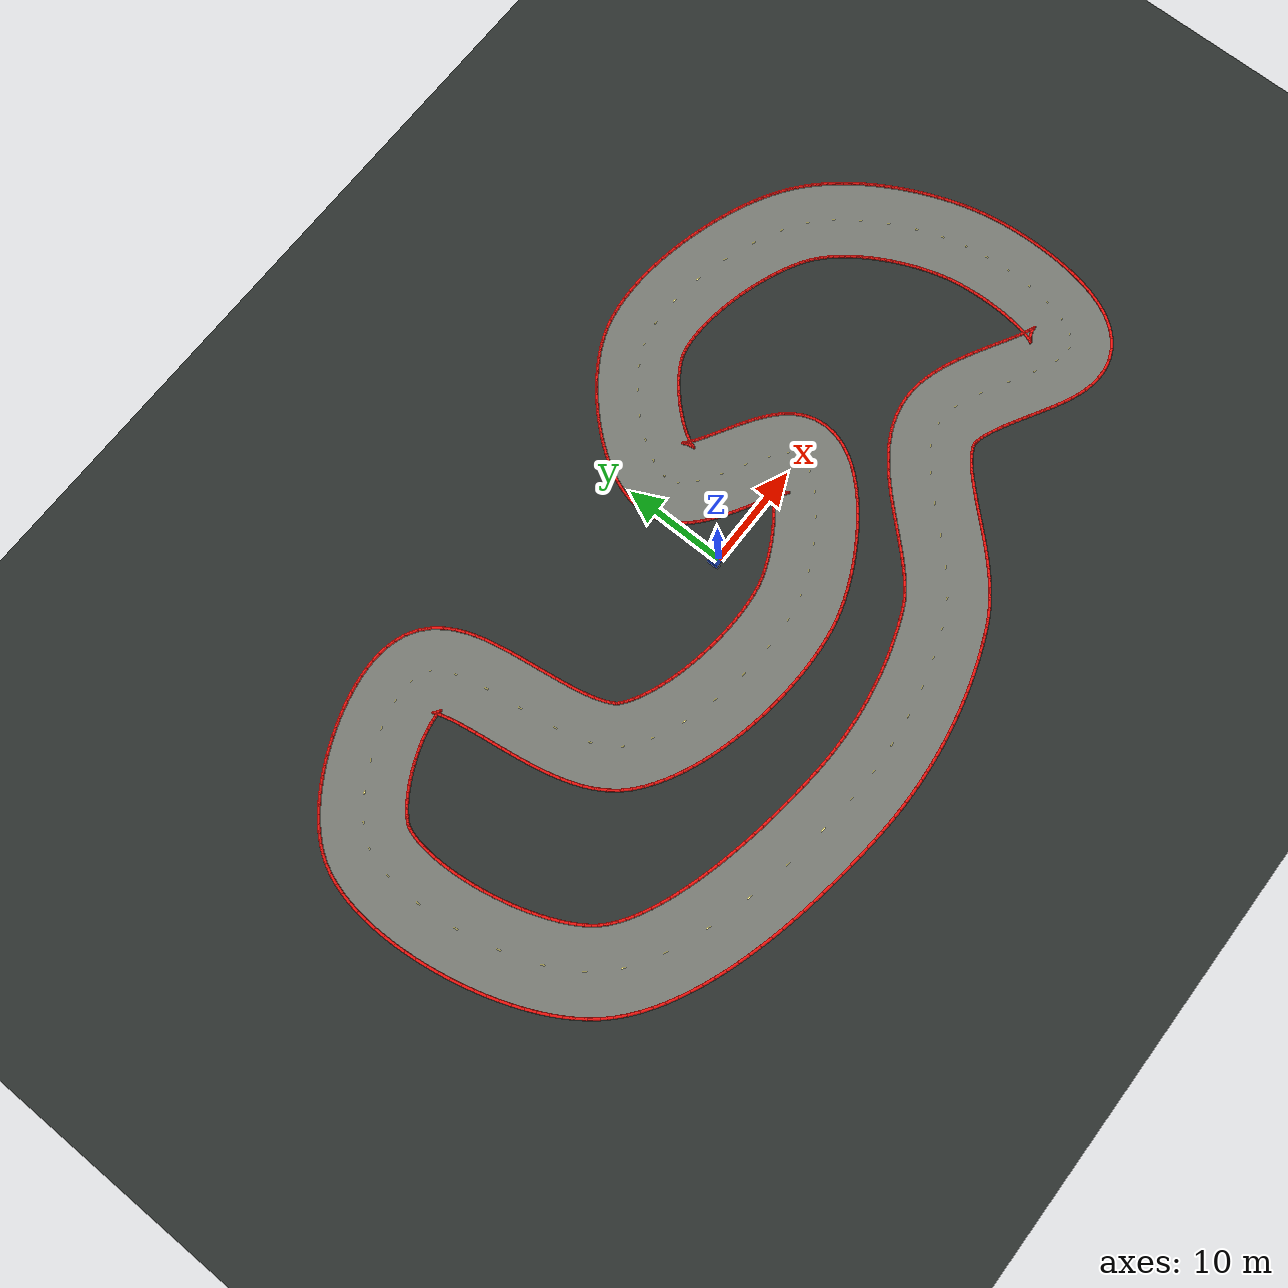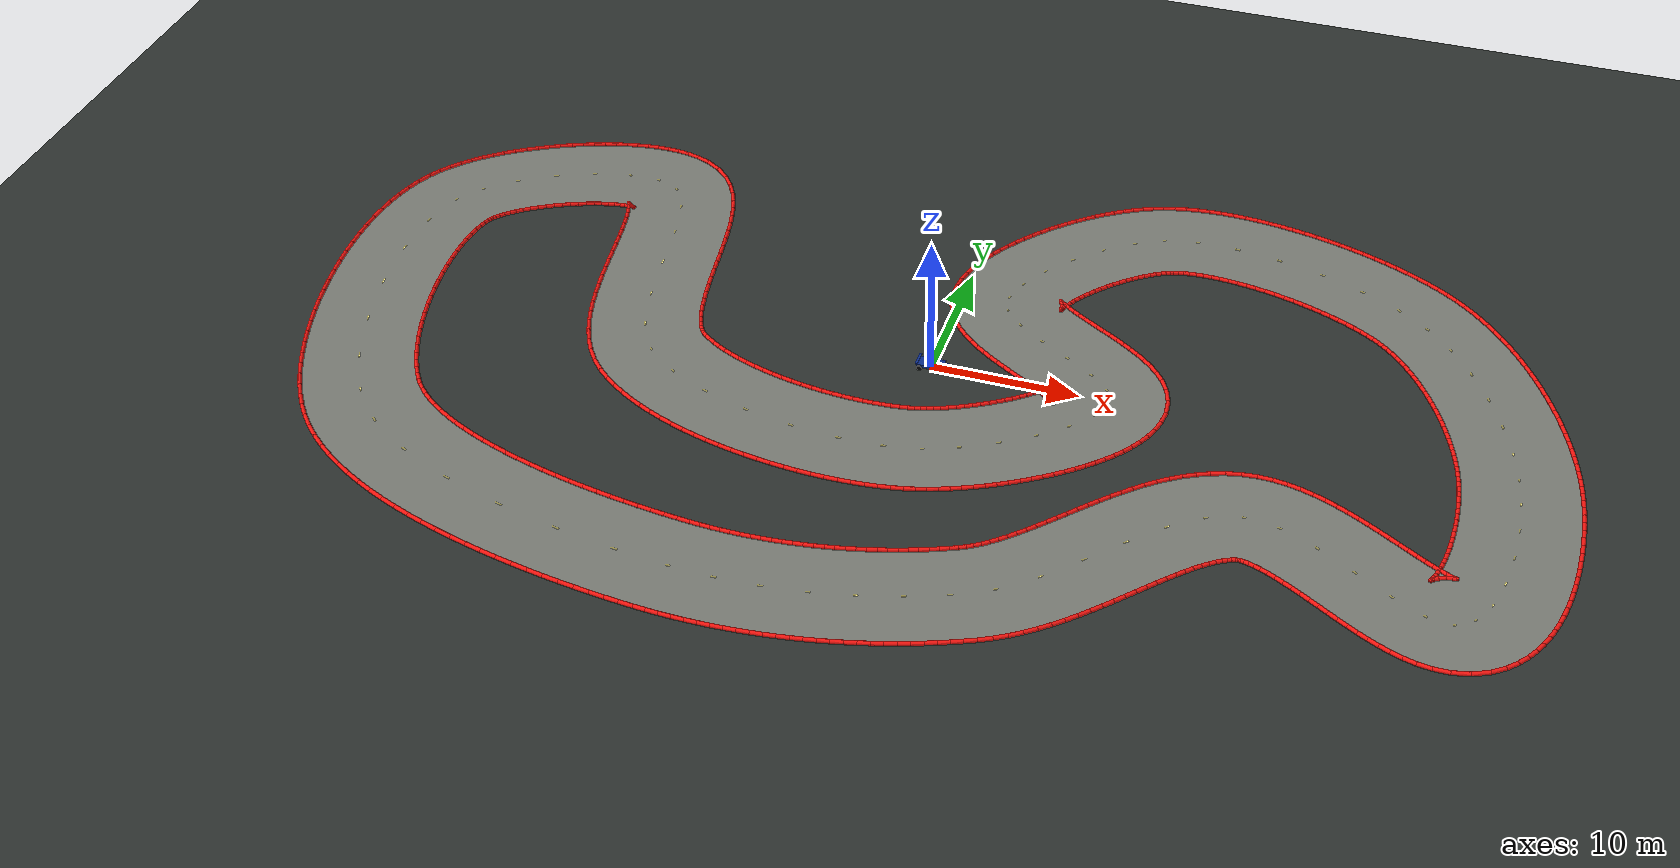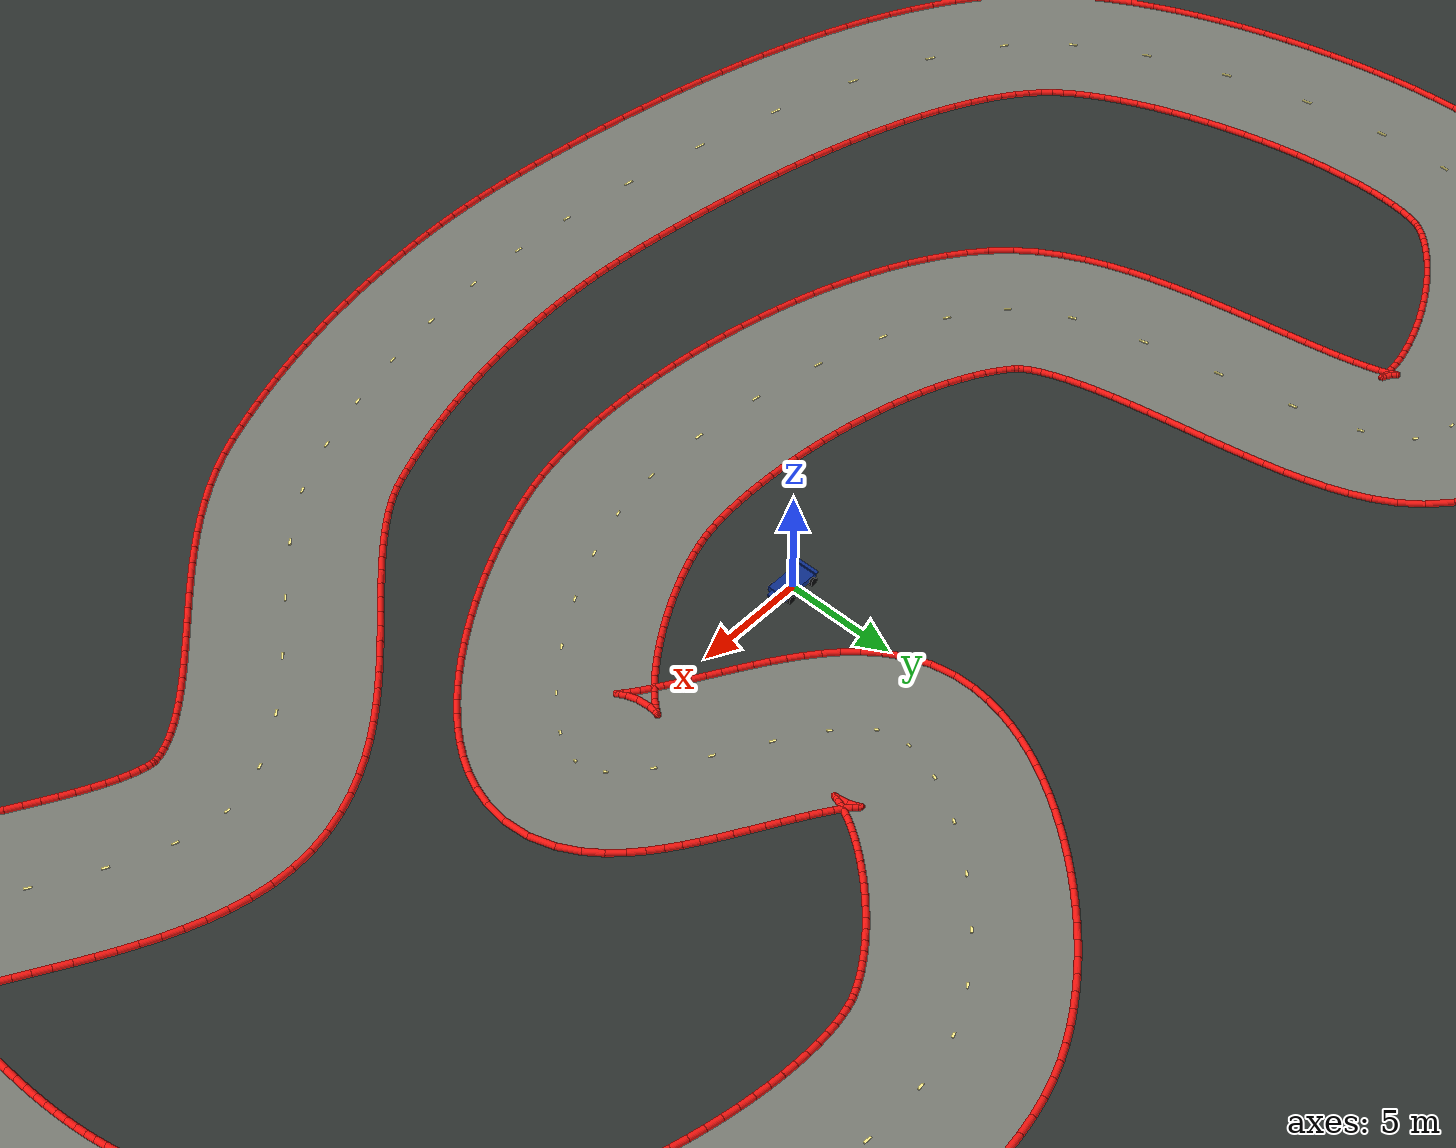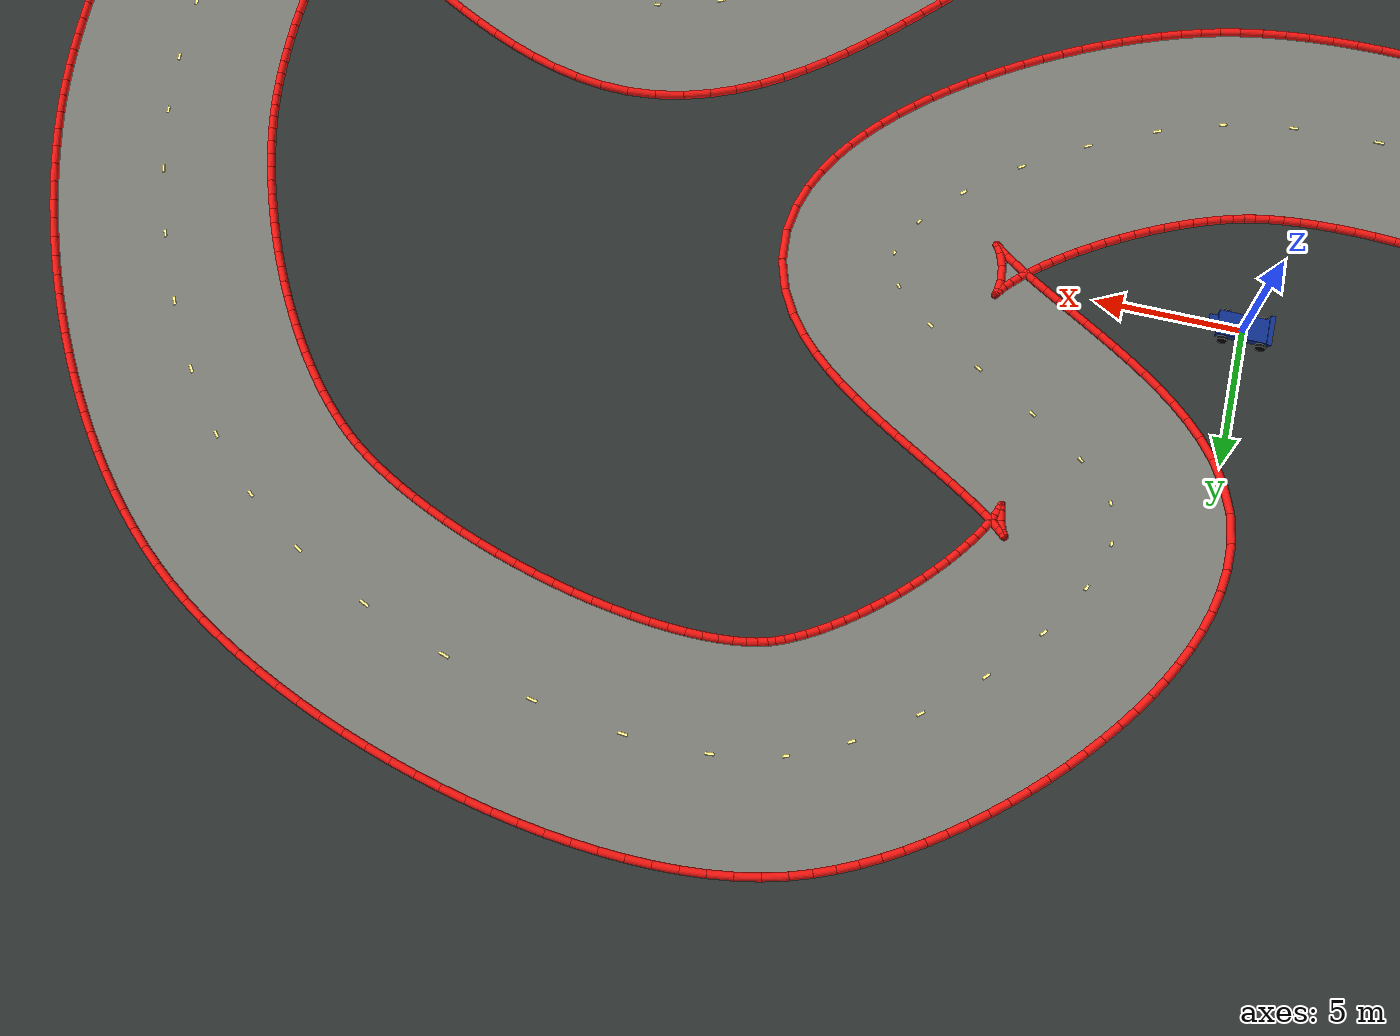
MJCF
<mujoco model="racesim_mini_monaco_world">
  <compiler angle="degree" autolimits="true"/>
  <option timestep="0.02" gravity="0 0 -9.81"/>
  <visual>
    <global offwidth="1280" offheight="960"/>
    <headlight ambient="0.35 0.35 0.35" diffuse="0.8 0.8 0.8"/>
  </visual>

  <include file="car.xml"/>
  <include file="mini_monaco_track.xml"/>

  <asset>
    <texture name="grid" type="2d" builtin="checker" width="512" height="512"
             rgb1="0.16 0.18 0.17" rgb2="0.20 0.22 0.21"/>
    <material name="ground" texture="grid" texrepeat="12 12" reflectance="0.05"/>
  </asset>

  <worldbody>
    <light name="sun" pos="0 0 30" dir="0 0 -1" diffuse="1.0 1.0 1.0" ambient="0.25 0.25 0.25"/>
    <geom name="ground" type="plane" size="90 90 0.1" material="ground"/>
    <camera name="topdown" pos="0 0 125" xyaxes="1 0 0 0 1 0" fovy="42"/>
    <camera name="follow" mode="trackcom" target="car" pos="-5 0 3" xyaxes="0 -1 0 0.5 0 0.866"/>
  </worldbody>
</mujoco>

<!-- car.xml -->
<mujoco model="simple_car">
  <default>
    <geom friction="1.2 0.02 0.001" density="600"/>
    <joint damping="0.1"/>
  </default>

  <asset>
    <material name="chassis_blue" rgba="0.05 0.18 0.55 1"/>
    <material name="wheel_dark" rgba="0.02 0.02 0.025 1"/>
  </asset>

  <worldbody>
    <body name="car" pos="0 0 0.28">
      <freejoint name="root"/>
      <geom name="chassis" type="box" size="0.9 0.45 0.12" material="chassis_blue"/>
      <geom name="nose" type="box" pos="0.75 0 0.02" size="0.45 0.25 0.06" material="chassis_blue"/>
      <geom name="rear_wing" type="box" pos="-0.85 0 0.22" size="0.08 0.55 0.04" material="chassis_blue"/>

      <body name="front_left_wheel" pos="0.65 0.48 -0.12">
        <joint name="front_left_spin" type="hinge" axis="0 1 0"/>
        <geom type="cylinder" size="0.18 0.08" euler="90 0 0" material="wheel_dark"/>
      </body>
      <body name="front_right_wheel" pos="0.65 -0.48 -0.12">
        <joint name="front_right_spin" type="hinge" axis="0 1 0"/>
        <geom type="cylinder" size="0.18 0.08" euler="90 0 0" material="wheel_dark"/>
      </body>
      <body name="rear_left_wheel" pos="-0.65 0.48 -0.12">
        <joint name="rear_left_spin" type="hinge" axis="0 1 0"/>
        <geom type="cylinder" size="0.18 0.08" euler="90 0 0" material="wheel_dark"/>
      </body>
      <body name="rear_right_wheel" pos="-0.65 -0.48 -0.12">
        <joint name="rear_right_spin" type="hinge" axis="0 1 0"/>
        <geom type="cylinder" size="0.18 0.08" euler="90 0 0" material="wheel_dark"/>
      </body>
    </body>
  </worldbody>
</mujoco>

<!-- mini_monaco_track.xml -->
<mujoco model="mini_monaco_track_visuals">
  <asset>
    <mesh name="track_surface_mesh" inertia="shell" vertex="34.31292 -0.68408 0.02200 34.22287 -0.23473 0.02200 34.11598 0.23113 0.02200 33.99214 0.71239 0.02200 33.85163 1.20644 0.02200 33.69482 1.71085 0.02200 33.52211 2.22325 0.02200 33.33397 2.74139 0.02200 33.13089 3.26307 0.02200 32.91341 3.78615 0.02200 32.68211 4.30853 0.02200 32.43761 4.82817 0.02200 32.18055 5.34303 0.02200 31.91163 5.85111 0.02200 31.63161 6.35043 0.02200 31.34128 6.83902 0.02200 31.04151 7.31495 0.02200 30.73323 7.77629 0.02200 30.41745 8.22116 0.02200 30.09528 8.64769 0.02200 29.76793 9.05409 0.02200 29.43670 9.43860 0.02200 29.10302 9.79959 0.02200 28.76845 10.13550 0.02200 28.43466 10.44498 0.02200 28.10344 10.72685 0.02200 27.77509 10.98135 0.02200 27.39185 11.24969 0.02200 26.96207 11.52319 0.02200 26.48792 11.79920 0.02200 25.97396 12.07406 0.02200 25.42467 12.34478 0.02200 24.84435 12.60881 0.02200 24.23724 12.86397 0.02200 23.60744 13.10838 0.02200 22.95901 13.34032 0.02200 22.29592 13.55827 0.02200 21.62215 13.76084 0.02200 20.94165 13.94676 0.02200 20.25839 14.11485 0.02200 19.57639 14.26402 0.02200 18.89974 14.39330 0.02200 18.23261 14.50183 0.02200 17.57932 14.58886 0.02200 16.94436 14.65382 0.02200 16.33242 14.69633 0.02200 15.74845 14.71632 0.02200 15.19771 14.71408 0.02200 14.68576 14.69044 0.02200 14.21856 14.64694 0.02200 13.80232 14.58613 0.02200 13.44340 14.51193 0.02200 13.13679 14.42646 0.02200 12.90621 14.34339 0.02200 12.63284 14.22584 0.02200 12.32636 14.07409 0.02200 11.99426 13.88927 0.02200 11.64306 13.67332 0.02200 11.27844 13.42861 0.02200 10.90545 13.15784 0.02200 10.52863 12.86389 0.02200 10.15211 12.54974 0.02200 9.77972 12.21853 0.02200 9.41507 11.87347 0.02200 9.06157 11.51791 0.02200 8.72253 11.15532 0.02200 8.40114 10.78939 0.02200 8.10049 10.42402 0.02200 7.82363 10.06348 0.02200 7.57351 9.71245 0.02200 7.35295 9.37619 0.02200 7.16456 9.06075 0.02200 7.01057 8.77322 0.02200 6.89252 8.52201 0.02200 6.81075 8.31720 0.02200 6.76345 8.17083 0.02200 6.74523 8.09673 0.02200 6.74495 8.10932 0.02200 6.73824 8.29680 0.02200 6.67054 8.66813 0.02200 6.55443 8.98380 0.02200 6.47133 9.13307 0.02200 6.46429 9.14718 0.02200 6.54666 9.06417 0.02200 6.71565 8.91455 0.02200 6.96217 8.71955 0.02200 7.27544 8.49323 0.02200 7.64494 8.24473 0.02200 8.06094 7.97993 0.02200 8.51465 7.70256 0.02200 8.99813 7.41486 0.02200 9.50424 7.11797 0.02200 10.02664 6.81214 0.02200 10.55969 6.49680 0.02200 11.09859 6.17041 0.02200 11.63948 5.83029 0.02200 12.17954 5.47205 0.02200 12.71724 5.08878 0.02200 13.25230 4.66957 0.02200 13.78524 4.19704 0.02200 14.31506 3.64371 0.02200 14.83243 2.96816 0.02200 15.30387 2.11713 0.02200 15.64898 1.05124 0.02200 15.74884 -0.09312 0.02200 15.62789 -1.08986 0.02200 15.39628 -1.90996 0.02200 15.09012 -2.63919 0.02200 14.73324 -3.29535 0.02200 14.33866 -3.89583 0.02200 13.91316 -4.45450 0.02200 13.46034 -4.98151 0.02200 12.98232 -5.48393 0.02200 12.48062 -5.96650 0.02200 11.95660 -6.43227 0.02200 11.41164 -6.88310 0.02200 10.84722 -7.31996 0.02200 10.26488 -7.74322 0.02200 9.66629 -8.15279 0.02200 9.05316 -8.54823 0.02200 8.42723 -8.92888 0.02200 7.79025 -9.29387 0.02200 7.14391 -9.64220 0.02200 6.48982 -9.97274 0.02200 5.82945 -10.28425 0.02200 5.16409 -10.57541 0.02200 4.49472 -10.84474 0.02200 3.82196 -11.09066 0.02200 3.14591 -11.31134 0.02200 2.46601 -11.50461 0.02200 1.78448 -11.66703 0.02200 0.99291 -11.81725 0.02200 0.18122 -11.93563 0.02200 -0.64796 -12.02424 0.02200 -1.49411 -12.08495 0.02200 -2.35621 -12.11904 0.02200 -3.23287 -12.12745 0.02200 -4.12240 -12.11080 0.02200 -5.02289 -12.06954 0.02200 -5.93223 -12.00397 0.02200 -6.84822 -11.91424 0.02200 -7.76855 -11.80040 0.02200 -8.69085 -11.66242 0.02200 -9.61273 -11.50015 0.02200 -10.53178 -11.31335 0.02200 -11.44559 -11.10166 0.02200 -12.35182 -10.86458 0.02200 -13.24813 -10.60144 0.02200 -14.13226 -10.31137 0.02200 -15.00199 -9.99326 0.02200 -15.85518 -9.64565 0.02200 -16.68970 -9.26670 0.02200 -17.50342 -8.85406 0.02200 -18.29407 -8.40477 0.02200 -19.05912 -7.91513 0.02200 -19.79552 -7.38059 0.02200 -20.54587 -6.75337 0.02200 -21.30124 -5.97264 0.02200 -21.96983 -5.08298 0.02200 -22.51598 -4.16316 0.02200 -22.96333 -3.22732 0.02200 -23.33247 -2.28221 0.02200 -23.63987 -1.33112 0.02200 -23.89832 -0.37631 0.02200 -24.11788 0.57979 0.02200 -24.30663 1.53413 0.02200 -24.47126 2.48284 0.02200 -24.61753 3.42125 0.02200 -24.75051 4.34390 0.02200 -24.87471 5.24454 0.02200 -24.99424 6.11617 0.02200 -25.11273 6.95097 0.02200 -25.23325 7.74014 0.02200 -25.35816 8.47376 0.02200 -25.48868 9.14046 0.02200 -25.62422 9.72711 0.02200 -25.76120 10.21848 0.02200 -25.89108 10.59721 0.02200 -25.99728 10.84509 0.02200 -26.05148 10.94764 0.02200 -26.01274 10.90579 0.02200 -25.83988 10.75508 0.02200 -25.61209 10.61420 0.02200 -25.48200 10.55698 0.02200 -25.52088 10.56390 0.02200 -25.65914 10.58026 0.02200 -25.88501 10.58890 0.02200 -26.18519 10.57923 0.02200 -26.54703 10.54526 0.02200 -26.95918 10.48397 0.02200 -27.41166 10.39427 0.02200 -27.89561 10.27624 0.02200 -28.40312 10.13075 0.02200 -28.92697 9.95915 0.02200 -29.46048 9.76318 0.02200 -29.99736 9.54480 0.02200 -30.53157 9.30627 0.02200 -31.05729 9.05002 0.02200 -31.56879 8.77877 0.02200 -32.06039 8.49553 0.02200 -32.52645 8.20370 0.02200 -32.96130 7.90718 0.02200 -33.35926 7.61051 0.02200 -33.71469 7.31912 0.02200 -34.02214 7.03962 0.02200 -34.27656 6.78012 0.02200 -34.47392 6.55064 0.02200 -34.61212 6.36341 0.02200 -34.69290 6.23206 0.02200 -34.80138 5.99915 0.02200 -34.91668 5.67400 0.02200 -35.03081 5.24974 0.02200 -35.13244 4.73752 0.02200 -35.21423 4.14860 0.02200 -35.27156 3.49356 0.02200 -35.30167 2.78216 0.02200 -35.30300 2.02339 0.02200 -35.27481 1.22556 0.02200 -35.21695 0.39644 0.02200 -35.12963 -0.45659 0.02200 -35.01336 -1.32648 0.02200 -34.86886 -2.20640 0.02200 -34.69705 -3.08969 0.02200 -34.49901 -3.96976 0.02200 -34.27599 -4.84011 0.02200 -34.02944 -5.69421 0.02200 -33.76102 -6.52552 0.02200 -33.47267 -7.32740 0.02200 -33.16667 -8.09312 0.02200 -32.84577 -8.81582 0.02200 -32.51336 -9.48850 0.02200 -32.17361 -10.10407 0.02200 -31.83181 -10.65542 0.02200 -31.49469 -11.13570 0.02200 -31.17228 -11.53697 0.02200 -30.80354 -11.92878 0.02200 -30.37578 -12.31940 0.02200 -29.88109 -12.71381 0.02200 -29.32155 -13.10759 0.02200 -28.70049 -13.49675 0.02200 -28.02197 -13.87797 0.02200 -27.29059 -14.24856 0.02200 -26.51116 -14.60642 0.02200 -25.68861 -14.94996 0.02200 -24.82791 -15.27800 0.02200 -23.93398 -15.58971 0.02200 -23.01169 -15.88454 0.02200 -22.06585 -16.16215 0.02200 -21.10118 -16.42239 0.02200 -20.12235 -16.66524 0.02200 -19.13395 -16.89079 0.02200 -18.14052 -17.09922 0.02200 -17.14657 -17.29079 0.02200 -16.15655 -17.46580 0.02200 -15.17487 -17.62462 0.02200 -14.20595 -17.76764 0.02200 -13.25417 -17.89528 0.02200 -12.32392 -18.00800 0.02200 -11.41960 -18.10628 0.02200 -10.54565 -18.19061 0.02200 -9.71371 -18.26094 0.02200 -9.04554 -18.30688 0.02200 -8.38523 -18.33933 0.02200 -7.72595 -18.35897 0.02200 -7.06796 -18.36591 0.02200 -6.41156 -18.36028 0.02200 -5.75702 -18.34218 0.02200 -5.10465 -18.31175 0.02200 -4.45473 -18.26910 0.02200 -3.80755 -18.21436 0.02200 -3.16341 -18.14767 0.02200 -2.52260 -18.06915 0.02200 -1.88543 -17.97893 0.02200 -1.25218 -17.87716 0.02200 -0.62316 -17.76396 0.02200 0.00134 -17.63949 0.02200 0.62101 -17.50388 0.02200 1.23555 -17.35728 0.02200 1.84466 -17.19984 0.02200 2.44804 -17.03172 0.02200 3.04539 -16.85307 0.02200 3.63641 -16.66405 0.02200 4.22079 -16.46482 0.02200 4.79825 -16.25555 0.02200 5.36848 -16.03640 0.02200 5.93118 -15.80756 0.02200 6.44074 -15.58954 0.02200 6.85465 -15.38987 0.02200 7.24137 -15.16845 0.02200 7.64884 -14.90227 0.02200 8.07454 -14.59212 0.02200 8.51590 -14.24001 0.02200 8.97055 -13.84887 0.02200 9.43658 -13.42223 0.02200 9.91253 -12.96403 0.02200 10.39744 -12.47843 0.02200 10.89083 -11.96967 0.02200 11.39266 -11.44202 0.02200 11.90333 -10.89972 0.02200 12.42367 -10.34691 0.02200 12.95493 -9.78765 0.02200 13.49886 -9.22593 0.02200 14.05772 -8.66567 0.02200 14.63435 -8.11081 0.02200 15.23230 -7.56536 0.02200 15.85586 -7.03366 0.02200 16.51017 -6.52058 0.02200 17.20112 -6.03198 0.02200 17.93519 -5.57520 0.02200 18.71876 -5.15978 0.02200 19.55704 -4.79800 0.02200 20.45233 -4.50500 0.02200 21.42260 -4.29472 0.02200 22.40610 -4.20249 0.02200 23.37782 -4.22900 0.02200 24.29655 -4.35099 0.02200 25.16519 -4.54479 0.02200 25.99031 -4.79264 0.02200 26.77888 -5.08146 0.02200 27.53683 -5.40132 0.02200 28.26855 -5.74428 0.02200 28.97690 -6.10347 0.02200 29.66345 -6.47263 0.02200 30.32859 -6.84575 0.02200 30.97173 -7.21691 0.02200 31.59137 -7.58012 0.02200 32.18512 -7.92926 0.02200 32.74965 -8.25808 0.02200 33.28047 -8.56011 0.02200 33.77165 -8.82875 0.02200 34.21528 -9.05740 0.02200 34.60066 -9.23974 0.02200 34.91309 -9.37059 0.02200 35.13242 -9.44769 0.02200 35.23184 -9.47552 0.02200 35.17961 -9.47243 0.02200 34.95040 -9.48015 0.02200 34.55481 -9.56459 0.02200 34.14889 -9.73873 0.02200 33.89686 -9.90595 0.02200 33.79259 -10.00122 0.02200 33.76136 -10.03588 0.02200 33.78383 -9.99954 0.02200 33.84204 -9.89118 0.02200 33.92172 -9.71489 0.02200 34.01237 -9.47695 0.02200 34.10660 -9.18428 0.02200 34.19924 -8.84368 0.02200 34.28677 -8.46156 0.02200 34.36680 -8.04385 0.02200 34.43772 -7.59602 0.02200 34.49847 -7.12319 0.02200 34.54839 -6.63013 0.02200 34.58711 -6.12137 0.02200 34.61446 -5.60126 0.02200 34.63041 -5.07398 0.02200 34.63508 -4.54363 0.02200 34.62868 -4.01425 0.02200 34.61151 -3.48988 0.02200 34.58398 -2.97456 0.02200 34.54657 -2.47244 0.02200 34.49990 -1.98778 0.02200 34.44472 -1.52504 0.02200 34.38202 -1.08900 0.02200 41.68708 0.68408 0.02200 41.55559 1.34047 0.02200 41.40343 2.00400 0.02200 41.23147 2.67253 0.02200 41.04015 3.34541 0.02200 40.82989 4.02186 0.02200 40.60101 4.70098 0.02200 40.35382 5.38180 0.02200 40.08854 6.06325 0.02200 39.80541 6.74424 0.02200 39.50459 7.42362 0.02200 39.18623 8.10019 0.02200 38.85040 8.77276 0.02200 38.49718 9.44006 0.02200 38.12656 10.10085 0.02200 37.73848 10.75384 0.02200 37.33285 11.39772 0.02200 36.90946 12.03118 0.02200 36.46807 12.65287 0.02200 36.00831 13.26138 0.02200 35.52974 13.85529 0.02200 35.03179 14.43310 0.02200 34.51377 14.99321 0.02200 33.97490 15.53392 0.02200 33.41424 16.05334 0.02200 32.83077 16.54942 0.02200 32.22491 17.01865 0.02200 31.55921 17.48531 0.02200 30.86455 17.92793 0.02200 30.14484 18.34724 0.02200 29.40159 18.74500 0.02200 28.63644 19.12228 0.02200 27.85112 19.47971 0.02200 27.04751 19.81756 0.02200 26.22756 20.13582 0.02200 25.39332 20.43427 0.02200 24.54687 20.71252 0.02200 23.69034 20.97005 0.02200 22.82585 21.20622 0.02200 21.95550 21.42031 0.02200 21.08136 21.61147 0.02200 20.20542 21.77877 0.02200 19.32959 21.92117 0.02200 18.45563 22.03749 0.02200 17.58513 22.12640 0.02200 16.71949 22.18634 0.02200 15.85982 22.21550 0.02200 15.00697 22.21166 0.02200 14.16143 22.17209 0.02200 13.32334 22.09332 0.02200 12.49256 21.97088 0.02200 11.66883 21.79897 0.02200 10.86321 21.57354 0.02200 10.16554 21.32470 0.02200 9.49363 21.03726 0.02200 8.84227 20.71571 0.02200 8.20846 20.36366 0.02200 7.59018 19.98396 0.02200 6.98623 19.57897 0.02200 6.39606 19.15079 0.02200 5.81962 18.70128 0.02200 5.25726 18.23221 0.02200 4.70964 17.74522 0.02200 4.17766 17.24185 0.02200 3.66237 16.72353 0.02200 3.16497 16.19153 0.02200 2.68676 15.64695 0.02200 2.22912 15.09061 0.02200 1.79351 14.52303 0.02200 1.38147 13.94429 0.02200 0.99466 13.35388 0.02200 0.63496 12.75052 0.02200 0.30464 12.13188 0.02200 0.00664 11.49432 0.02200 -0.25489 10.83251 0.02200 -0.47365 10.13917 0.02200 -0.63974 9.40525 0.02200 -0.73757 8.62107 0.02200 -0.73824 7.70320 0.02200 -0.55710 6.66533 0.02200 -0.18351 5.68984 0.02200 0.28892 4.88715 0.02200 0.80490 4.22567 0.02200 1.33887 3.66704 0.02200 1.88140 3.18044 0.02200 2.42937 2.74429 0.02200 2.98132 2.34421 0.02200 3.53558 1.97073 0.02200 4.08964 1.61764 0.02200 4.64010 1.28089 0.02200 5.18265 0.95791 0.02200 5.71222 0.64722 0.02200 6.22296 0.34824 0.02200 6.70825 0.06124 0.02200 7.16070 -0.21261 0.02200 7.57195 -0.47092 0.02200 7.93258 -0.70964 0.02200 8.23194 -0.92221 0.02200 8.45806 -1.09803 0.02200 8.59821 -1.22004 0.02200 8.64119 -1.26110 0.02200 8.58408 -1.18012 0.02200 8.44817 -0.92415 0.02200 8.30162 -0.45417 0.02200 8.25116 0.09312 0.02200 8.28587 0.44136 0.02200 8.32477 0.58878 0.02200 8.33747 0.62450 0.02200 8.30584 0.56969 0.02200 8.22257 0.44508 0.02200 8.08658 0.26789 0.02200 7.90000 0.05164 0.02200 7.66641 -0.19326 0.02200 7.39000 -0.45872 0.02200 7.07511 -0.73833 0.02200 6.72607 -1.02687 0.02200 6.34713 -1.32003 0.02200 5.94243 -1.61408 0.02200 5.51603 -1.90576 0.02200 5.07193 -2.19215 0.02200 4.61408 -2.47056 0.02200 4.14647 -2.73850 0.02200 3.67309 -2.99364 0.02200 3.19804 -3.23373 0.02200 2.72557 -3.45667 0.02200 2.26011 -3.66043 0.02200 1.80637 -3.84312 0.02200 1.36945 -4.00298 0.02200 0.95495 -4.13849 0.02200 0.56914 -4.24845 0.02200 0.21552 -4.33297 0.02200 -0.24618 -4.42031 0.02200 -0.75734 -4.49458 0.02200 -1.31400 -4.55387 0.02200 -1.91006 -4.59649 0.02200 -2.53990 -4.62129 0.02200 -3.19831 -4.62753 0.02200 -3.88037 -4.61471 0.02200 -4.58136 -4.58255 0.02200 -5.29677 -4.53094 0.02200 -6.02219 -4.45986 0.02200 -6.75333 -4.36943 0.02200 -7.48592 -4.25984 0.02200 -8.21575 -4.13140 0.02200 -8.93860 -3.98452 0.02200 -9.65026 -3.81971 0.02200 -10.34648 -3.63764 0.02200 -11.02296 -3.43914 0.02200 -11.67534 -3.22522 0.02200 -12.29924 -2.99718 0.02200 -12.89017 -2.75662 0.02200 -13.44366 -2.50555 0.02200 -13.95521 -2.24647 0.02200 -14.42048 -1.98252 0.02200 -14.83536 -1.71756 0.02200 -15.19633 -1.45628 0.02200 -15.45413 -1.24663 0.02200 -15.59777 -1.10228 0.02200 -15.73074 -0.92080 0.02200 -15.89654 -0.63711 0.02200 -16.07931 -0.25071 0.02200 -16.26626 0.23149 0.02200 -16.44875 0.79911 0.02200 -16.62177 1.44077 0.02200 -16.78307 2.14521 0.02200 -16.93239 2.90183 0.02200 -17.07083 3.70085 0.02200 -17.20043 4.53326 0.02200 -17.32395 5.39089 0.02200 -17.44464 6.26631 0.02200 -17.56623 7.15284 0.02200 -17.69290 8.04467 0.02200 -17.82935 8.93693 0.02200 -17.98105 9.82589 0.02200 -18.15459 10.70924 0.02200 -18.35835 11.58645 0.02200 -18.60371 12.45910 0.02200 -18.90702 13.33089 0.02200 -19.29267 14.20636 0.02200 -19.79678 15.08633 0.02200 -20.46810 15.95623 0.02200 -21.35560 16.76683 0.02200 -22.38791 17.38580 0.02200 -23.32733 17.74080 0.02200 -24.18417 17.94382 0.02200 -25.01991 18.05297 0.02200 -25.83819 18.08875 0.02200 -26.64419 18.06518 0.02200 -27.44243 17.99162 0.02200 -28.23612 17.87447 0.02200 -29.02715 17.71821 0.02200 -29.81624 17.52615 0.02200 -30.60318 17.30081 0.02200 -31.38706 17.04421 0.02200 -32.16644 16.75802 0.02200 -32.93949 16.44364 0.02200 -33.70412 16.10222 0.02200 -34.45803 15.73470 0.02200 -35.19883 15.34175 0.02200 -35.92406 14.92375 0.02200 -36.63126 14.48069 0.02200 -37.31796 14.01205 0.02200 -37.98173 13.51667 0.02200 -38.62006 12.99252 0.02200 -39.23031 12.43637 0.02200 -39.80939 11.84349 0.02200 -40.35320 11.20726 0.02200 -40.85573 10.51882 0.02200 -41.30710 9.76794 0.02200 -41.73328 8.86251 0.02200 -42.07166 7.92260 0.02200 -42.33194 6.96539 0.02200 -42.52712 5.99002 0.02200 -42.66626 4.99554 0.02200 -42.75566 3.98165 0.02200 -42.79982 2.94890 0.02200 -42.80196 1.89861 0.02200 -42.76452 0.83277 0.02200 -42.68938 -0.24611 0.02200 -42.57800 -1.33509 0.02200 -42.43159 -2.43093 0.02200 -42.25111 -3.53015 0.02200 -42.03735 -4.62913 0.02200 -41.79093 -5.72413 0.02200 -41.51229 -6.81139 0.02200 -41.20170 -7.88710 0.02200 -40.85918 -8.94754 0.02200 -40.48450 -9.98901 0.02200 -40.07707 -11.00796 0.02200 -39.63583 -12.00095 0.02200 -39.15912 -12.96468 0.02200 -38.64445 -13.89594 0.02200 -38.08822 -14.79153 0.02200 -37.48543 -15.64802 0.02200 -36.82772 -16.46303 0.02200 -36.06979 -17.26888 0.02200 -35.24945 -18.02004 0.02200 -34.38259 -18.71269 0.02200 -33.47510 -19.35243 0.02200 -32.53166 -19.94439 0.02200 -31.55617 -20.49306 0.02200 -30.55205 -21.00229 0.02200 -29.52244 -21.47535 0.02200 -28.47040 -21.91499 0.02200 -27.39896 -22.32354 0.02200 -26.31117 -22.70300 0.02200 -25.21015 -23.05509 0.02200 -24.09909 -23.38129 0.02200 -22.98122 -23.68293 0.02200 -21.85989 -23.96120 0.02200 -20.73847 -24.21715 0.02200 -19.62041 -24.45177 0.02200 -18.50919 -24.66597 0.02200 -17.40835 -24.86060 0.02200 -16.32144 -25.03646 0.02200 -15.25206 -25.19432 0.02200 -14.20378 -25.33492 0.02200 -13.18022 -25.45896 0.02200 -12.18495 -25.56713 0.02200 -11.22153 -25.66009 0.02200 -10.28629 -25.73906 0.02200 -9.48652 -25.79390 0.02200 -8.68102 -25.83350 0.02200 -7.87719 -25.85745 0.02200 -7.07533 -25.86591 0.02200 -6.27571 -25.85905 0.02200 -5.47863 -25.83701 0.02200 -4.68434 -25.79996 0.02200 -3.89314 -25.74804 0.02200 -3.10530 -25.68141 0.02200 -2.32108 -25.60022 0.02200 -1.54076 -25.50460 0.02200 -0.76461 -25.39471 0.02200 0.00710 -25.27068 0.02200 0.77410 -25.13266 0.02200 1.53613 -24.98077 0.02200 2.29292 -24.81515 0.02200 3.04420 -24.63593 0.02200 3.78970 -24.44324 0.02200 4.52917 -24.23720 0.02200 5.26234 -24.01792 0.02200 5.98893 -23.78554 0.02200 6.70868 -23.54016 0.02200 7.42133 -23.28189 0.02200 8.12660 -23.01084 0.02200 8.82423 -22.72711 0.02200 9.55926 -22.41046 0.02200 10.35389 -22.02352 0.02200 11.15115 -21.56873 0.02200 11.90486 -21.07773 0.02200 12.61928 -20.55831 0.02200 13.29875 -20.01707 0.02200 13.94737 -19.45969 0.02200 14.56884 -18.89123 0.02200 15.16634 -18.31636 0.02200 15.74260 -17.73954 0.02200 16.29985 -17.16510 0.02200 16.83988 -16.59739 0.02200 17.36405 -16.04078 0.02200 17.87329 -15.49973 0.02200 18.36809 -14.97877 0.02200 18.84846 -14.48253 0.02200 19.31390 -14.01568 0.02200 19.76331 -13.58289 0.02200 20.19490 -13.18875 0.02200 20.60614 -12.83753 0.02200 20.99363 -12.53295 0.02200 21.35324 -12.27777 0.02200 21.68026 -12.07324 0.02200 21.97004 -11.91842 0.02200 22.21913 -11.80965 0.02200 22.42699 -11.74038 0.02200 22.57740 -11.70528 0.02200 22.64723 -11.69861 0.02200 22.76730 -11.70411 0.02200 22.97424 -11.73350 0.02200 23.26059 -11.79893 0.02200 23.61519 -11.90663 0.02200 24.02651 -12.05817 0.02200 24.48406 -12.25191 0.02200 24.97888 -12.48431 0.02200 25.50351 -12.75069 0.02200 26.05183 -13.04577 0.02200 26.61888 -13.36404 0.02200 27.20068 -13.69990 0.02200 27.79415 -14.04781 0.02200 28.39711 -14.40236 0.02200 29.00833 -14.75827 0.02200 29.62772 -15.11048 0.02200 30.25663 -15.45406 0.02200 30.89842 -15.78409 0.02200 31.55920 -16.09536 0.02200 32.24911 -16.38152 0.02200 32.98373 -16.63331 0.02200 33.78529 -16.83470 0.02200 34.68097 -16.95583 0.02200 35.69153 -16.94344 0.02200 36.80178 -16.72009 0.02200 37.85111 -16.26127 0.02200 38.65444 -15.70383 0.02200 39.27256 -15.12176 0.02200 39.78090 -14.50971 0.02200 40.19950 -13.88403 0.02200 40.54702 -13.25172 0.02200 40.83846 -12.61466 0.02200 41.08500 -11.97256 0.02200 41.29476 -11.32445 0.02200 41.47360 -10.66951 0.02200 41.62575 -10.00732 0.02200 41.75431 -9.33791 0.02200 41.86161 -8.66178 0.02200 41.94939 -7.97979 0.02200 42.01903 -7.29314 0.02200 42.07162 -6.60328 0.02200 42.10802 -5.91183 0.02200 42.12897 -5.22059 0.02200 42.13507 -4.53142 0.02200 42.12679 -3.84625 0.02200 42.10456 -3.16704 0.02200 42.06867 -2.49570 0.02200 42.01935 -1.83407 0.02200 41.95669 -1.18386 0.02200 41.88062 -0.54657 0.02200 41.79089 0.07660 0.02200" face="0 365 1 0 364 365 1 366 2 1 365 366 2 367 3 2 366 367 3 368 4 3 367 368 4 369 5 4 368 369 5 370 6 5 369 370 6 371 7 6 370 371 7 372 8 7 371 372 8 373 9 8 372 373 9 374 10 9 373 374 10 375 11 10 374 375 11 376 12 11 375 376 12 377 13 12 376 377 13 378 14 13 377 378 14 379 15 14 378 379 15 380 16 15 379 380 16 381 17 16 380 381 17 382 18 17 381 382 18 383 19 18 382 383 19 384 20 19 383 384 20 385 21 20 384 385 21 386 22 21 385 386 22 387 23 22 386 387 23 388 24 23 387 388 24 389 25 24 388 389 25 390 26 25 389 390 26 391 27 26 390 391 27 392 28 27 391 392 28 393 29 28 392 393 29 394 30 29 393 394 30 395 31 30 394 395 31 396 32 31 395 396 32 397 33 32 396 397 33 398 34 33 397 398 34 399 35 34 398 399 35 400 36 35 399 400 36 401 37 36 400 401 37 402 38 37 401 402 38 403 39 38 402 403 39 404 40 39 403 404 40 405 41 40 404 405 41 406 42 41 405 406 42 407 43 42 406 407 43 408 44 43 407 408 44 409 45 44 408 409 45 410 46 45 409 410 46 411 47 46 410 411 47 412 48 47 411 412 48 413 49 48 412 413 49 414 50 49 413 414 50 415 51 50 414 415 51 416 52 51 415 416 52 417 53 52 416 417 53 418 54 53 417 418 54 419 55 54 418 419 55 420 56 55 419 420 56 421 57 56 420 421 57 422 58 57 421 422 58 423 59 58 422 423 59 424 60 59 423 424 60 425 61 60 424 425 61 426 62 61 425 426 62 427 63 62 426 427 63 428 64 63 427 428 64 429 65 64 428 429 65 430 66 65 429 430 66 431 67 66 430 431 67 432 68 67 431 432 68 433 69 68 432 433 69 434 70 69 433 434 70 435 71 70 434 435 71 436 72 71 435 436 72 437 73 72 436 437 73 438 74 73 437 438 74 439 75 74 438 439 75 440 76 75 439 440 76 441 77 76 440 441 77 442 78 77 441 442 78 443 79 78 442 443 79 444 80 79 443 444 80 445 81 80 444 445 81 446 82 81 445 446 82 447 83 82 446 447 83 448 84 83 447 448 84 449 85 84 448 449 85 450 86 85 449 450 86 451 87 86 450 451 87 452 88 87 451 452 88 453 89 88 452 453 89 454 90 89 453 454 90 455 91 90 454 455 91 456 92 91 455 456 92 457 93 92 456 457 93 458 94 93 457 458 94 459 95 94 458 459 95 460 96 95 459 460 96 461 97 96 460 461 97 462 98 97 461 462 98 463 99 98 462 463 99 464 100 99 463 464 100 465 101 100 464 465 101 466 102 101 465 466 102 467 103 102 466 467 103 468 104 103 467 468 104 469 105 104 468 469 105 470 106 105 469 470 106 471 107 106 470 471 107 472 108 107 471 472 108 473 109 108 472 473 109 474 110 109 473 474 110 475 111 110 474 475 111 476 112 111 475 476 112 477 113 112 476 477 113 478 114 113 477 478 114 479 115 114 478 479 115 480 116 115 479 480 116 481 117 116 480 481 117 482 118 117 481 482 118 483 119 118 482 483 119 484 120 119 483 484 120 485 121 120 484 485 121 486 122 121 485 486 122 487 123 122 486 487 123 488 124 123 487 488 124 489 125 124 488 489 125 490 126 125 489 490 126 491 127 126 490 491 127 492 128 127 491 492 128 493 129 128 492 493 129 494 130 129 493 494 130 495 131 130 494 495 131 496 132 131 495 496 132 497 133 132 496 497 133 498 134 133 497 498 134 499 135 134 498 499 135 500 136 135 499 500 136 501 137 136 500 501 137 502 138 137 501 502 138 503 139 138 502 503 139 504 140 139 503 504 140 505 141 140 504 505 141 506 142 141 505 506 142 507 143 142 506 507 143 508 144 143 507 508 144 509 145 144 508 509 145 510 146 145 509 510 146 511 147 146 510 511 147 512 148 147 511 512 148 513 149 148 512 513 149 514 150 149 513 514 150 515 151 150 514 515 151 516 152 151 515 516 152 517 153 152 516 517 153 518 154 153 517 518 154 519 155 154 518 519 155 520 156 155 519 520 156 521 157 156 520 521 157 522 158 157 521 522 158 523 159 158 522 523 159 524 160 159 523 524 160 525 161 160 524 525 161 526 162 161 525 526 162 527 163 162 526 527 163 528 164 163 527 528 164 529 165 164 528 529 165 530 166 165 529 530 166 531 167 166 530 531 167 532 168 167 531 532 168 533 169 168 532 533 169 534 170 169 533 534 170 535 171 170 534 535 171 536 172 171 535 536 172 537 173 172 536 537 173 538 174 173 537 538 174 539 175 174 538 539 175 540 176 175 539 540 176 541 177 176 540 541 177 542 178 177 541 542 178 543 179 178 542 543 179 544 180 179 543 544 180 545 181 180 544 545 181 546 182 181 545 546 182 547 183 182 546 547 183 548 184 183 547 548 184 549 185 184 548 549 185 550 186 185 549 550 186 551 187 186 550 551 187 552 188 187 551 552 188 553 189 188 552 553 189 554 190 189 553 554 190 555 191 190 554 555 191 556 192 191 555 556 192 557 193 192 556 557 193 558 194 193 557 558 194 559 195 194 558 559 195 560 196 195 559 560 196 561 197 196 560 561 197 562 198 197 561 562 198 563 199 198 562 563 199 564 200 199 563 564 200 565 201 200 564 565 201 566 202 201 565 566 202 567 203 202 566 567 203 568 204 203 567 568 204 569 205 204 568 569 205 570 206 205 569 570 206 571 207 206 570 571 207 572 208 207 571 572 208 573 209 208 572 573 209 574 210 209 573 574 210 575 211 210 574 575 211 576 212 211 575 576 212 577 213 212 576 577 213 578 214 213 577 578 214 579 215 214 578 579 215 580 216 215 579 580 216 581 217 216 580 581 217 582 218 217 581 582 218 583 219 218 582 583 219 584 220 219 583 584 220 585 221 220 584 585 221 586 222 221 585 586 222 587 223 222 586 587 223 588 224 223 587 588 224 589 225 224 588 589 225 590 226 225 589 590 226 591 227 226 590 591 227 592 228 227 591 592 228 593 229 228 592 593 229 594 230 229 593 594 230 595 231 230 594 595 231 596 232 231 595 596 232 597 233 232 596 597 233 598 234 233 597 598 234 599 235 234 598 599 235 600 236 235 599 600 236 601 237 236 600 601 237 602 238 237 601 602 238 603 239 238 602 603 239 604 240 239 603 604 240 605 241 240 604 605 241 606 242 241 605 606 242 607 243 242 606 607 243 608 244 243 607 608 244 609 245 244 608 609 245 610 246 245 609 610 246 611 247 246 610 611 247 612 248 247 611 612 248 613 249 248 612 613 249 614 250 249 613 614 250 615 251 250 614 615 251 616 252 251 615 616 252 617 253 252 616 617 253 618 254 253 617 618 254 619 255 254 618 619 255 620 256 255 619 620 256 621 257 256 620 621 257 622 258 257 621 622 258 623 259 258 622 623 259 624 260 259 623 624 260 625 261 260 624 625 261 626 262 261 625 626 262 627 263 262 626 627 263 628 264 263 627 628 264 629 265 264 628 629 265 630 266 265 629 630 266 631 267 266 630 631 267 632 268 267 631 632 268 633 269 268 632 633 269 634 270 269 633 634 270 635 271 270 634 635 271 636 272 271 635 636 272 637 273 272 636 637 273 638 274 273 637 638 274 639 275 274 638 639 275 640 276 275 639 640 276 641 277 276 640 641 277 642 278 277 641 642 278 643 279 278 642 643 279 644 280 279 643 644 280 645 281 280 644 645 281 646 282 281 645 646 282 647 283 282 646 647 283 648 284 283 647 648 284 649 285 284 648 649 285 650 286 285 649 650 286 651 287 286 650 651 287 652 288 287 651 652 288 653 289 288 652 653 289 654 290 289 653 654 290 655 291 290 654 655 291 656 292 291 655 656 292 657 293 292 656 657 293 658 294 293 657 658 294 659 295 294 658 659 295 660 296 295 659 660 296 661 297 296 660 661 297 662 298 297 661 662 298 663 299 298 662 663 299 664 300 299 663 664 300 665 301 300 664 665 301 666 302 301 665 666 302 667 303 302 666 667 303 668 304 303 667 668 304 669 305 304 668 669 305 670 306 305 669 670 306 671 307 306 670 671 307 672 308 307 671 672 308 673 309 308 672 673 309 674 310 309 673 674 310 675 311 310 674 675 311 676 312 311 675 676 312 677 313 312 676 677 313 678 314 313 677 678 314 679 315 314 678 679 315 680 316 315 679 680 316 681 317 316 680 681 317 682 318 317 681 682 318 683 319 318 682 683 319 684 320 319 683 684 320 685 321 320 684 685 321 686 322 321 685 686 322 687 323 322 686 687 323 688 324 323 687 688 324 689 325 324 688 689 325 690 326 325 689 690 326 691 327 326 690 691 327 692 328 327 691 692 328 693 329 328 692 693 329 694 330 329 693 694 330 695 331 330 694 695 331 696 332 331 695 696 332 697 333 332 696 697 333 698 334 333 697 698 334 699 335 334 698 699 335 700 336 335 699 700 336 701 337 336 700 701 337 702 338 337 701 702 338 703 339 338 702 703 339 704 340 339 703 704 340 705 341 340 704 705 341 706 342 341 705 706 342 707 343 342 706 707 343 708 344 343 707 708 344 709 345 344 708 709 345 710 346 345 709 710 346 711 347 346 710 711 347 712 348 347 711 712 348 713 349 348 712 713 349 714 350 349 713 714 350 715 351 350 714 715 351 716 352 351 715 716 352 717 353 352 716 717 353 718 354 353 717 718 354 719 355 354 718 719 355 720 356 355 719 720 356 721 357 356 720 721 357 722 358 357 721 722 358 723 359 358 722 723 359 724 360 359 723 724 360 725 361 360 724 725 361 726 362 361 725 726 362 727 363 362 726 727 363 364 0 363 727 364"/>
    <material name="track_asphalt" rgba="0.48 0.49 0.46 1" emission="0.08"/>
    <material name="track_boundary" rgba="0.95 0.08 0.06 1" emission="0.05"/>
    <material name="track_centerline" rgba="1.0 0.95 0.55 1" emission="0.15"/>
  </asset>
  <worldbody>
    <geom name="track_surface" type="mesh" mesh="track_surface_mesh" material="track_asphalt" contype="0" conaffinity="0"/>
    <geom name="track_left_boundary_000" type="capsule" fromto="34.31292 -0.68408 0.09 34.22287 -0.23473 0.09" size="0.14" material="track_boundary" contype="0" conaffinity="0"/>
    <geom name="track_left_boundary_001" type="capsule" fromto="34.22287 -0.23473 0.09 34.11598 0.23113 0.09" size="0.14" material="track_boundary" contype="0" conaffinity="0"/>
    <geom name="track_left_boundary_002" type="capsule" fromto="34.11598 0.23113 0.09 33.99214 0.71239 0.09" size="0.14" material="track_boundary" contype="0" conaffinity="0"/>
    <geom name="track_left_boundary_003" type="capsule" fromto="33.99214 0.71239 0.09 33.85163 1.20644 0.09" size="0.14" material="track_boundary" contype="0" conaffinity="0"/>
    <geom name="track_left_boundary_004" type="capsule" fromto="33.85163 1.20644 0.09 33.69482 1.71085 0.09" size="0.14" material="track_boundary" contype="0" conaffinity="0"/>
    <geom name="track_left_boundary_005" type="capsule" fromto="33.69482 1.71085 0.09 33.52211 2.22325 0.09" size="0.14" material="track_boundary" contype="0" conaffinity="0"/>
    <geom name="track_left_boundary_006" type="capsule" fromto="33.52211 2.22325 0.09 33.33397 2.74139 0.09" size="0.14" material="track_boundary" contype="0" conaffinity="0"/>
    <geom name="track_left_boundary_007" type="capsule" fromto="33.33397 2.74139 0.09 33.13089 3.26307 0.09" size="0.14" material="track_boundary" contype="0" conaffinity="0"/>
    <geom name="track_left_boundary_008" type="capsule" fromto="33.13089 3.26307 0.09 32.91341 3.78615 0.09" size="0.14" material="track_boundary" contype="0" conaffinity="0"/>
    <geom name="track_left_boundary_009" type="capsule" fromto="32.91341 3.78615 0.09 32.68211 4.30853 0.09" size="0.14" material="track_boundary" contype="0" conaffinity="0"/>
    <geom name="track_left_boundary_010" type="capsule" fromto="32.68211 4.30853 0.09 32.43761 4.82817 0.09" size="0.14" material="track_boundary" contype="0" conaffinity="0"/>
    <geom name="track_left_boundary_011" type="capsule" fromto="32.43761 4.82817 0.09 32.18055 5.34303 0.09" size="0.14" material="track_boundary" contype="0" conaffinity="0"/>
    <geom name="track_left_boundary_012" type="capsule" fromto="32.18055 5.34303 0.09 31.91163 5.85111 0.09" size="0.14" material="track_boundary" contype="0" conaffinity="0"/>
    <geom name="track_left_boundary_013" type="capsule" fromto="31.91163 5.85111 0.09 31.63161 6.35043 0.09" size="0.14" material="track_boundary" contype="0" conaffinity="0"/>
    <geom name="track_left_boundary_014" type="capsule" fromto="31.63161 6.35043 0.09 31.34128 6.83902 0.09" size="0.14" material="track_boundary" contype="0" conaffinity="0"/>
    <geom name="track_left_boundary_015" type="capsule" fromto="31.34128 6.83902 0.09 31.04151 7.31495 0.09" size="0.14" material="track_boundary" contype="0" conaffinity="0"/>
    <geom name="track_left_boundary_016" type="capsule" fromto="31.04151 7.31495 0.09 30.73323 7.77629 0.09" size="0.14" material="track_boundary" contype="0" conaffinity="0"/>
    <geom name="track_left_boundary_017" type="capsule" fromto="30.73323 7.77629 0.09 30.41745 8.22116 0.09" size="0.14" material="track_boundary" contype="0" conaffinity="0"/>
    <geom name="track_left_boundary_018" type="capsule" fromto="30.41745 8.22116 0.09 30.09528 8.64769 0.09" size="0.14" material="track_boundary" contype="0" conaffinity="0"/>
    <geom name="track_left_boundary_019" type="capsule" fromto="30.09528 8.64769 0.09 29.76793 9.05409 0.09" size="0.14" material="track_boundary" contype="0" conaffinity="0"/>
    <geom name="track_left_boundary_020" type="capsule" fromto="29.76793 9.05409 0.09 29.43670 9.43860 0.09" size="0.14" material="track_boundary" contype="0" conaffinity="0"/>
    <geom name="track_left_boundary_021" type="capsule" fromto="29.43670 9.43860 0.09 29.10302 9.79959 0.09" size="0.14" material="track_boundary" contype="0" conaffinity="0"/>
    <geom name="track_left_boundary_022" type="capsule" fromto="29.10302 9.79959 0.09 28.76845 10.13550 0.09" size="0.14" material="track_boundary" contype="0" conaffinity="0"/>
    <geom name="track_left_boundary_023" type="capsule" fromto="28.76845 10.13550 0.09 28.43466 10.44498 0.09" size="0.14" material="track_boundary" contype="0" conaffinity="0"/>
    <geom name="track_left_boundary_024" type="capsule" fromto="28.43466 10.44498 0.09 28.10344 10.72685 0.09" size="0.14" material="track_boundary" contype="0" conaffinity="0"/>
    <geom name="track_left_boundary_025" type="capsule" fromto="28.10344 10.72685 0.09 27.77509 10.98135 0.09" size="0.14" material="track_boundary" contype="0" conaffinity="0"/>
    <geom name="track_left_boundary_026" type="capsule" fromto="27.77509 10.98135 0.09 27.39185 11.24969 0.09" size="0.14" material="track_boundary" contype="0" conaffinity="0"/>
    <geom name="track_left_boundary_027" type="capsule" fromto="27.39185 11.24969 0.09 26.96207 11.52319 0.09" size="0.14" material="track_boundary" contype="0" conaffinity="0"/>
    <geom name="track_left_boundary_028" type="capsule" fromto="26.96207 11.52319 0.09 26.48792 11.79920 0.09" size="0.14" material="track_boundary" contype="0" conaffinity="0"/>
    <geom name="track_left_boundary_029" type="capsule" fromto="26.48792 11.79920 0.09 25.97396 12.07406 0.09" size="0.14" material="track_boundary" contype="0" conaffinity="0"/>
    <geom name="track_left_boundary_030" type="capsule" fromto="25.97396 12.07406 0.09 25.42467 12.34478 0.09" size="0.14" material="track_boundary" contype="0" conaffinity="0"/>
    <geom name="track_left_boundary_031" type="capsule" fromto="25.42467 12.34478 0.09 24.84435 12.60881 0.09" size="0.14" material="track_boundary" contype="0" conaffinity="0"/>
    <geom name="track_left_boundary_032" type="capsule" fromto="24.84435 12.60881 0.09 24.23724 12.86397 0.09" size="0.14" material="track_boundary" contype="0" conaffinity="0"/>
    <geom name="track_left_boundary_033" type="capsule" fromto="24.23724 12.86397 0.09 23.60744 13.10838 0.09" size="0.14" material="track_boundary" contype="0" conaffinity="0"/>
    <geom name="track_left_boundary_034" type="capsule" fromto="23.60744 13.10838 0.09 22.95901 13.34032 0.09" size="0.14" material="track_boundary" contype="0" conaffinity="0"/>
    <geom name="track_left_boundary_035" type="capsule" fromto="22.95901 13.34032 0.09 22.29592 13.55827 0.09" size="0.14" material="track_boundary" contype="0" conaffinity="0"/>
    <geom name="track_left_boundary_036" type="capsule" fromto="22.29592 13.55827 0.09 21.62215 13.76084 0.09" size="0.14" material="track_boundary" contype="0" conaffinity="0"/>
    <geom name="track_left_boundary_037" type="capsule" fromto="21.62215 13.76084 0.09 20.94165 13.94676 0.09" size="0.14" material="track_boundary" contype="0" conaffinity="0"/>
    <geom name="track_left_boundary_038" type="capsule" fromto="20.94165 13.94676 0.09 20.25839 14.11485 0.09" size="0.14" material="track_boundary" contype="0" conaffinity="0"/>
    <geom name="track_left_boundary_039" type="capsule" fromto="20.25839 14.11485 0.09 19.57639 14.26402 0.09" size="0.14" material="track_boundary" contype="0" conaffinity="0"/>
    <geom name="track_left_boundary_040" type="capsule" fromto="19.57639 14.26402 0.09 18.89974 14.39330 0.09" size="0.14" material="track_boundary" contype="0" conaffinity="0"/>
    <geom name="track_left_boundary_041" type="capsule" fromto="18.89974 14.39330 0.09 18.23261 14.50183 0.09" size="0.14" material="track_boundary" contype="0" conaffinity="0"/>
    <geom name="track_left_boundary_042" type="capsule" fromto="18.23261 14.50183 0.09 17.57932 14.58886 0.09" size="0.14" material="track_boundary" contype="0" conaffinity="0"/>
    <geom name="track_left_boundary_043" type="capsule" fromto="17.57932 14.58886 0.09 16.94436 14.65382 0.09" size="0.14" material="track_boundary" contype="0" conaffinity="0"/>
    <geom name="track_left_boundary_044" type="capsule" fromto="16.94436 14.65382 0.09 16.33242 14.69633 0.09" size="0.14" material="track_boundary" contype="0" conaffinity="0"/>
    <geom name="track_left_boundary_045" type="capsule" fromto="16.33242 14.69633 0.09 15.74845 14.71632 0.09" size="0.14" material="track_boundary" contype="0" conaffinity="0"/>
    <geom name="track_left_boundary_046" type="capsule" fromto="15.74845 14.71632 0.09 15.19771 14.71408 0.09" size="0.14" material="track_boundary" contype="0" conaffinity="0"/>
    <geom name="track_left_boundary_047" type="capsule" fromto="15.19771 14.71408 0.09 14.68576 14.69044 0.09" size="0.14" material="track_boundary" contype="0" conaffinity="0"/>
    <geom name="track_left_boundary_048" type="capsule" fromto="14.68576 14.69044 0.09 14.21856 14.64694 0.09" size="0.14" material="track_boundary" contype="0" conaffinity="0"/>
    <geom name="track_left_boundary_049" type="capsule" fromto="14.21856 14.64694 0.09 13.80232 14.58613 0.09" size="0.14" material="track_boundary" contype="0" conaffinity="0"/>
    <geom name="track_left_boundary_050" type="capsule" fromto="13.80232 14.58613 0.09 13.44340 14.51193 0.09" size="0.14" material="track_boundary" contype="0" conaffinity="0"/>
    <geom name="track_left_boundary_051" type="capsule" fromto="13.44340 14.51193 0.09 13.13679 14.42646 0.09" size="0.14" material="track_boundary" contype="0" conaffinity="0"/>
    <geom name="track_left_boundary_052" type="capsule" fromto="13.13679 14.42646 0.09 12.90621 14.34339 0.09" size="0.14" material="track_boundary" contype="0" conaffinity="0"/>
    <geom name="track_left_boundary_053" type="capsule" fromto="12.90621 14.34339 0.09 12.63284 14.22584 0.09" size="0.14" material="track_boundary" contype="0" conaffinity="0"/>
    <geom name="track_left_boundary_054" type="capsule" fromto="12.63284 14.22584 0.09 12.32636 14.07409 0.09" size="0.14" material="track_boundary" contype="0" conaffinity="0"/>
    <geom name="track_left_boundary_055" type="capsule" fromto="12.32636 14.07409 0.09 11.99426 13.88927 0.09" size="0.14" material="track_boundary" contype="0" conaffinity="0"/>
    <geom name="track_left_boundary_056" type="capsule" fromto="11.99426 13.88927 0.09 11.64306 13.67332 0.09" size="0.14" material="track_boundary" contype="0" conaffinity="0"/>
    <geom name="track_left_boundary_057" type="capsule" fromto="11.64306 13.67332 0.09 11.27844 13.42861 0.09" size="0.14" material="track_boundary" contype="0" conaffinity="0"/>
    <geom name="track_left_boundary_058" type="capsule" fromto="11.27844 13.42861 0.09 10.90545 13.15784 0.09" size="0.14" material="track_boundary" contype="0" conaffinity="0"/>
    <geom name="track_left_boundary_059" type="capsule" fromto="10.90545 13.15784 0.09 10.52863 12.86389 0.09" size="0.14" material="track_boundary" contype="0" conaffinity="0"/>
    <geom name="track_left_boundary_060" type="capsule" fromto="10.52863 12.86389 0.09 10.15211 12.54974 0.09" size="0.14" material="track_boundary" contype="0" conaffinity="0"/>
    <geom name="track_left_boundary_061" type="capsule" fromto="10.15211 12.54974 0.09 9.77972 12.21853 0.09" size="0.14" material="track_boundary" contype="0" conaffinity="0"/>
    <geom name="track_left_boundary_062" type="capsule" fromto="9.77972 12.21853 0.09 9.41507 11.87347 0.09" size="0.14" material="track_boundary" contype="0" conaffinity="0"/>
    <geom name="track_left_boundary_063" type="capsule" fromto="9.41507 11.87347 0.09 9.06157 11.51791 0.09" size="0.14" material="track_boundary" contype="0" conaffinity="0"/>
    <geom name="track_left_boundary_064" type="capsule" fromto="9.06157 11.51791 0.09 8.72253 11.15532 0.09" size="0.14" material="track_boundary" contype="0" conaffinity="0"/>
    <geom name="track_left_boundary_065" type="capsule" fromto="8.72253 11.15532 0.09 8.40114 10.78939 0.09" size="0.14" material="track_boundary" contype="0" conaffinity="0"/>
    <geom name="track_left_boundary_066" type="capsule" fromto="8.40114 10.78939 0.09 8.10049 10.42402 0.09" size="0.14" material="track_boundary" contype="0" conaffinity="0"/>
    <geom name="track_left_boundary_067" type="capsule" fromto="8.10049 10.42402 0.09 7.82363 10.06348 0.09" size="0.14" material="track_boundary" contype="0" conaffinity="0"/>
    <geom name="track_left_boundary_068" type="capsule" fromto="7.82363 10.06348 0.09 7.57351 9.71245 0.09" size="0.14" material="track_boundary" contype="0" conaffinity="0"/>
    <geom name="track_left_boundary_069" type="capsule" fromto="7.57351 9.71245 0.09 7.35295 9.37619 0.09" size="0.14" material="track_boundary" contype="0" conaffinity="0"/>
    <geom name="track_left_boundary_070" type="capsule" fromto="7.35295 9.37619 0.09 7.16456 9.06075 0.09" size="0.14" material="track_boundary" contype="0" conaffinity="0"/>
    <geom name="track_left_boundary_071" type="capsule" fromto="7.16456 9.06075 0.09 7.01057 8.77322 0.09" size="0.14" material="track_boundary" contype="0" conaffinity="0"/>
    <geom name="track_left_boundary_072" type="capsule" fromto="7.01057 8.77322 0.09 6.89252 8.52201 0.09" size="0.14" material="track_boundary" contype="0" conaffinity="0"/>
    <geom name="track_left_boundary_073" type="capsule" fromto="6.89252 8.52201 0.09 6.81075 8.31720 0.09" size="0.14" material="track_boundary" contype="0" conaffinity="0"/>
    <geom name="track_left_boundary_074" type="capsule" fromto="6.81075 8.31720 0.09 6.76345 8.17083 0.09" size="0.14" material="track_boundary" contype="0" conaffinity="0"/>
    <geom name="track_left_boundary_075" type="capsule" fromto="6.76345 8.17083 0.09 6.74523 8.09673 0.09" size="0.14" material="track_boundary" contype="0" conaffinity="0"/>
    <geom name="track_left_boundary_076" type="capsule" fromto="6.74523 8.09673 0.09 6.74495 8.10932 0.09" size="0.14" material="track_boundary" contype="0" conaffinity="0"/>
    <geom name="track_left_boundary_077" type="capsule" fromto="6.74495 8.10932 0.09 6.73824 8.29680 0.09" size="0.14" material="track_boundary" contype="0" conaffinity="0"/>
    <geom name="track_left_boundary_078" type="capsule" fromto="6.73824 8.29680 0.09 6.67054 8.66813 0.09" size="0.14" material="track_boundary" contype="0" conaffinity="0"/>
    <geom name="track_left_boundary_079" type="capsule" fromto="6.67054 8.66813 0.09 6.55443 8.98380 0.09" size="0.14" material="track_boundary" contype="0" conaffinity="0"/>
    <geom name="track_left_boundary_080" type="capsule" fromto="6.55443 8.98380 0.09 6.47133 9.13307 0.09" size="0.14" material="track_boundary" contype="0" conaffinity="0"/>
    <geom name="track_left_boundary_081" type="capsule" fromto="6.47133 9.13307 0.09 6.46429 9.14718 0.09" size="0.14" material="track_boundary" contype="0" conaffinity="0"/>
    <geom name="track_left_boundary_082" type="capsule" fromto="6.46429 9.14718 0.09 6.54666 9.06417 0.09" size="0.14" material="track_boundary" contype="0" conaffinity="0"/>
    <geom name="track_left_boundary_083" type="capsule" fromto="6.54666 9.06417 0.09 6.71565 8.91455 0.09" size="0.14" material="track_boundary" contype="0" conaffinity="0"/>
    <geom name="track_left_boundary_084" type="capsule" fromto="6.71565 8.91455 0.09 6.96217 8.71955 0.09" size="0.14" material="track_boundary" contype="0" conaffinity="0"/>
    <geom name="track_left_boundary_085" type="capsule" fromto="6.96217 8.71955 0.09 7.27544 8.49323 0.09" size="0.14" material="track_boundary" contype="0" conaffinity="0"/>
    <geom name="track_left_boundary_086" type="capsule" fromto="7.27544 8.49323 0.09 7.64494 8.24473 0.09" size="0.14" material="track_boundary" contype="0" conaffinity="0"/>
    <geom name="track_left_boundary_087" type="capsule" fromto="7.64494 8.24473 0.09 8.06094 7.97993 0.09" size="0.14" material="track_boundary" contype="0" conaffinity="0"/>
    <geom name="track_left_boundary_088" type="capsule" fromto="8.06094 7.97993 0.09 8.51465 7.70256 0.09" size="0.14" material="track_boundary" contype="0" conaffinity="0"/>
    <geom name="track_left_boundary_089" type="capsule" fromto="8.51465 7.70256 0.09 8.99813 7.41486 0.09" size="0.14" material="track_boundary" contype="0" conaffinity="0"/>
    <geom name="track_left_boundary_090" type="capsule" fromto="8.99813 7.41486 0.09 9.50424 7.11797 0.09" size="0.14" material="track_boundary" contype="0" conaffinity="0"/>
    <geom name="track_left_boundary_091" type="capsule" fromto="9.50424 7.11797 0.09 10.02664 6.81214 0.09" size="0.14" material="track_boundary" contype="0" conaffinity="0"/>
    <geom name="track_left_boundary_092" type="capsule" fromto="10.02664 6.81214 0.09 10.55969 6.49680 0.09" size="0.14" material="track_boundary" contype="0" conaffinity="0"/>
    <geom name="track_left_boundary_093" type="capsule" fromto="10.55969 6.49680 0.09 11.09859 6.17041 0.09" size="0.14" material="track_boundary" contype="0" conaffinity="0"/>
    <geom name="track_left_boundary_094" type="capsule" fromto="11.09859 6.17041 0.09 11.63948 5.83029 0.09" size="0.14" material="track_boundary" contype="0" conaffinity="0"/>
    <geom name="track_left_boundary_095" type="capsule" fromto="11.63948 5.83029 0.09 12.17954 5.47205 0.09" size="0.14" material="track_boundary" contype="0" conaffinity="0"/>
    <geom name="track_left_boundary_096" type="capsule" fromto="12.17954 5.47205 0.09 12.71724 5.08878 0.09" size="0.14" material="track_boundary" contype="0" conaffinity="0"/>
    <geom name="track_left_boundary_097" type="capsule" fromto="12.71724 5.08878 0.09 13.25230 4.66957 0.09" size="0.14" material="track_boundary" contype="0" conaffinity="0"/>
    <geom name="track_left_boundary_098" type="capsule" fromto="13.25230 4.66957 0.09 13.78524 4.19704 0.09" size="0.14" material="track_boundary" contype="0" conaffinity="0"/>
    <geom name="track_left_boundary_099" type="capsule" fromto="13.78524 4.19704 0.09 14.31506 3.64371 0.09" size="0.14" material="track_boundary" contype="0" conaffinity="0"/>
    <geom name="track_left_boundary_100" type="capsule" fromto="14.31506 3.64371 0.09 14.83243 2.96816 0.09" size="0.14" material="track_boundary" contype="0" conaffinity="0"/>
    <geom name="track_left_boundary_101" type="capsule" fromto="14.83243 2.96816 0.09 15.30387 2.11713 0.09" size="0.14" material="track_boundary" contype="0" conaffinity="0"/>
    <geom name="track_left_boundary_102" type="capsule" fromto="15.30387 2.11713 0.09 15.64898 1.05124 0.09" size="0.14" material="track_boundary" contype="0" conaffinity="0"/>
    <geom name="track_left_boundary_103" type="capsule" fromto="15.64898 1.05124 0.09 15.74884 -0.09312 0.09" size="0.14" material="track_boundary" contype="0" conaffinity="0"/>
    <geom name="track_left_boundary_104" type="capsule" fromto="15.74884 -0.09312 0.09 15.62789 -1.08986 0.09" size="0.14" material="track_boundary" contype="0" conaffinity="0"/>
    <geom name="track_left_boundary_105" type="capsule" fromto="15.62789 -1.08986 0.09 15.39628 -1.90996 0.09" size="0.14" material="track_boundary" contype="0" conaffinity="0"/>
    <geom name="track_left_boundary_106" type="capsule" fromto="15.39628 -1.90996 0.09 15.09012 -2.63919 0.09" size="0.14" material="track_boundary" contype="0" conaffinity="0"/>
    <geom name="track_left_boundary_107" type="capsule" fromto="15.09012 -2.63919 0.09 14.73324 -3.29535 0.09" size="0.14" material="track_boundary" contype="0" conaffinity="0"/>
    <geom name="track_left_boundary_108" type="capsule" fromto="14.73324 -3.29535 0.09 14.33866 -3.89583 0.09" size="0.14" material="track_boundary" contype="0" conaffinity="0"/>
    <geom name="track_left_boundary_109" type="capsule" fromto="14.33866 -3.89583 0.09 13.91316 -4.45450 0.09" size="0.14" material="track_boundary" contype="0" conaffinity="0"/>
    <geom name="track_left_boundary_110" type="capsule" fromto="13.91316 -4.45450 0.09 13.46034 -4.98151 0.09" size="0.14" material="track_boundary" contype="0" conaffinity="0"/>
    <geom name="track_left_boundary_111" type="capsule" fromto="13.46034 -4.98151 0.09 12.98232 -5.48393 0.09" size="0.14" material="track_boundary" contype="0" conaffinity="0"/>
    <geom name="track_left_boundary_112" type="capsule" fromto="12.98232 -5.48393 0.09 12.48062 -5.96650 0.09" size="0.14" material="track_boundary" contype="0" conaffinity="0"/>
    <geom name="track_left_boundary_113" type="capsule" fromto="12.48062 -5.96650 0.09 11.95660 -6.43227 0.09" size="0.14" material="track_boundary" contype="0" conaffinity="0"/>
    <geom name="track_left_boundary_114" type="capsule" fromto="11.95660 -6.43227 0.09 11.41164 -6.88310 0.09" size="0.14" material="track_boundary" contype="0" conaffinity="0"/>
    <geom name="track_left_boundary_115" type="capsule" fromto="11.41164 -6.88310 0.09 10.84722 -7.31996 0.09" size="0.14" material="track_boundary" contype="0" conaffinity="0"/>
    <geom name="track_left_boundary_116" type="capsule" fromto="10.84722 -7.31996 0.09 10.26488 -7.74322 0.09" size="0.14" material="track_boundary" contype="0" conaffinity="0"/>
    <geom name="track_left_boundary_117" type="capsule" fromto="10.26488 -7.74322 0.09 9.66629 -8.15279 0.09" size="0.14" material="track_boundary" contype="0" conaffinity="0"/>
    <geom name="track_left_boundary_118" type="capsule" fromto="9.66629 -8.15279 0.09 9.05316 -8.54823 0.09" size="0.14" material="track_boundary" contype="0" conaffinity="0"/>
    <geom name="track_left_boundary_119" type="capsule" fromto="9.05316 -8.54823 0.09 8.42723 -8.92888 0.09" size="0.14" material="track_boundary" contype="0" conaffinity="0"/>
    <geom name="track_left_boundary_120" type="capsule" fromto="8.42723 -8.92888 0.09 7.79025 -9.29387 0.09" size="0.14" material="track_boundary" contype="0" conaffinity="0"/>
    <geom name="track_left_boundary_121" type="capsule" fromto="7.79025 -9.29387 0.09 7.14391 -9.64220 0.09" size="0.14" material="track_boundary" contype="0" conaffinity="0"/>
    <geom name="track_left_boundary_122" type="capsule" fromto="7.14391 -9.64220 0.09 6.48982 -9.97274 0.09" size="0.14" material="track_boundary" contype="0" conaffinity="0"/>
    <geom name="track_left_boundary_123" type="capsule" fromto="6.48982 -9.97274 0.09 5.82945 -10.28425 0.09" size="0.14" material="track_boundary" contype="0" conaffinity="0"/>
    <geom name="track_left_boundary_124" type="capsule" fromto="5.82945 -10.28425 0.09 5.16409 -10.57541 0.09" size="0.14" material="track_boundary" contype="0" conaffinity="0"/>
    <geom name="track_left_boundary_125" type="capsule" fromto="5.16409 -10.57541 0.09 4.49472 -10.84474 0.09" size="0.14" material="track_boundary" contype="0" conaffinity="0"/>
    <geom name="track_left_boundary_126" type="capsule" fromto="4.49472 -10.84474 0.09 3.82196 -11.09066 0.09" size="0.14" material="track_boundary" contype="0" conaffinity="0"/>
    <geom name="track_left_boundary_127" type="capsule" fromto="3.82196 -11.09066 0.09 3.14591 -11.31134 0.09" size="0.14" material="track_boundary" contype="0" conaffinity="0"/>
    <geom name="track_left_boundary_128" type="capsule" fromto="3.14591 -11.31134 0.09 2.46601 -11.50461 0.09" size="0.14" material="track_boundary" contype="0" conaffinity="0"/>
    <geom name="track_left_boundary_129" type="capsule" fromto="2.46601 -11.50461 0.09 1.78448 -11.66703 0.09" size="0.14" material="track_boundary" contype="0" conaffinity="0"/>
    <geom name="track_left_boundary_130" type="capsule" fromto="1.78448 -11.66703 0.09 0.99291 -11.81725 0.09" size="0.14" material="track_boundary" contype="0" conaffinity="0"/>
    <geom name="track_left_boundary_131" type="capsule" fromto="0.99291 -11.81725 0.09 0.18122 -11.93563 0.09" size="0.14" material="track_boundary" contype="0" conaffinity="0"/>
    <geom name="track_left_boundary_132" type="capsule" fromto="0.18122 -11.93563 0.09 -0.64796 -12.02424 0.09" size="0.14" material="track_boundary" contype="0" conaffinity="0"/>
    <geom name="track_left_boundary_133" type="capsule" fromto="-0.64796 -12.02424 0.09 -1.49411 -12.08495 0.09" size="0.14" material="track_boundary" contype="0" conaffinity="0"/>
    <geom name="track_left_boundary_134" type="capsule" fromto="-1.49411 -12.08495 0.09 -2.35621 -12.11904 0.09" size="0.14" material="track_boundary" contype="0" conaffinity="0"/>
    <geom name="track_left_boundary_135" type="capsule" fromto="-2.35621 -12.11904 0.09 -3.23287 -12.12745 0.09" size="0.14" material="track_boundary" contype="0" conaffinity="0"/>
    <geom name="track_left_boundary_136" type="capsule" fromto="-3.23287 -12.12745 0.09 -4.12240 -12.11080 0.09" size="0.14" material="track_boundary" contype="0" conaffinity="0"/>
    <geom name="track_left_boundary_137" type="capsule" fromto="-4.12240 -12.11080 0.09 -5.02289 -12.06954 0.09" size="0.14" material="track_boundary" contype="0" conaffinity="0"/>
    <geom name="track_left_boundary_138" type="capsule" fromto="-5.02289 -12.06954 0.09 -5.93223 -12.00397 0.09" size="0.14" material="track_boundary" contype="0" conaffinity="0"/>
    <geom name="track_left_boundary_139" type="capsule" fromto="-5.93223 -12.00397 0.09 -6.84822 -11.91424 0.09" size="0.14" material="track_boundary" contype="0" conaffinity="0"/>
    <geom name="track_left_boundary_140" type="capsule" fromto="-6.84822 -11.91424 0.09 -7.76855 -11.80040 0.09" size="0.14" material="track_boundary" contype="0" conaffinity="0"/>
    <geom name="track_left_boundary_141" type="capsule" fromto="-7.76855 -11.80040 0.09 -8.69085 -11.66242 0.09" size="0.14" material="track_boundary" contype="0" conaffinity="0"/>
    <geom name="track_left_boundary_142" type="capsule" fromto="-8.69085 -11.66242 0.09 -9.61273 -11.50015 0.09" size="0.14" material="track_boundary" contype="0" conaffinity="0"/>
    <geom name="track_left_boundary_143" type="capsule" fromto="-9.61273 -11.50015 0.09 -10.53178 -11.31335 0.09" size="0.14" material="track_boundary" contype="0" conaffinity="0"/>
    <geom name="track_left_boundary_144" type="capsule" fromto="-10.53178 -11.31335 0.09 -11.44559 -11.10166 0.09" size="0.14" material="track_boundary" contype="0" conaffinity="0"/>
    <geom name="track_left_boundary_145" type="capsule" fromto="-11.44559 -11.10166 0.09 -12.35182 -10.86458 0.09" size="0.14" material="track_boundary" contype="0" conaffinity="0"/>
    <geom name="track_left_boundary_146" type="capsule" fromto="-12.35182 -10.86458 0.09 -13.24813 -10.60144 0.09" size="0.14" material="track_boundary" contype="0" conaffinity="0"/>
    <geom name="track_left_boundary_147" type="capsule" fromto="-13.24813 -10.60144 0.09 -14.13226 -10.31137 0.09" size="0.14" material="track_boundary" contype="0" conaffinity="0"/>
    <geom name="track_left_boundary_148" type="capsule" fromto="-14.13226 -10.31137 0.09 -15.00199 -9.99326 0.09" size="0.14" material="track_boundary" contype="0" conaffinity="0"/>
    <geom name="track_left_boundary_149" type="capsule" fromto="-15.00199 -9.99326 0.09 -15.85518 -9.64565 0.09" size="0.14" material="track_boundary" contype="0" conaffinity="0"/>
    <geom name="track_left_boundary_150" type="capsule" fromto="-15.85518 -9.64565 0.09 -16.68970 -9.26670 0.09" size="0.14" material="track_boundary" contype="0" conaffinity="0"/>
    <geom name="track_left_boundary_151" type="capsule" fromto="-16.68970 -9.26670 0.09 -17.50342 -8.85406 0.09" size="0.14" material="track_boundary" contype="0" conaffinity="0"/>
    <geom name="track_left_boundary_152" type="capsule" fromto="-17.50342 -8.85406 0.09 -18.29407 -8.40477 0.09" size="0.14" material="track_boundary" contype="0" conaffinity="0"/>
    <geom name="track_left_boundary_153" type="capsule" fromto="-18.29407 -8.40477 0.09 -19.05912 -7.91513 0.09" size="0.14" material="track_boundary" contype="0" conaffinity="0"/>
    <geom name="track_left_boundary_154" type="capsule" fromto="-19.05912 -7.91513 0.09 -19.79552 -7.38059 0.09" size="0.14" material="track_boundary" contype="0" conaffinity="0"/>
    <geom name="track_left_boundary_155" type="capsule" fromto="-19.79552 -7.38059 0.09 -20.54587 -6.75337 0.09" size="0.14" material="track_boundary" contype="0" conaffinity="0"/>
    <geom name="track_left_boundary_156" type="capsule" fromto="-20.54587 -6.75337 0.09 -21.30124 -5.97264 0.09" size="0.14" material="track_boundary" contype="0" conaffinity="0"/>
    <geom name="track_left_boundary_157" type="capsule" fromto="-21.30124 -5.97264 0.09 -21.96983 -5.08298 0.09" size="0.14" material="track_boundary" contype="0" conaffinity="0"/>
    <geom name="track_left_boundary_158" type="capsule" fromto="-21.96983 -5.08298 0.09 -22.51598 -4.16316 0.09" size="0.14" material="track_boundary" contype="0" conaffinity="0"/>
    <geom name="track_left_boundary_159" type="capsule" fromto="-22.51598 -4.16316 0.09 -22.96333 -3.22732 0.09" size="0.14" material="track_boundary" contype="0" conaffinity="0"/>
    <geom name="track_left_boundary_160" type="capsule" fromto="-22.96333 -3.22732 0.09 -23.33247 -2.28221 0.09" size="0.14" material="track_boundary" contype="0" conaffinity="0"/>
    <geom name="track_left_boundary_161" type="capsule" fromto="-23.33247 -2.28221 0.09 -23.63987 -1.33112 0.09" size="0.14" material="track_boundary" contype="0" conaffinity="0"/>
    <geom name="track_left_boundary_162" type="capsule" fromto="-23.63987 -1.33112 0.09 -23.89832 -0.37631 0.09" size="0.14" material="track_boundary" contype="0" conaffinity="0"/>
    <geom name="track_left_boundary_163" type="capsule" fromto="-23.89832 -0.37631 0.09 -24.11788 0.57979 0.09" size="0.14" material="track_boundary" contype="0" conaffinity="0"/>
    <geom name="track_left_boundary_164" type="capsule" fromto="-24.11788 0.57979 0.09 -24.30663 1.53413 0.09" size="0.14" material="track_boundary" contype="0" conaffinity="0"/>
    <geom name="track_left_boundary_165" type="capsule" fromto="-24.30663 1.53413 0.09 -24.47126 2.48284 0.09" size="0.14" material="track_boundary" contype="0" conaffinity="0"/>
    <geom name="track_left_boundary_166" type="capsule" fromto="-24.47126 2.48284 0.09 -24.61753 3.42125 0.09" size="0.14" material="track_boundary" contype="0" conaffinity="0"/>
    <geom name="track_left_boundary_167" type="capsule" fromto="-24.61753 3.42125 0.09 -24.75051 4.34390 0.09" size="0.14" material="track_boundary" contype="0" conaffinity="0"/>
    <geom name="track_left_boundary_168" type="capsule" fromto="-24.75051 4.34390 0.09 -24.87471 5.24454 0.09" size="0.14" material="track_boundary" contype="0" conaffinity="0"/>
    <geom name="track_left_boundary_169" type="capsule" fromto="-24.87471 5.24454 0.09 -24.99424 6.11617 0.09" size="0.14" material="track_boundary" contype="0" conaffinity="0"/>
    <geom name="track_left_boundary_170" type="capsule" fromto="-24.99424 6.11617 0.09 -25.11273 6.95097 0.09" size="0.14" material="track_boundary" contype="0" conaffinity="0"/>
    <geom name="track_left_boundary_171" type="capsule" fromto="-25.11273 6.95097 0.09 -25.23325 7.74014 0.09" size="0.14" material="track_boundary" contype="0" conaffinity="0"/>
    <geom name="track_left_boundary_172" type="capsule" fromto="-25.23325 7.74014 0.09 -25.35816 8.47376 0.09" size="0.14" material="track_boundary" contype="0" conaffinity="0"/>
    <geom name="track_left_boundary_173" type="capsule" fromto="-25.35816 8.47376 0.09 -25.48868 9.14046 0.09" size="0.14" material="track_boundary" contype="0" conaffinity="0"/>
    <geom name="track_left_boundary_174" type="capsule" fromto="-25.48868 9.14046 0.09 -25.62422 9.72711 0.09" size="0.14" material="track_boundary" contype="0" conaffinity="0"/>
    <geom name="track_left_boundary_175" type="capsule" fromto="-25.62422 9.72711 0.09 -25.76120 10.21848 0.09" size="0.14" material="track_boundary" contype="0" conaffinity="0"/>
    <geom name="track_left_boundary_176" type="capsule" fromto="-25.76120 10.21848 0.09 -25.89108 10.59721 0.09" size="0.14" material="track_boundary" contype="0" conaffinity="0"/>
    <geom name="track_left_boundary_177" type="capsule" fromto="-25.89108 10.59721 0.09 -25.99728 10.84509 0.09" size="0.14" material="track_boundary" contype="0" conaffinity="0"/>
    <geom name="track_left_boundary_178" type="capsule" fromto="-25.99728 10.84509 0.09 -26.05148 10.94764 0.09" size="0.14" material="track_boundary" contype="0" conaffinity="0"/>
    <geom name="track_left_boundary_179" type="capsule" fromto="-26.05148 10.94764 0.09 -26.01274 10.90579 0.09" size="0.14" material="track_boundary" contype="0" conaffinity="0"/>
    <geom name="track_left_boundary_180" type="capsule" fromto="-26.01274 10.90579 0.09 -25.83988 10.75508 0.09" size="0.14" material="track_boundary" contype="0" conaffinity="0"/>
    <geom name="track_left_boundary_181" type="capsule" fromto="-25.83988 10.75508 0.09 -25.61209 10.61420 0.09" size="0.14" material="track_boundary" contype="0" conaffinity="0"/>
    <geom name="track_left_boundary_182" type="capsule" fromto="-25.61209 10.61420 0.09 -25.48200 10.55698 0.09" size="0.14" material="track_boundary" contype="0" conaffinity="0"/>
    <geom name="track_left_boundary_183" type="capsule" fromto="-25.48200 10.55698 0.09 -25.52088 10.56390 0.09" size="0.14" material="track_boundary" contype="0" conaffinity="0"/>
    <geom name="track_left_boundary_184" type="capsule" fromto="-25.52088 10.56390 0.09 -25.65914 10.58026 0.09" size="0.14" material="track_boundary" contype="0" conaffinity="0"/>
    <geom name="track_left_boundary_185" type="capsule" fromto="-25.65914 10.58026 0.09 -25.88501 10.58890 0.09" size="0.14" material="track_boundary" contype="0" conaffinity="0"/>
    <geom name="track_left_boundary_186" type="capsule" fromto="-25.88501 10.58890 0.09 -26.18519 10.57923 0.09" size="0.14" material="track_boundary" contype="0" conaffinity="0"/>
    <geom name="track_left_boundary_187" type="capsule" fromto="-26.18519 10.57923 0.09 -26.54703 10.54526 0.09" size="0.14" material="track_boundary" contype="0" conaffinity="0"/>
    <geom name="track_left_boundary_188" type="capsule" fromto="-26.54703 10.54526 0.09 -26.95918 10.48397 0.09" size="0.14" material="track_boundary" contype="0" conaffinity="0"/>
    <geom name="track_left_boundary_189" type="capsule" fromto="-26.95918 10.48397 0.09 -27.41166 10.39427 0.09" size="0.14" material="track_boundary" contype="0" conaffinity="0"/>
    <geom name="track_left_boundary_190" type="capsule" fromto="-27.41166 10.39427 0.09 -27.89561 10.27624 0.09" size="0.14" material="track_boundary" contype="0" conaffinity="0"/>
    <geom name="track_left_boundary_191" type="capsule" fromto="-27.89561 10.27624 0.09 -28.40312 10.13075 0.09" size="0.14" material="track_boundary" contype="0" conaffinity="0"/>
    <geom name="track_left_boundary_192" type="capsule" fromto="-28.40312 10.13075 0.09 -28.92697 9.95915 0.09" size="0.14" material="track_boundary" contype="0" conaffinity="0"/>
    <geom name="track_left_boundary_193" type="capsule" fromto="-28.92697 9.95915 0.09 -29.46048 9.76318 0.09" size="0.14" material="track_boundary" contype="0" conaffinity="0"/>
    <geom name="track_left_boundary_194" type="capsule" fromto="-29.46048 9.76318 0.09 -29.99736 9.54480 0.09" size="0.14" material="track_boundary" contype="0" conaffinity="0"/>
    <geom name="track_left_boundary_195" type="capsule" fromto="-29.99736 9.54480 0.09 -30.53157 9.30627 0.09" size="0.14" material="track_boundary" contype="0" conaffinity="0"/>
    <geom name="track_left_boundary_196" type="capsule" fromto="-30.53157 9.30627 0.09 -31.05729 9.05002 0.09" size="0.14" material="track_boundary" contype="0" conaffinity="0"/>
    <geom name="track_left_boundary_197" type="capsule" fromto="-31.05729 9.05002 0.09 -31.56879 8.77877 0.09" size="0.14" material="track_boundary" contype="0" conaffinity="0"/>
    <geom name="track_left_boundary_198" type="capsule" fromto="-31.56879 8.77877 0.09 -32.06039 8.49553 0.09" size="0.14" material="track_boundary" contype="0" conaffinity="0"/>
    <geom name="track_left_boundary_199" type="capsule" fromto="-32.06039 8.49553 0.09 -32.52645 8.20370 0.09" size="0.14" material="track_boundary" contype="0" conaffinity="0"/>
    <geom name="track_left_boundary_200" type="capsule" fromto="-32.52645 8.20370 0.09 -32.96130 7.90718 0.09" size="0.14" material="track_boundary" contype="0" conaffinity="0"/>
    <geom name="track_left_boundary_201" type="capsule" fromto="-32.96130 7.90718 0.09 -33.35926 7.61051 0.09" size="0.14" material="track_boundary" contype="0" conaffinity="0"/>
    <geom name="track_left_boundary_202" type="capsule" fromto="-33.35926 7.61051 0.09 -33.71469 7.31912 0.09" size="0.14" material="track_boundary" contype="0" conaffinity="0"/>
    <geom name="track_left_boundary_203" type="capsule" fromto="-33.71469 7.31912 0.09 -34.02214 7.03962 0.09" size="0.14" material="track_boundary" contype="0" conaffinity="0"/>
    <geom name="track_left_boundary_204" type="capsule" fromto="-34.02214 7.03962 0.09 -34.27656 6.78012 0.09" size="0.14" material="track_boundary" contype="0" conaffinity="0"/>
    <geom name="track_left_boundary_205" type="capsule" fromto="-34.27656 6.78012 0.09 -34.47392 6.55064 0.09" size="0.14" material="track_boundary" contype="0" conaffinity="0"/>
    <geom name="track_left_boundary_206" type="capsule" fromto="-34.47392 6.55064 0.09 -34.61212 6.36341 0.09" size="0.14" material="track_boundary" contype="0" conaffinity="0"/>
    <geom name="track_left_boundary_207" type="capsule" fromto="-34.61212 6.36341 0.09 -34.69290 6.23206 0.09" size="0.14" material="track_boundary" contype="0" conaffinity="0"/>
    <geom name="track_left_boundary_208" type="capsule" fromto="-34.69290 6.23206 0.09 -34.80138 5.99915 0.09" size="0.14" material="track_boundary" contype="0" conaffinity="0"/>
    <geom name="track_left_boundary_209" type="capsule" fromto="-34.80138 5.99915 0.09 -34.91668 5.67400 0.09" size="0.14" material="track_boundary" contype="0" conaffinity="0"/>
    <geom name="track_left_boundary_210" type="capsule" fromto="-34.91668 5.67400 0.09 -35.03081 5.24974 0.09" size="0.14" material="track_boundary" contype="0" conaffinity="0"/>
    <geom name="track_left_boundary_211" type="capsule" fromto="-35.03081 5.24974 0.09 -35.13244 4.73752 0.09" size="0.14" material="track_boundary" contype="0" conaffinity="0"/>
    <geom name="track_left_boundary_212" type="capsule" fromto="-35.13244 4.73752 0.09 -35.21423 4.14860 0.09" size="0.14" material="track_boundary" contype="0" conaffinity="0"/>
    <geom name="track_left_boundary_213" type="capsule" fromto="-35.21423 4.14860 0.09 -35.27156 3.49356 0.09" size="0.14" material="track_boundary" contype="0" conaffinity="0"/>
    <geom name="track_left_boundary_214" type="capsule" fromto="-35.27156 3.49356 0.09 -35.30167 2.78216 0.09" size="0.14" material="track_boundary" contype="0" conaffinity="0"/>
    <geom name="track_left_boundary_215" type="capsule" fromto="-35.30167 2.78216 0.09 -35.30300 2.02339 0.09" size="0.14" material="track_boundary" contype="0" conaffinity="0"/>
    <geom name="track_left_boundary_216" type="capsule" fromto="-35.30300 2.02339 0.09 -35.27481 1.22556 0.09" size="0.14" material="track_boundary" contype="0" conaffinity="0"/>
    <geom name="track_left_boundary_217" type="capsule" fromto="-35.27481 1.22556 0.09 -35.21695 0.39644 0.09" size="0.14" material="track_boundary" contype="0" conaffinity="0"/>
    <geom name="track_left_boundary_218" type="capsule" fromto="-35.21695 0.39644 0.09 -35.12963 -0.45659 0.09" size="0.14" material="track_boundary" contype="0" conaffinity="0"/>
    <geom name="track_left_boundary_219" type="capsule" fromto="-35.12963 -0.45659 0.09 -35.01336 -1.32648 0.09" size="0.14" material="track_boundary" contype="0" conaffinity="0"/>
    <geom name="track_left_boundary_220" type="capsule" fromto="-35.01336 -1.32648 0.09 -34.86886 -2.20640 0.09" size="0.14" material="track_boundary" contype="0" conaffinity="0"/>
    <geom name="track_left_boundary_221" type="capsule" fromto="-34.86886 -2.20640 0.09 -34.69705 -3.08969 0.09" size="0.14" material="track_boundary" contype="0" conaffinity="0"/>
    <geom name="track_left_boundary_222" type="capsule" fromto="-34.69705 -3.08969 0.09 -34.49901 -3.96976 0.09" size="0.14" material="track_boundary" contype="0" conaffinity="0"/>
    <geom name="track_left_boundary_223" type="capsule" fromto="-34.49901 -3.96976 0.09 -34.27599 -4.84011 0.09" size="0.14" material="track_boundary" contype="0" conaffinity="0"/>
    <geom name="track_left_boundary_224" type="capsule" fromto="-34.27599 -4.84011 0.09 -34.02944 -5.69421 0.09" size="0.14" material="track_boundary" contype="0" conaffinity="0"/>
    <geom name="track_left_boundary_225" type="capsule" fromto="-34.02944 -5.69421 0.09 -33.76102 -6.52552 0.09" size="0.14" material="track_boundary" contype="0" conaffinity="0"/>
    <geom name="track_left_boundary_226" type="capsule" fromto="-33.76102 -6.52552 0.09 -33.47267 -7.32740 0.09" size="0.14" material="track_boundary" contype="0" conaffinity="0"/>
    <geom name="track_left_boundary_227" type="capsule" fromto="-33.47267 -7.32740 0.09 -33.16667 -8.09312 0.09" size="0.14" material="track_boundary" contype="0" conaffinity="0"/>
    <geom name="track_left_boundary_228" type="capsule" fromto="-33.16667 -8.09312 0.09 -32.84577 -8.81582 0.09" size="0.14" material="track_boundary" contype="0" conaffinity="0"/>
    <geom name="track_left_boundary_229" type="capsule" fromto="-32.84577 -8.81582 0.09 -32.51336 -9.48850 0.09" size="0.14" material="track_boundary" contype="0" conaffinity="0"/>
    <geom name="track_left_boundary_230" type="capsule" fromto="-32.51336 -9.48850 0.09 -32.17361 -10.10407 0.09" size="0.14" material="track_boundary" contype="0" conaffinity="0"/>
    <geom name="track_left_boundary_231" type="capsule" fromto="-32.17361 -10.10407 0.09 -31.83181 -10.65542 0.09" size="0.14" material="track_boundary" contype="0" conaffinity="0"/>
    <geom name="track_left_boundary_232" type="capsule" fromto="-31.83181 -10.65542 0.09 -31.49469 -11.13570 0.09" size="0.14" material="track_boundary" contype="0" conaffinity="0"/>
    <geom name="track_left_boundary_233" type="capsule" fromto="-31.49469 -11.13570 0.09 -31.17228 -11.53697 0.09" size="0.14" material="track_boundary" contype="0" conaffinity="0"/>
    <geom name="track_left_boundary_234" type="capsule" fromto="-31.17228 -11.53697 0.09 -30.80354 -11.92878 0.09" size="0.14" material="track_boundary" contype="0" conaffinity="0"/>
    <geom name="track_left_boundary_235" type="capsule" fromto="-30.80354 -11.92878 0.09 -30.37578 -12.31940 0.09" size="0.14" material="track_boundary" contype="0" conaffinity="0"/>
    <geom name="track_left_boundary_236" type="capsule" fromto="-30.37578 -12.31940 0.09 -29.88109 -12.71381 0.09" size="0.14" material="track_boundary" contype="0" conaffinity="0"/>
    <geom name="track_left_boundary_237" type="capsule" fromto="-29.88109 -12.71381 0.09 -29.32155 -13.10759 0.09" size="0.14" material="track_boundary" contype="0" conaffinity="0"/>
    <geom name="track_left_boundary_238" type="capsule" fromto="-29.32155 -13.10759 0.09 -28.70049 -13.49675 0.09" size="0.14" material="track_boundary" contype="0" conaffinity="0"/>
    <geom name="track_left_boundary_239" type="capsule" fromto="-28.70049 -13.49675 0.09 -28.02197 -13.87797 0.09" size="0.14" material="track_boundary" contype="0" conaffinity="0"/>
    <geom name="track_left_boundary_240" type="capsule" fromto="-28.02197 -13.87797 0.09 -27.29059 -14.24856 0.09" size="0.14" material="track_boundary" contype="0" conaffinity="0"/>
    <geom name="track_left_boundary_241" type="capsule" fromto="-27.29059 -14.24856 0.09 -26.51116 -14.60642 0.09" size="0.14" material="track_boundary" contype="0" conaffinity="0"/>
    <geom name="track_left_boundary_242" type="capsule" fromto="-26.51116 -14.60642 0.09 -25.68861 -14.94996 0.09" size="0.14" material="track_boundary" contype="0" conaffinity="0"/>
    <geom name="track_left_boundary_243" type="capsule" fromto="-25.68861 -14.94996 0.09 -24.82791 -15.27800 0.09" size="0.14" material="track_boundary" contype="0" conaffinity="0"/>
    <geom name="track_left_boundary_244" type="capsule" fromto="-24.82791 -15.27800 0.09 -23.93398 -15.58971 0.09" size="0.14" material="track_boundary" contype="0" conaffinity="0"/>
    <geom name="track_left_boundary_245" type="capsule" fromto="-23.93398 -15.58971 0.09 -23.01169 -15.88454 0.09" size="0.14" material="track_boundary" contype="0" conaffinity="0"/>
    <geom name="track_left_boundary_246" type="capsule" fromto="-23.01169 -15.88454 0.09 -22.06585 -16.16215 0.09" size="0.14" material="track_boundary" contype="0" conaffinity="0"/>
    <geom name="track_left_boundary_247" type="capsule" fromto="-22.06585 -16.16215 0.09 -21.10118 -16.42239 0.09" size="0.14" material="track_boundary" contype="0" conaffinity="0"/>
    <geom name="track_left_boundary_248" type="capsule" fromto="-21.10118 -16.42239 0.09 -20.12235 -16.66524 0.09" size="0.14" material="track_boundary" contype="0" conaffinity="0"/>
    <geom name="track_left_boundary_249" type="capsule" fromto="-20.12235 -16.66524 0.09 -19.13395 -16.89079 0.09" size="0.14" material="track_boundary" contype="0" conaffinity="0"/>
    <geom name="track_left_boundary_250" type="capsule" fromto="-19.13395 -16.89079 0.09 -18.14052 -17.09922 0.09" size="0.14" material="track_boundary" contype="0" conaffinity="0"/>
    <geom name="track_left_boundary_251" type="capsule" fromto="-18.14052 -17.09922 0.09 -17.14657 -17.29079 0.09" size="0.14" material="track_boundary" contype="0" conaffinity="0"/>
    <geom name="track_left_boundary_252" type="capsule" fromto="-17.14657 -17.29079 0.09 -16.15655 -17.46580 0.09" size="0.14" material="track_boundary" contype="0" conaffinity="0"/>
    <geom name="track_left_boundary_253" type="capsule" fromto="-16.15655 -17.46580 0.09 -15.17487 -17.62462 0.09" size="0.14" material="track_boundary" contype="0" conaffinity="0"/>
    <geom name="track_left_boundary_254" type="capsule" fromto="-15.17487 -17.62462 0.09 -14.20595 -17.76764 0.09" size="0.14" material="track_boundary" contype="0" conaffinity="0"/>
    <geom name="track_left_boundary_255" type="capsule" fromto="-14.20595 -17.76764 0.09 -13.25417 -17.89528 0.09" size="0.14" material="track_boundary" contype="0" conaffinity="0"/>
    <geom name="track_left_boundary_256" type="capsule" fromto="-13.25417 -17.89528 0.09 -12.32392 -18.00800 0.09" size="0.14" material="track_boundary" contype="0" conaffinity="0"/>
    <geom name="track_left_boundary_257" type="capsule" fromto="-12.32392 -18.00800 0.09 -11.41960 -18.10628 0.09" size="0.14" material="track_boundary" contype="0" conaffinity="0"/>
    <geom name="track_left_boundary_258" type="capsule" fromto="-11.41960 -18.10628 0.09 -10.54565 -18.19061 0.09" size="0.14" material="track_boundary" contype="0" conaffinity="0"/>
    <geom name="track_left_boundary_259" type="capsule" fromto="-10.54565 -18.19061 0.09 -9.71371 -18.26094 0.09" size="0.14" material="track_boundary" contype="0" conaffinity="0"/>
    <geom name="track_left_boundary_260" type="capsule" fromto="-9.71371 -18.26094 0.09 -9.04554 -18.30688 0.09" size="0.14" material="track_boundary" contype="0" conaffinity="0"/>
    <geom name="track_left_boundary_261" type="capsule" fromto="-9.04554 -18.30688 0.09 -8.38523 -18.33933 0.09" size="0.14" material="track_boundary" contype="0" conaffinity="0"/>
    <geom name="track_left_boundary_262" type="capsule" fromto="-8.38523 -18.33933 0.09 -7.72595 -18.35897 0.09" size="0.14" material="track_boundary" contype="0" conaffinity="0"/>
    <geom name="track_left_boundary_263" type="capsule" fromto="-7.72595 -18.35897 0.09 -7.06796 -18.36591 0.09" size="0.14" material="track_boundary" contype="0" conaffinity="0"/>
    <geom name="track_left_boundary_264" type="capsule" fromto="-7.06796 -18.36591 0.09 -6.41156 -18.36028 0.09" size="0.14" material="track_boundary" contype="0" conaffinity="0"/>
    <geom name="track_left_boundary_265" type="capsule" fromto="-6.41156 -18.36028 0.09 -5.75702 -18.34218 0.09" size="0.14" material="track_boundary" contype="0" conaffinity="0"/>
    <geom name="track_left_boundary_266" type="capsule" fromto="-5.75702 -18.34218 0.09 -5.10465 -18.31175 0.09" size="0.14" material="track_boundary" contype="0" conaffinity="0"/>
    <geom name="track_left_boundary_267" type="capsule" fromto="-5.10465 -18.31175 0.09 -4.45473 -18.26910 0.09" size="0.14" material="track_boundary" contype="0" conaffinity="0"/>
    <geom name="track_left_boundary_268" type="capsule" fromto="-4.45473 -18.26910 0.09 -3.80755 -18.21436 0.09" size="0.14" material="track_boundary" contype="0" conaffinity="0"/>
    <geom name="track_left_boundary_269" type="capsule" fromto="-3.80755 -18.21436 0.09 -3.16341 -18.14767 0.09" size="0.14" material="track_boundary" contype="0" conaffinity="0"/>
    <geom name="track_left_boundary_270" type="capsule" fromto="-3.16341 -18.14767 0.09 -2.52260 -18.06915 0.09" size="0.14" material="track_boundary" contype="0" conaffinity="0"/>
    <geom name="track_left_boundary_271" type="capsule" fromto="-2.52260 -18.06915 0.09 -1.88543 -17.97893 0.09" size="0.14" material="track_boundary" contype="0" conaffinity="0"/>
    <geom name="track_left_boundary_272" type="capsule" fromto="-1.88543 -17.97893 0.09 -1.25218 -17.87716 0.09" size="0.14" material="track_boundary" contype="0" conaffinity="0"/>
    <geom name="track_left_boundary_273" type="capsule" fromto="-1.25218 -17.87716 0.09 -0.62316 -17.76396 0.09" size="0.14" material="track_boundary" contype="0" conaffinity="0"/>
    <geom name="track_left_boundary_274" type="capsule" fromto="-0.62316 -17.76396 0.09 0.00134 -17.63949 0.09" size="0.14" material="track_boundary" contype="0" conaffinity="0"/>
    <geom name="track_left_boundary_275" type="capsule" fromto="0.00134 -17.63949 0.09 0.62101 -17.50388 0.09" size="0.14" material="track_boundary" contype="0" conaffinity="0"/>
    <geom name="track_left_boundary_276" type="capsule" fromto="0.62101 -17.50388 0.09 1.23555 -17.35728 0.09" size="0.14" material="track_boundary" contype="0" conaffinity="0"/>
    <geom name="track_left_boundary_277" type="capsule" fromto="1.23555 -17.35728 0.09 1.84466 -17.19984 0.09" size="0.14" material="track_boundary" contype="0" conaffinity="0"/>
    <geom name="track_left_boundary_278" type="capsule" fromto="1.84466 -17.19984 0.09 2.44804 -17.03172 0.09" size="0.14" material="track_boundary" contype="0" conaffinity="0"/>
    <geom name="track_left_boundary_279" type="capsule" fromto="2.44804 -17.03172 0.09 3.04539 -16.85307 0.09" size="0.14" material="track_boundary" contype="0" conaffinity="0"/>
    <geom name="track_left_boundary_280" type="capsule" fromto="3.04539 -16.85307 0.09 3.63641 -16.66405 0.09" size="0.14" material="track_boundary" contype="0" conaffinity="0"/>
    <geom name="track_left_boundary_281" type="capsule" fromto="3.63641 -16.66405 0.09 4.22079 -16.46482 0.09" size="0.14" material="track_boundary" contype="0" conaffinity="0"/>
    <geom name="track_left_boundary_282" type="capsule" fromto="4.22079 -16.46482 0.09 4.79825 -16.25555 0.09" size="0.14" material="track_boundary" contype="0" conaffinity="0"/>
    <geom name="track_left_boundary_283" type="capsule" fromto="4.79825 -16.25555 0.09 5.36848 -16.03640 0.09" size="0.14" material="track_boundary" contype="0" conaffinity="0"/>
    <geom name="track_left_boundary_284" type="capsule" fromto="5.36848 -16.03640 0.09 5.93118 -15.80756 0.09" size="0.14" material="track_boundary" contype="0" conaffinity="0"/>
    <geom name="track_left_boundary_285" type="capsule" fromto="5.93118 -15.80756 0.09 6.44074 -15.58954 0.09" size="0.14" material="track_boundary" contype="0" conaffinity="0"/>
    <geom name="track_left_boundary_286" type="capsule" fromto="6.44074 -15.58954 0.09 6.85465 -15.38987 0.09" size="0.14" material="track_boundary" contype="0" conaffinity="0"/>
    <geom name="track_left_boundary_287" type="capsule" fromto="6.85465 -15.38987 0.09 7.24137 -15.16845 0.09" size="0.14" material="track_boundary" contype="0" conaffinity="0"/>
    <geom name="track_left_boundary_288" type="capsule" fromto="7.24137 -15.16845 0.09 7.64884 -14.90227 0.09" size="0.14" material="track_boundary" contype="0" conaffinity="0"/>
    <geom name="track_left_boundary_289" type="capsule" fromto="7.64884 -14.90227 0.09 8.07454 -14.59212 0.09" size="0.14" material="track_boundary" contype="0" conaffinity="0"/>
    <geom name="track_left_boundary_290" type="capsule" fromto="8.07454 -14.59212 0.09 8.51590 -14.24001 0.09" size="0.14" material="track_boundary" contype="0" conaffinity="0"/>
    <geom name="track_left_boundary_291" type="capsule" fromto="8.51590 -14.24001 0.09 8.97055 -13.84887 0.09" size="0.14" material="track_boundary" contype="0" conaffinity="0"/>
    <geom name="track_left_boundary_292" type="capsule" fromto="8.97055 -13.84887 0.09 9.43658 -13.42223 0.09" size="0.14" material="track_boundary" contype="0" conaffinity="0"/>
    <geom name="track_left_boundary_293" type="capsule" fromto="9.43658 -13.42223 0.09 9.91253 -12.96403 0.09" size="0.14" material="track_boundary" contype="0" conaffinity="0"/>
    <geom name="track_left_boundary_294" type="capsule" fromto="9.91253 -12.96403 0.09 10.39744 -12.47843 0.09" size="0.14" material="track_boundary" contype="0" conaffinity="0"/>
    <geom name="track_left_boundary_295" type="capsule" fromto="10.39744 -12.47843 0.09 10.89083 -11.96967 0.09" size="0.14" material="track_boundary" contype="0" conaffinity="0"/>
    <geom name="track_left_boundary_296" type="capsule" fromto="10.89083 -11.96967 0.09 11.39266 -11.44202 0.09" size="0.14" material="track_boundary" contype="0" conaffinity="0"/>
    <geom name="track_left_boundary_297" type="capsule" fromto="11.39266 -11.44202 0.09 11.90333 -10.89972 0.09" size="0.14" material="track_boundary" contype="0" conaffinity="0"/>
    <geom name="track_left_boundary_298" type="capsule" fromto="11.90333 -10.89972 0.09 12.42367 -10.34691 0.09" size="0.14" material="track_boundary" contype="0" conaffinity="0"/>
    <geom name="track_left_boundary_299" type="capsule" fromto="12.42367 -10.34691 0.09 12.95493 -9.78765 0.09" size="0.14" material="track_boundary" contype="0" conaffinity="0"/>
    <geom name="track_left_boundary_300" type="capsule" fromto="12.95493 -9.78765 0.09 13.49886 -9.22593 0.09" size="0.14" material="track_boundary" contype="0" conaffinity="0"/>
    <geom name="track_left_boundary_301" type="capsule" fromto="13.49886 -9.22593 0.09 14.05772 -8.66567 0.09" size="0.14" material="track_boundary" contype="0" conaffinity="0"/>
    <geom name="track_left_boundary_302" type="capsule" fromto="14.05772 -8.66567 0.09 14.63435 -8.11081 0.09" size="0.14" material="track_boundary" contype="0" conaffinity="0"/>
    <geom name="track_left_boundary_303" type="capsule" fromto="14.63435 -8.11081 0.09 15.23230 -7.56536 0.09" size="0.14" material="track_boundary" contype="0" conaffinity="0"/>
    <geom name="track_left_boundary_304" type="capsule" fromto="15.23230 -7.56536 0.09 15.85586 -7.03366 0.09" size="0.14" material="track_boundary" contype="0" conaffinity="0"/>
    <geom name="track_left_boundary_305" type="capsule" fromto="15.85586 -7.03366 0.09 16.51017 -6.52058 0.09" size="0.14" material="track_boundary" contype="0" conaffinity="0"/>
    <geom name="track_left_boundary_306" type="capsule" fromto="16.51017 -6.52058 0.09 17.20112 -6.03198 0.09" size="0.14" material="track_boundary" contype="0" conaffinity="0"/>
    <geom name="track_left_boundary_307" type="capsule" fromto="17.20112 -6.03198 0.09 17.93519 -5.57520 0.09" size="0.14" material="track_boundary" contype="0" conaffinity="0"/>
    <geom name="track_left_boundary_308" type="capsule" fromto="17.93519 -5.57520 0.09 18.71876 -5.15978 0.09" size="0.14" material="track_boundary" contype="0" conaffinity="0"/>
    <geom name="track_left_boundary_309" type="capsule" fromto="18.71876 -5.15978 0.09 19.55704 -4.79800 0.09" size="0.14" material="track_boundary" contype="0" conaffinity="0"/>
    <geom name="track_left_boundary_310" type="capsule" fromto="19.55704 -4.79800 0.09 20.45233 -4.50500 0.09" size="0.14" material="track_boundary" contype="0" conaffinity="0"/>
    <geom name="track_left_boundary_311" type="capsule" fromto="20.45233 -4.50500 0.09 21.42260 -4.29472 0.09" size="0.14" material="track_boundary" contype="0" conaffinity="0"/>
    <geom name="track_left_boundary_312" type="capsule" fromto="21.42260 -4.29472 0.09 22.40610 -4.20249 0.09" size="0.14" material="track_boundary" contype="0" conaffinity="0"/>
    <geom name="track_left_boundary_313" type="capsule" fromto="22.40610 -4.20249 0.09 23.37782 -4.22900 0.09" size="0.14" material="track_boundary" contype="0" conaffinity="0"/>
    <geom name="track_left_boundary_314" type="capsule" fromto="23.37782 -4.22900 0.09 24.29655 -4.35099 0.09" size="0.14" material="track_boundary" contype="0" conaffinity="0"/>
    <geom name="track_left_boundary_315" type="capsule" fromto="24.29655 -4.35099 0.09 25.16519 -4.54479 0.09" size="0.14" material="track_boundary" contype="0" conaffinity="0"/>
    <geom name="track_left_boundary_316" type="capsule" fromto="25.16519 -4.54479 0.09 25.99031 -4.79264 0.09" size="0.14" material="track_boundary" contype="0" conaffinity="0"/>
    <geom name="track_left_boundary_317" type="capsule" fromto="25.99031 -4.79264 0.09 26.77888 -5.08146 0.09" size="0.14" material="track_boundary" contype="0" conaffinity="0"/>
    <geom name="track_left_boundary_318" type="capsule" fromto="26.77888 -5.08146 0.09 27.53683 -5.40132 0.09" size="0.14" material="track_boundary" contype="0" conaffinity="0"/>
    <geom name="track_left_boundary_319" type="capsule" fromto="27.53683 -5.40132 0.09 28.26855 -5.74428 0.09" size="0.14" material="track_boundary" contype="0" conaffinity="0"/>
    <geom name="track_left_boundary_320" type="capsule" fromto="28.26855 -5.74428 0.09 28.97690 -6.10347 0.09" size="0.14" material="track_boundary" contype="0" conaffinity="0"/>
    <geom name="track_left_boundary_321" type="capsule" fromto="28.97690 -6.10347 0.09 29.66345 -6.47263 0.09" size="0.14" material="track_boundary" contype="0" conaffinity="0"/>
    <geom name="track_left_boundary_322" type="capsule" fromto="29.66345 -6.47263 0.09 30.32859 -6.84575 0.09" size="0.14" material="track_boundary" contype="0" conaffinity="0"/>
    <geom name="track_left_boundary_323" type="capsule" fromto="30.32859 -6.84575 0.09 30.97173 -7.21691 0.09" size="0.14" material="track_boundary" contype="0" conaffinity="0"/>
    <geom name="track_left_boundary_324" type="capsule" fromto="30.97173 -7.21691 0.09 31.59137 -7.58012 0.09" size="0.14" material="track_boundary" contype="0" conaffinity="0"/>
    <geom name="track_left_boundary_325" type="capsule" fromto="31.59137 -7.58012 0.09 32.18512 -7.92926 0.09" size="0.14" material="track_boundary" contype="0" conaffinity="0"/>
    <geom name="track_left_boundary_326" type="capsule" fromto="32.18512 -7.92926 0.09 32.74965 -8.25808 0.09" size="0.14" material="track_boundary" contype="0" conaffinity="0"/>
    <geom name="track_left_boundary_327" type="capsule" fromto="32.74965 -8.25808 0.09 33.28047 -8.56011 0.09" size="0.14" material="track_boundary" contype="0" conaffinity="0"/>
    <geom name="track_left_boundary_328" type="capsule" fromto="33.28047 -8.56011 0.09 33.77165 -8.82875 0.09" size="0.14" material="track_boundary" contype="0" conaffinity="0"/>
    <geom name="track_left_boundary_329" type="capsule" fromto="33.77165 -8.82875 0.09 34.21528 -9.05740 0.09" size="0.14" material="track_boundary" contype="0" conaffinity="0"/>
    <geom name="track_left_boundary_330" type="capsule" fromto="34.21528 -9.05740 0.09 34.60066 -9.23974 0.09" size="0.14" material="track_boundary" contype="0" conaffinity="0"/>
    <geom name="track_left_boundary_331" type="capsule" fromto="34.60066 -9.23974 0.09 34.91309 -9.37059 0.09" size="0.14" material="track_boundary" contype="0" conaffinity="0"/>
    <geom name="track_left_boundary_332" type="capsule" fromto="34.91309 -9.37059 0.09 35.13242 -9.44769 0.09" size="0.14" material="track_boundary" contype="0" conaffinity="0"/>
    <geom name="track_left_boundary_333" type="capsule" fromto="35.13242 -9.44769 0.09 35.23184 -9.47552 0.09" size="0.14" material="track_boundary" contype="0" conaffinity="0"/>
    <geom name="track_left_boundary_334" type="capsule" fromto="35.23184 -9.47552 0.09 35.17961 -9.47243 0.09" size="0.14" material="track_boundary" contype="0" conaffinity="0"/>
    <geom name="track_left_boundary_335" type="capsule" fromto="35.17961 -9.47243 0.09 34.95040 -9.48015 0.09" size="0.14" material="track_boundary" contype="0" conaffinity="0"/>
    <geom name="track_left_boundary_336" type="capsule" fromto="34.95040 -9.48015 0.09 34.55481 -9.56459 0.09" size="0.14" material="track_boundary" contype="0" conaffinity="0"/>
    <geom name="track_left_boundary_337" type="capsule" fromto="34.55481 -9.56459 0.09 34.14889 -9.73873 0.09" size="0.14" material="track_boundary" contype="0" conaffinity="0"/>
    <geom name="track_left_boundary_338" type="capsule" fromto="34.14889 -9.73873 0.09 33.89686 -9.90595 0.09" size="0.14" material="track_boundary" contype="0" conaffinity="0"/>
    <geom name="track_left_boundary_339" type="capsule" fromto="33.89686 -9.90595 0.09 33.79259 -10.00122 0.09" size="0.14" material="track_boundary" contype="0" conaffinity="0"/>
    <geom name="track_left_boundary_340" type="capsule" fromto="33.79259 -10.00122 0.09 33.76136 -10.03588 0.09" size="0.14" material="track_boundary" contype="0" conaffinity="0"/>
    <geom name="track_left_boundary_341" type="capsule" fromto="33.76136 -10.03588 0.09 33.78383 -9.99954 0.09" size="0.14" material="track_boundary" contype="0" conaffinity="0"/>
    <geom name="track_left_boundary_342" type="capsule" fromto="33.78383 -9.99954 0.09 33.84204 -9.89118 0.09" size="0.14" material="track_boundary" contype="0" conaffinity="0"/>
    <geom name="track_left_boundary_343" type="capsule" fromto="33.84204 -9.89118 0.09 33.92172 -9.71489 0.09" size="0.14" material="track_boundary" contype="0" conaffinity="0"/>
    <geom name="track_left_boundary_344" type="capsule" fromto="33.92172 -9.71489 0.09 34.01237 -9.47695 0.09" size="0.14" material="track_boundary" contype="0" conaffinity="0"/>
    <geom name="track_left_boundary_345" type="capsule" fromto="34.01237 -9.47695 0.09 34.10660 -9.18428 0.09" size="0.14" material="track_boundary" contype="0" conaffinity="0"/>
    <geom name="track_left_boundary_346" type="capsule" fromto="34.10660 -9.18428 0.09 34.19924 -8.84368 0.09" size="0.14" material="track_boundary" contype="0" conaffinity="0"/>
    <geom name="track_left_boundary_347" type="capsule" fromto="34.19924 -8.84368 0.09 34.28677 -8.46156 0.09" size="0.14" material="track_boundary" contype="0" conaffinity="0"/>
    <geom name="track_left_boundary_348" type="capsule" fromto="34.28677 -8.46156 0.09 34.36680 -8.04385 0.09" size="0.14" material="track_boundary" contype="0" conaffinity="0"/>
    <geom name="track_left_boundary_349" type="capsule" fromto="34.36680 -8.04385 0.09 34.43772 -7.59602 0.09" size="0.14" material="track_boundary" contype="0" conaffinity="0"/>
    <geom name="track_left_boundary_350" type="capsule" fromto="34.43772 -7.59602 0.09 34.49847 -7.12319 0.09" size="0.14" material="track_boundary" contype="0" conaffinity="0"/>
    <geom name="track_left_boundary_351" type="capsule" fromto="34.49847 -7.12319 0.09 34.54839 -6.63013 0.09" size="0.14" material="track_boundary" contype="0" conaffinity="0"/>
    <geom name="track_left_boundary_352" type="capsule" fromto="34.54839 -6.63013 0.09 34.58711 -6.12137 0.09" size="0.14" material="track_boundary" contype="0" conaffinity="0"/>
    <geom name="track_left_boundary_353" type="capsule" fromto="34.58711 -6.12137 0.09 34.61446 -5.60126 0.09" size="0.14" material="track_boundary" contype="0" conaffinity="0"/>
    <geom name="track_left_boundary_354" type="capsule" fromto="34.61446 -5.60126 0.09 34.63041 -5.07398 0.09" size="0.14" material="track_boundary" contype="0" conaffinity="0"/>
    <geom name="track_left_boundary_355" type="capsule" fromto="34.63041 -5.07398 0.09 34.63508 -4.54363 0.09" size="0.14" material="track_boundary" contype="0" conaffinity="0"/>
    <geom name="track_left_boundary_356" type="capsule" fromto="34.63508 -4.54363 0.09 34.62868 -4.01425 0.09" size="0.14" material="track_boundary" contype="0" conaffinity="0"/>
    <geom name="track_left_boundary_357" type="capsule" fromto="34.62868 -4.01425 0.09 34.61151 -3.48988 0.09" size="0.14" material="track_boundary" contype="0" conaffinity="0"/>
    <geom name="track_left_boundary_358" type="capsule" fromto="34.61151 -3.48988 0.09 34.58398 -2.97456 0.09" size="0.14" material="track_boundary" contype="0" conaffinity="0"/>
    <geom name="track_left_boundary_359" type="capsule" fromto="34.58398 -2.97456 0.09 34.54657 -2.47244 0.09" size="0.14" material="track_boundary" contype="0" conaffinity="0"/>
    <geom name="track_left_boundary_360" type="capsule" fromto="34.54657 -2.47244 0.09 34.49990 -1.98778 0.09" size="0.14" material="track_boundary" contype="0" conaffinity="0"/>
    <geom name="track_left_boundary_361" type="capsule" fromto="34.49990 -1.98778 0.09 34.44472 -1.52504 0.09" size="0.14" material="track_boundary" contype="0" conaffinity="0"/>
    <geom name="track_left_boundary_362" type="capsule" fromto="34.44472 -1.52504 0.09 34.38202 -1.08900 0.09" size="0.14" material="track_boundary" contype="0" conaffinity="0"/>
    <geom name="track_left_boundary_363" type="capsule" fromto="34.38202 -1.08900 0.09 34.31292 -0.68408 0.09" size="0.14" material="track_boundary" contype="0" conaffinity="0"/>
    <geom name="track_right_boundary_000" type="capsule" fromto="41.68708 0.68408 0.09 41.55559 1.34047 0.09" size="0.14" material="track_boundary" contype="0" conaffinity="0"/>
    <geom name="track_right_boundary_001" type="capsule" fromto="41.55559 1.34047 0.09 41.40343 2.00400 0.09" size="0.14" material="track_boundary" contype="0" conaffinity="0"/>
    <geom name="track_right_boundary_002" type="capsule" fromto="41.40343 2.00400 0.09 41.23147 2.67253 0.09" size="0.14" material="track_boundary" contype="0" conaffinity="0"/>
    <geom name="track_right_boundary_003" type="capsule" fromto="41.23147 2.67253 0.09 41.04015 3.34541 0.09" size="0.14" material="track_boundary" contype="0" conaffinity="0"/>
    <geom name="track_right_boundary_004" type="capsule" fromto="41.04015 3.34541 0.09 40.82989 4.02186 0.09" size="0.14" material="track_boundary" contype="0" conaffinity="0"/>
    <geom name="track_right_boundary_005" type="capsule" fromto="40.82989 4.02186 0.09 40.60101 4.70098 0.09" size="0.14" material="track_boundary" contype="0" conaffinity="0"/>
    <geom name="track_right_boundary_006" type="capsule" fromto="40.60101 4.70098 0.09 40.35382 5.38180 0.09" size="0.14" material="track_boundary" contype="0" conaffinity="0"/>
    <geom name="track_right_boundary_007" type="capsule" fromto="40.35382 5.38180 0.09 40.08854 6.06325 0.09" size="0.14" material="track_boundary" contype="0" conaffinity="0"/>
    <geom name="track_right_boundary_008" type="capsule" fromto="40.08854 6.06325 0.09 39.80541 6.74424 0.09" size="0.14" material="track_boundary" contype="0" conaffinity="0"/>
    <geom name="track_right_boundary_009" type="capsule" fromto="39.80541 6.74424 0.09 39.50459 7.42362 0.09" size="0.14" material="track_boundary" contype="0" conaffinity="0"/>
    <geom name="track_right_boundary_010" type="capsule" fromto="39.50459 7.42362 0.09 39.18623 8.10019 0.09" size="0.14" material="track_boundary" contype="0" conaffinity="0"/>
    <geom name="track_right_boundary_011" type="capsule" fromto="39.18623 8.10019 0.09 38.85040 8.77276 0.09" size="0.14" material="track_boundary" contype="0" conaffinity="0"/>
    <geom name="track_right_boundary_012" type="capsule" fromto="38.85040 8.77276 0.09 38.49718 9.44006 0.09" size="0.14" material="track_boundary" contype="0" conaffinity="0"/>
    <geom name="track_right_boundary_013" type="capsule" fromto="38.49718 9.44006 0.09 38.12656 10.10085 0.09" size="0.14" material="track_boundary" contype="0" conaffinity="0"/>
    <geom name="track_right_boundary_014" type="capsule" fromto="38.12656 10.10085 0.09 37.73848 10.75384 0.09" size="0.14" material="track_boundary" contype="0" conaffinity="0"/>
    <geom name="track_right_boundary_015" type="capsule" fromto="37.73848 10.75384 0.09 37.33285 11.39772 0.09" size="0.14" material="track_boundary" contype="0" conaffinity="0"/>
    <geom name="track_right_boundary_016" type="capsule" fromto="37.33285 11.39772 0.09 36.90946 12.03118 0.09" size="0.14" material="track_boundary" contype="0" conaffinity="0"/>
    <geom name="track_right_boundary_017" type="capsule" fromto="36.90946 12.03118 0.09 36.46807 12.65287 0.09" size="0.14" material="track_boundary" contype="0" conaffinity="0"/>
    <geom name="track_right_boundary_018" type="capsule" fromto="36.46807 12.65287 0.09 36.00831 13.26138 0.09" size="0.14" material="track_boundary" contype="0" conaffinity="0"/>
    <geom name="track_right_boundary_019" type="capsule" fromto="36.00831 13.26138 0.09 35.52974 13.85529 0.09" size="0.14" material="track_boundary" contype="0" conaffinity="0"/>
    <geom name="track_right_boundary_020" type="capsule" fromto="35.52974 13.85529 0.09 35.03179 14.43310 0.09" size="0.14" material="track_boundary" contype="0" conaffinity="0"/>
    <geom name="track_right_boundary_021" type="capsule" fromto="35.03179 14.43310 0.09 34.51377 14.99321 0.09" size="0.14" material="track_boundary" contype="0" conaffinity="0"/>
    <geom name="track_right_boundary_022" type="capsule" fromto="34.51377 14.99321 0.09 33.97490 15.53392 0.09" size="0.14" material="track_boundary" contype="0" conaffinity="0"/>
    <geom name="track_right_boundary_023" type="capsule" fromto="33.97490 15.53392 0.09 33.41424 16.05334 0.09" size="0.14" material="track_boundary" contype="0" conaffinity="0"/>
    <geom name="track_right_boundary_024" type="capsule" fromto="33.41424 16.05334 0.09 32.83077 16.54942 0.09" size="0.14" material="track_boundary" contype="0" conaffinity="0"/>
    <geom name="track_right_boundary_025" type="capsule" fromto="32.83077 16.54942 0.09 32.22491 17.01865 0.09" size="0.14" material="track_boundary" contype="0" conaffinity="0"/>
    <geom name="track_right_boundary_026" type="capsule" fromto="32.22491 17.01865 0.09 31.55921 17.48531 0.09" size="0.14" material="track_boundary" contype="0" conaffinity="0"/>
    <geom name="track_right_boundary_027" type="capsule" fromto="31.55921 17.48531 0.09 30.86455 17.92793 0.09" size="0.14" material="track_boundary" contype="0" conaffinity="0"/>
    <geom name="track_right_boundary_028" type="capsule" fromto="30.86455 17.92793 0.09 30.14484 18.34724 0.09" size="0.14" material="track_boundary" contype="0" conaffinity="0"/>
    <geom name="track_right_boundary_029" type="capsule" fromto="30.14484 18.34724 0.09 29.40159 18.74500 0.09" size="0.14" material="track_boundary" contype="0" conaffinity="0"/>
    <geom name="track_right_boundary_030" type="capsule" fromto="29.40159 18.74500 0.09 28.63644 19.12228 0.09" size="0.14" material="track_boundary" contype="0" conaffinity="0"/>
    <geom name="track_right_boundary_031" type="capsule" fromto="28.63644 19.12228 0.09 27.85112 19.47971 0.09" size="0.14" material="track_boundary" contype="0" conaffinity="0"/>
    <geom name="track_right_boundary_032" type="capsule" fromto="27.85112 19.47971 0.09 27.04751 19.81756 0.09" size="0.14" material="track_boundary" contype="0" conaffinity="0"/>
    <geom name="track_right_boundary_033" type="capsule" fromto="27.04751 19.81756 0.09 26.22756 20.13582 0.09" size="0.14" material="track_boundary" contype="0" conaffinity="0"/>
    <geom name="track_right_boundary_034" type="capsule" fromto="26.22756 20.13582 0.09 25.39332 20.43427 0.09" size="0.14" material="track_boundary" contype="0" conaffinity="0"/>
    <geom name="track_right_boundary_035" type="capsule" fromto="25.39332 20.43427 0.09 24.54687 20.71252 0.09" size="0.14" material="track_boundary" contype="0" conaffinity="0"/>
    <geom name="track_right_boundary_036" type="capsule" fromto="24.54687 20.71252 0.09 23.69034 20.97005 0.09" size="0.14" material="track_boundary" contype="0" conaffinity="0"/>
    <geom name="track_right_boundary_037" type="capsule" fromto="23.69034 20.97005 0.09 22.82585 21.20622 0.09" size="0.14" material="track_boundary" contype="0" conaffinity="0"/>
    <geom name="track_right_boundary_038" type="capsule" fromto="22.82585 21.20622 0.09 21.95550 21.42031 0.09" size="0.14" material="track_boundary" contype="0" conaffinity="0"/>
    <geom name="track_right_boundary_039" type="capsule" fromto="21.95550 21.42031 0.09 21.08136 21.61147 0.09" size="0.14" material="track_boundary" contype="0" conaffinity="0"/>
    <geom name="track_right_boundary_040" type="capsule" fromto="21.08136 21.61147 0.09 20.20542 21.77877 0.09" size="0.14" material="track_boundary" contype="0" conaffinity="0"/>
    <geom name="track_right_boundary_041" type="capsule" fromto="20.20542 21.77877 0.09 19.32959 21.92117 0.09" size="0.14" material="track_boundary" contype="0" conaffinity="0"/>
    <geom name="track_right_boundary_042" type="capsule" fromto="19.32959 21.92117 0.09 18.45563 22.03749 0.09" size="0.14" material="track_boundary" contype="0" conaffinity="0"/>
    <geom name="track_right_boundary_043" type="capsule" fromto="18.45563 22.03749 0.09 17.58513 22.12640 0.09" size="0.14" material="track_boundary" contype="0" conaffinity="0"/>
    <geom name="track_right_boundary_044" type="capsule" fromto="17.58513 22.12640 0.09 16.71949 22.18634 0.09" size="0.14" material="track_boundary" contype="0" conaffinity="0"/>
    <geom name="track_right_boundary_045" type="capsule" fromto="16.71949 22.18634 0.09 15.85982 22.21550 0.09" size="0.14" material="track_boundary" contype="0" conaffinity="0"/>
    <geom name="track_right_boundary_046" type="capsule" fromto="15.85982 22.21550 0.09 15.00697 22.21166 0.09" size="0.14" material="track_boundary" contype="0" conaffinity="0"/>
    <geom name="track_right_boundary_047" type="capsule" fromto="15.00697 22.21166 0.09 14.16143 22.17209 0.09" size="0.14" material="track_boundary" contype="0" conaffinity="0"/>
    <geom name="track_right_boundary_048" type="capsule" fromto="14.16143 22.17209 0.09 13.32334 22.09332 0.09" size="0.14" material="track_boundary" contype="0" conaffinity="0"/>
    <geom name="track_right_boundary_049" type="capsule" fromto="13.32334 22.09332 0.09 12.49256 21.97088 0.09" size="0.14" material="track_boundary" contype="0" conaffinity="0"/>
    <geom name="track_right_boundary_050" type="capsule" fromto="12.49256 21.97088 0.09 11.66883 21.79897 0.09" size="0.14" material="track_boundary" contype="0" conaffinity="0"/>
    <geom name="track_right_boundary_051" type="capsule" fromto="11.66883 21.79897 0.09 10.86321 21.57354 0.09" size="0.14" material="track_boundary" contype="0" conaffinity="0"/>
    <geom name="track_right_boundary_052" type="capsule" fromto="10.86321 21.57354 0.09 10.16554 21.32470 0.09" size="0.14" material="track_boundary" contype="0" conaffinity="0"/>
    <geom name="track_right_boundary_053" type="capsule" fromto="10.16554 21.32470 0.09 9.49363 21.03726 0.09" size="0.14" material="track_boundary" contype="0" conaffinity="0"/>
    <geom name="track_right_boundary_054" type="capsule" fromto="9.49363 21.03726 0.09 8.84227 20.71571 0.09" size="0.14" material="track_boundary" contype="0" conaffinity="0"/>
    <geom name="track_right_boundary_055" type="capsule" fromto="8.84227 20.71571 0.09 8.20846 20.36366 0.09" size="0.14" material="track_boundary" contype="0" conaffinity="0"/>
    <geom name="track_right_boundary_056" type="capsule" fromto="8.20846 20.36366 0.09 7.59018 19.98396 0.09" size="0.14" material="track_boundary" contype="0" conaffinity="0"/>
    <geom name="track_right_boundary_057" type="capsule" fromto="7.59018 19.98396 0.09 6.98623 19.57897 0.09" size="0.14" material="track_boundary" contype="0" conaffinity="0"/>
    <geom name="track_right_boundary_058" type="capsule" fromto="6.98623 19.57897 0.09 6.39606 19.15079 0.09" size="0.14" material="track_boundary" contype="0" conaffinity="0"/>
    <geom name="track_right_boundary_059" type="capsule" fromto="6.39606 19.15079 0.09 5.81962 18.70128 0.09" size="0.14" material="track_boundary" contype="0" conaffinity="0"/>
    <geom name="track_right_boundary_060" type="capsule" fromto="5.81962 18.70128 0.09 5.25726 18.23221 0.09" size="0.14" material="track_boundary" contype="0" conaffinity="0"/>
    <geom name="track_right_boundary_061" type="capsule" fromto="5.25726 18.23221 0.09 4.70964 17.74522 0.09" size="0.14" material="track_boundary" contype="0" conaffinity="0"/>
    <geom name="track_right_boundary_062" type="capsule" fromto="4.70964 17.74522 0.09 4.17766 17.24185 0.09" size="0.14" material="track_boundary" contype="0" conaffinity="0"/>
    <geom name="track_right_boundary_063" type="capsule" fromto="4.17766 17.24185 0.09 3.66237 16.72353 0.09" size="0.14" material="track_boundary" contype="0" conaffinity="0"/>
    <geom name="track_right_boundary_064" type="capsule" fromto="3.66237 16.72353 0.09 3.16497 16.19153 0.09" size="0.14" material="track_boundary" contype="0" conaffinity="0"/>
    <geom name="track_right_boundary_065" type="capsule" fromto="3.16497 16.19153 0.09 2.68676 15.64695 0.09" size="0.14" material="track_boundary" contype="0" conaffinity="0"/>
    <geom name="track_right_boundary_066" type="capsule" fromto="2.68676 15.64695 0.09 2.22912 15.09061 0.09" size="0.14" material="track_boundary" contype="0" conaffinity="0"/>
    <geom name="track_right_boundary_067" type="capsule" fromto="2.22912 15.09061 0.09 1.79351 14.52303 0.09" size="0.14" material="track_boundary" contype="0" conaffinity="0"/>
    <geom name="track_right_boundary_068" type="capsule" fromto="1.79351 14.52303 0.09 1.38147 13.94429 0.09" size="0.14" material="track_boundary" contype="0" conaffinity="0"/>
    <geom name="track_right_boundary_069" type="capsule" fromto="1.38147 13.94429 0.09 0.99466 13.35388 0.09" size="0.14" material="track_boundary" contype="0" conaffinity="0"/>
    <geom name="track_right_boundary_070" type="capsule" fromto="0.99466 13.35388 0.09 0.63496 12.75052 0.09" size="0.14" material="track_boundary" contype="0" conaffinity="0"/>
    <geom name="track_right_boundary_071" type="capsule" fromto="0.63496 12.75052 0.09 0.30464 12.13188 0.09" size="0.14" material="track_boundary" contype="0" conaffinity="0"/>
    <geom name="track_right_boundary_072" type="capsule" fromto="0.30464 12.13188 0.09 0.00664 11.49432 0.09" size="0.14" material="track_boundary" contype="0" conaffinity="0"/>
    <geom name="track_right_boundary_073" type="capsule" fromto="0.00664 11.49432 0.09 -0.25489 10.83251 0.09" size="0.14" material="track_boundary" contype="0" conaffinity="0"/>
    <geom name="track_right_boundary_074" type="capsule" fromto="-0.25489 10.83251 0.09 -0.47365 10.13917 0.09" size="0.14" material="track_boundary" contype="0" conaffinity="0"/>
    <geom name="track_right_boundary_075" type="capsule" fromto="-0.47365 10.13917 0.09 -0.63974 9.40525 0.09" size="0.14" material="track_boundary" contype="0" conaffinity="0"/>
    <geom name="track_right_boundary_076" type="capsule" fromto="-0.63974 9.40525 0.09 -0.73757 8.62107 0.09" size="0.14" material="track_boundary" contype="0" conaffinity="0"/>
    <geom name="track_right_boundary_077" type="capsule" fromto="-0.73757 8.62107 0.09 -0.73824 7.70320 0.09" size="0.14" material="track_boundary" contype="0" conaffinity="0"/>
    <geom name="track_right_boundary_078" type="capsule" fromto="-0.73824 7.70320 0.09 -0.55710 6.66533 0.09" size="0.14" material="track_boundary" contype="0" conaffinity="0"/>
    <geom name="track_right_boundary_079" type="capsule" fromto="-0.55710 6.66533 0.09 -0.18351 5.68984 0.09" size="0.14" material="track_boundary" contype="0" conaffinity="0"/>
    <geom name="track_right_boundary_080" type="capsule" fromto="-0.18351 5.68984 0.09 0.28892 4.88715 0.09" size="0.14" material="track_boundary" contype="0" conaffinity="0"/>
    <geom name="track_right_boundary_081" type="capsule" fromto="0.28892 4.88715 0.09 0.80490 4.22567 0.09" size="0.14" material="track_boundary" contype="0" conaffinity="0"/>
    <geom name="track_right_boundary_082" type="capsule" fromto="0.80490 4.22567 0.09 1.33887 3.66704 0.09" size="0.14" material="track_boundary" contype="0" conaffinity="0"/>
    <geom name="track_right_boundary_083" type="capsule" fromto="1.33887 3.66704 0.09 1.88140 3.18044 0.09" size="0.14" material="track_boundary" contype="0" conaffinity="0"/>
    <geom name="track_right_boundary_084" type="capsule" fromto="1.88140 3.18044 0.09 2.42937 2.74429 0.09" size="0.14" material="track_boundary" contype="0" conaffinity="0"/>
    <geom name="track_right_boundary_085" type="capsule" fromto="2.42937 2.74429 0.09 2.98132 2.34421 0.09" size="0.14" material="track_boundary" contype="0" conaffinity="0"/>
    <geom name="track_right_boundary_086" type="capsule" fromto="2.98132 2.34421 0.09 3.53558 1.97073 0.09" size="0.14" material="track_boundary" contype="0" conaffinity="0"/>
    <geom name="track_right_boundary_087" type="capsule" fromto="3.53558 1.97073 0.09 4.08964 1.61764 0.09" size="0.14" material="track_boundary" contype="0" conaffinity="0"/>
    <geom name="track_right_boundary_088" type="capsule" fromto="4.08964 1.61764 0.09 4.64010 1.28089 0.09" size="0.14" material="track_boundary" contype="0" conaffinity="0"/>
    <geom name="track_right_boundary_089" type="capsule" fromto="4.64010 1.28089 0.09 5.18265 0.95791 0.09" size="0.14" material="track_boundary" contype="0" conaffinity="0"/>
    <geom name="track_right_boundary_090" type="capsule" fromto="5.18265 0.95791 0.09 5.71222 0.64722 0.09" size="0.14" material="track_boundary" contype="0" conaffinity="0"/>
    <geom name="track_right_boundary_091" type="capsule" fromto="5.71222 0.64722 0.09 6.22296 0.34824 0.09" size="0.14" material="track_boundary" contype="0" conaffinity="0"/>
    <geom name="track_right_boundary_092" type="capsule" fromto="6.22296 0.34824 0.09 6.70825 0.06124 0.09" size="0.14" material="track_boundary" contype="0" conaffinity="0"/>
    <geom name="track_right_boundary_093" type="capsule" fromto="6.70825 0.06124 0.09 7.16070 -0.21261 0.09" size="0.14" material="track_boundary" contype="0" conaffinity="0"/>
    <geom name="track_right_boundary_094" type="capsule" fromto="7.16070 -0.21261 0.09 7.57195 -0.47092 0.09" size="0.14" material="track_boundary" contype="0" conaffinity="0"/>
    <geom name="track_right_boundary_095" type="capsule" fromto="7.57195 -0.47092 0.09 7.93258 -0.70964 0.09" size="0.14" material="track_boundary" contype="0" conaffinity="0"/>
    <geom name="track_right_boundary_096" type="capsule" fromto="7.93258 -0.70964 0.09 8.23194 -0.92221 0.09" size="0.14" material="track_boundary" contype="0" conaffinity="0"/>
    <geom name="track_right_boundary_097" type="capsule" fromto="8.23194 -0.92221 0.09 8.45806 -1.09803 0.09" size="0.14" material="track_boundary" contype="0" conaffinity="0"/>
    <geom name="track_right_boundary_098" type="capsule" fromto="8.45806 -1.09803 0.09 8.59821 -1.22004 0.09" size="0.14" material="track_boundary" contype="0" conaffinity="0"/>
    <geom name="track_right_boundary_099" type="capsule" fromto="8.59821 -1.22004 0.09 8.64119 -1.26110 0.09" size="0.14" material="track_boundary" contype="0" conaffinity="0"/>
    <geom name="track_right_boundary_100" type="capsule" fromto="8.64119 -1.26110 0.09 8.58408 -1.18012 0.09" size="0.14" material="track_boundary" contype="0" conaffinity="0"/>
    <geom name="track_right_boundary_101" type="capsule" fromto="8.58408 -1.18012 0.09 8.44817 -0.92415 0.09" size="0.14" material="track_boundary" contype="0" conaffinity="0"/>
    <geom name="track_right_boundary_102" type="capsule" fromto="8.44817 -0.92415 0.09 8.30162 -0.45417 0.09" size="0.14" material="track_boundary" contype="0" conaffinity="0"/>
    <geom name="track_right_boundary_103" type="capsule" fromto="8.30162 -0.45417 0.09 8.25116 0.09312 0.09" size="0.14" material="track_boundary" contype="0" conaffinity="0"/>
    <geom name="track_right_boundary_104" type="capsule" fromto="8.25116 0.09312 0.09 8.28587 0.44136 0.09" size="0.14" material="track_boundary" contype="0" conaffinity="0"/>
    <geom name="track_right_boundary_105" type="capsule" fromto="8.28587 0.44136 0.09 8.32477 0.58878 0.09" size="0.14" material="track_boundary" contype="0" conaffinity="0"/>
    <geom name="track_right_boundary_106" type="capsule" fromto="8.32477 0.58878 0.09 8.33747 0.62450 0.09" size="0.14" material="track_boundary" contype="0" conaffinity="0"/>
    <geom name="track_right_boundary_107" type="capsule" fromto="8.33747 0.62450 0.09 8.30584 0.56969 0.09" size="0.14" material="track_boundary" contype="0" conaffinity="0"/>
    <geom name="track_right_boundary_108" type="capsule" fromto="8.30584 0.56969 0.09 8.22257 0.44508 0.09" size="0.14" material="track_boundary" contype="0" conaffinity="0"/>
    <geom name="track_right_boundary_109" type="capsule" fromto="8.22257 0.44508 0.09 8.08658 0.26789 0.09" size="0.14" material="track_boundary" contype="0" conaffinity="0"/>
    <geom name="track_right_boundary_110" type="capsule" fromto="8.08658 0.26789 0.09 7.90000 0.05164 0.09" size="0.14" material="track_boundary" contype="0" conaffinity="0"/>
    <geom name="track_right_boundary_111" type="capsule" fromto="7.90000 0.05164 0.09 7.66641 -0.19326 0.09" size="0.14" material="track_boundary" contype="0" conaffinity="0"/>
    <geom name="track_right_boundary_112" type="capsule" fromto="7.66641 -0.19326 0.09 7.39000 -0.45872 0.09" size="0.14" material="track_boundary" contype="0" conaffinity="0"/>
    <geom name="track_right_boundary_113" type="capsule" fromto="7.39000 -0.45872 0.09 7.07511 -0.73833 0.09" size="0.14" material="track_boundary" contype="0" conaffinity="0"/>
    <geom name="track_right_boundary_114" type="capsule" fromto="7.07511 -0.73833 0.09 6.72607 -1.02687 0.09" size="0.14" material="track_boundary" contype="0" conaffinity="0"/>
    <geom name="track_right_boundary_115" type="capsule" fromto="6.72607 -1.02687 0.09 6.34713 -1.32003 0.09" size="0.14" material="track_boundary" contype="0" conaffinity="0"/>
    <geom name="track_right_boundary_116" type="capsule" fromto="6.34713 -1.32003 0.09 5.94243 -1.61408 0.09" size="0.14" material="track_boundary" contype="0" conaffinity="0"/>
    <geom name="track_right_boundary_117" type="capsule" fromto="5.94243 -1.61408 0.09 5.51603 -1.90576 0.09" size="0.14" material="track_boundary" contype="0" conaffinity="0"/>
    <geom name="track_right_boundary_118" type="capsule" fromto="5.51603 -1.90576 0.09 5.07193 -2.19215 0.09" size="0.14" material="track_boundary" contype="0" conaffinity="0"/>
    <geom name="track_right_boundary_119" type="capsule" fromto="5.07193 -2.19215 0.09 4.61408 -2.47056 0.09" size="0.14" material="track_boundary" contype="0" conaffinity="0"/>
    <geom name="track_right_boundary_120" type="capsule" fromto="4.61408 -2.47056 0.09 4.14647 -2.73850 0.09" size="0.14" material="track_boundary" contype="0" conaffinity="0"/>
    <geom name="track_right_boundary_121" type="capsule" fromto="4.14647 -2.73850 0.09 3.67309 -2.99364 0.09" size="0.14" material="track_boundary" contype="0" conaffinity="0"/>
    <geom name="track_right_boundary_122" type="capsule" fromto="3.67309 -2.99364 0.09 3.19804 -3.23373 0.09" size="0.14" material="track_boundary" contype="0" conaffinity="0"/>
    <geom name="track_right_boundary_123" type="capsule" fromto="3.19804 -3.23373 0.09 2.72557 -3.45667 0.09" size="0.14" material="track_boundary" contype="0" conaffinity="0"/>
    <geom name="track_right_boundary_124" type="capsule" fromto="2.72557 -3.45667 0.09 2.26011 -3.66043 0.09" size="0.14" material="track_boundary" contype="0" conaffinity="0"/>
    <geom name="track_right_boundary_125" type="capsule" fromto="2.26011 -3.66043 0.09 1.80637 -3.84312 0.09" size="0.14" material="track_boundary" contype="0" conaffinity="0"/>
    <geom name="track_right_boundary_126" type="capsule" fromto="1.80637 -3.84312 0.09 1.36945 -4.00298 0.09" size="0.14" material="track_boundary" contype="0" conaffinity="0"/>
    <geom name="track_right_boundary_127" type="capsule" fromto="1.36945 -4.00298 0.09 0.95495 -4.13849 0.09" size="0.14" material="track_boundary" contype="0" conaffinity="0"/>
    <geom name="track_right_boundary_128" type="capsule" fromto="0.95495 -4.13849 0.09 0.56914 -4.24845 0.09" size="0.14" material="track_boundary" contype="0" conaffinity="0"/>
    <geom name="track_right_boundary_129" type="capsule" fromto="0.56914 -4.24845 0.09 0.21552 -4.33297 0.09" size="0.14" material="track_boundary" contype="0" conaffinity="0"/>
    <geom name="track_right_boundary_130" type="capsule" fromto="0.21552 -4.33297 0.09 -0.24618 -4.42031 0.09" size="0.14" material="track_boundary" contype="0" conaffinity="0"/>
    <geom name="track_right_boundary_131" type="capsule" fromto="-0.24618 -4.42031 0.09 -0.75734 -4.49458 0.09" size="0.14" material="track_boundary" contype="0" conaffinity="0"/>
    <geom name="track_right_boundary_132" type="capsule" fromto="-0.75734 -4.49458 0.09 -1.31400 -4.55387 0.09" size="0.14" material="track_boundary" contype="0" conaffinity="0"/>
    <geom name="track_right_boundary_133" type="capsule" fromto="-1.31400 -4.55387 0.09 -1.91006 -4.59649 0.09" size="0.14" material="track_boundary" contype="0" conaffinity="0"/>
    <geom name="track_right_boundary_134" type="capsule" fromto="-1.91006 -4.59649 0.09 -2.53990 -4.62129 0.09" size="0.14" material="track_boundary" contype="0" conaffinity="0"/>
    <geom name="track_right_boundary_135" type="capsule" fromto="-2.53990 -4.62129 0.09 -3.19831 -4.62753 0.09" size="0.14" material="track_boundary" contype="0" conaffinity="0"/>
    <geom name="track_right_boundary_136" type="capsule" fromto="-3.19831 -4.62753 0.09 -3.88037 -4.61471 0.09" size="0.14" material="track_boundary" contype="0" conaffinity="0"/>
    <geom name="track_right_boundary_137" type="capsule" fromto="-3.88037 -4.61471 0.09 -4.58136 -4.58255 0.09" size="0.14" material="track_boundary" contype="0" conaffinity="0"/>
    <geom name="track_right_boundary_138" type="capsule" fromto="-4.58136 -4.58255 0.09 -5.29677 -4.53094 0.09" size="0.14" material="track_boundary" contype="0" conaffinity="0"/>
    <geom name="track_right_boundary_139" type="capsule" fromto="-5.29677 -4.53094 0.09 -6.02219 -4.45986 0.09" size="0.14" material="track_boundary" contype="0" conaffinity="0"/>
    <geom name="track_right_boundary_140" type="capsule" fromto="-6.02219 -4.45986 0.09 -6.75333 -4.36943 0.09" size="0.14" material="track_boundary" contype="0" conaffinity="0"/>
    <geom name="track_right_boundary_141" type="capsule" fromto="-6.75333 -4.36943 0.09 -7.48592 -4.25984 0.09" size="0.14" material="track_boundary" contype="0" conaffinity="0"/>
    <geom name="track_right_boundary_142" type="capsule" fromto="-7.48592 -4.25984 0.09 -8.21575 -4.13140 0.09" size="0.14" material="track_boundary" contype="0" conaffinity="0"/>
    <geom name="track_right_boundary_143" type="capsule" fromto="-8.21575 -4.13140 0.09 -8.93860 -3.98452 0.09" size="0.14" material="track_boundary" contype="0" conaffinity="0"/>
    <geom name="track_right_boundary_144" type="capsule" fromto="-8.93860 -3.98452 0.09 -9.65026 -3.81971 0.09" size="0.14" material="track_boundary" contype="0" conaffinity="0"/>
    <geom name="track_right_boundary_145" type="capsule" fromto="-9.65026 -3.81971 0.09 -10.34648 -3.63764 0.09" size="0.14" material="track_boundary" contype="0" conaffinity="0"/>
    <geom name="track_right_boundary_146" type="capsule" fromto="-10.34648 -3.63764 0.09 -11.02296 -3.43914 0.09" size="0.14" material="track_boundary" contype="0" conaffinity="0"/>
    <geom name="track_right_boundary_147" type="capsule" fromto="-11.02296 -3.43914 0.09 -11.67534 -3.22522 0.09" size="0.14" material="track_boundary" contype="0" conaffinity="0"/>
    <geom name="track_right_boundary_148" type="capsule" fromto="-11.67534 -3.22522 0.09 -12.29924 -2.99718 0.09" size="0.14" material="track_boundary" contype="0" conaffinity="0"/>
    <geom name="track_right_boundary_149" type="capsule" fromto="-12.29924 -2.99718 0.09 -12.89017 -2.75662 0.09" size="0.14" material="track_boundary" contype="0" conaffinity="0"/>
    <geom name="track_right_boundary_150" type="capsule" fromto="-12.89017 -2.75662 0.09 -13.44366 -2.50555 0.09" size="0.14" material="track_boundary" contype="0" conaffinity="0"/>
    <geom name="track_right_boundary_151" type="capsule" fromto="-13.44366 -2.50555 0.09 -13.95521 -2.24647 0.09" size="0.14" material="track_boundary" contype="0" conaffinity="0"/>
    <geom name="track_right_boundary_152" type="capsule" fromto="-13.95521 -2.24647 0.09 -14.42048 -1.98252 0.09" size="0.14" material="track_boundary" contype="0" conaffinity="0"/>
    <geom name="track_right_boundary_153" type="capsule" fromto="-14.42048 -1.98252 0.09 -14.83536 -1.71756 0.09" size="0.14" material="track_boundary" contype="0" conaffinity="0"/>
    <geom name="track_right_boundary_154" type="capsule" fromto="-14.83536 -1.71756 0.09 -15.19633 -1.45628 0.09" size="0.14" material="track_boundary" contype="0" conaffinity="0"/>
    <geom name="track_right_boundary_155" type="capsule" fromto="-15.19633 -1.45628 0.09 -15.45413 -1.24663 0.09" size="0.14" material="track_boundary" contype="0" conaffinity="0"/>
    <geom name="track_right_boundary_156" type="capsule" fromto="-15.45413 -1.24663 0.09 -15.59777 -1.10228 0.09" size="0.14" material="track_boundary" contype="0" conaffinity="0"/>
    <geom name="track_right_boundary_157" type="capsule" fromto="-15.59777 -1.10228 0.09 -15.73074 -0.92080 0.09" size="0.14" material="track_boundary" contype="0" conaffinity="0"/>
    <geom name="track_right_boundary_158" type="capsule" fromto="-15.73074 -0.92080 0.09 -15.89654 -0.63711 0.09" size="0.14" material="track_boundary" contype="0" conaffinity="0"/>
    <geom name="track_right_boundary_159" type="capsule" fromto="-15.89654 -0.63711 0.09 -16.07931 -0.25071 0.09" size="0.14" material="track_boundary" contype="0" conaffinity="0"/>
    <geom name="track_right_boundary_160" type="capsule" fromto="-16.07931 -0.25071 0.09 -16.26626 0.23149 0.09" size="0.14" material="track_boundary" contype="0" conaffinity="0"/>
    <geom name="track_right_boundary_161" type="capsule" fromto="-16.26626 0.23149 0.09 -16.44875 0.79911 0.09" size="0.14" material="track_boundary" contype="0" conaffinity="0"/>
    <geom name="track_right_boundary_162" type="capsule" fromto="-16.44875 0.79911 0.09 -16.62177 1.44077 0.09" size="0.14" material="track_boundary" contype="0" conaffinity="0"/>
    <geom name="track_right_boundary_163" type="capsule" fromto="-16.62177 1.44077 0.09 -16.78307 2.14521 0.09" size="0.14" material="track_boundary" contype="0" conaffinity="0"/>
    <geom name="track_right_boundary_164" type="capsule" fromto="-16.78307 2.14521 0.09 -16.93239 2.90183 0.09" size="0.14" material="track_boundary" contype="0" conaffinity="0"/>
    <geom name="track_right_boundary_165" type="capsule" fromto="-16.93239 2.90183 0.09 -17.07083 3.70085 0.09" size="0.14" material="track_boundary" contype="0" conaffinity="0"/>
    <geom name="track_right_boundary_166" type="capsule" fromto="-17.07083 3.70085 0.09 -17.20043 4.53326 0.09" size="0.14" material="track_boundary" contype="0" conaffinity="0"/>
    <geom name="track_right_boundary_167" type="capsule" fromto="-17.20043 4.53326 0.09 -17.32395 5.39089 0.09" size="0.14" material="track_boundary" contype="0" conaffinity="0"/>
    <geom name="track_right_boundary_168" type="capsule" fromto="-17.32395 5.39089 0.09 -17.44464 6.26631 0.09" size="0.14" material="track_boundary" contype="0" conaffinity="0"/>
    <geom name="track_right_boundary_169" type="capsule" fromto="-17.44464 6.26631 0.09 -17.56623 7.15284 0.09" size="0.14" material="track_boundary" contype="0" conaffinity="0"/>
    <geom name="track_right_boundary_170" type="capsule" fromto="-17.56623 7.15284 0.09 -17.69290 8.04467 0.09" size="0.14" material="track_boundary" contype="0" conaffinity="0"/>
    <geom name="track_right_boundary_171" type="capsule" fromto="-17.69290 8.04467 0.09 -17.82935 8.93693 0.09" size="0.14" material="track_boundary" contype="0" conaffinity="0"/>
    <geom name="track_right_boundary_172" type="capsule" fromto="-17.82935 8.93693 0.09 -17.98105 9.82589 0.09" size="0.14" material="track_boundary" contype="0" conaffinity="0"/>
    <geom name="track_right_boundary_173" type="capsule" fromto="-17.98105 9.82589 0.09 -18.15459 10.70924 0.09" size="0.14" material="track_boundary" contype="0" conaffinity="0"/>
    <geom name="track_right_boundary_174" type="capsule" fromto="-18.15459 10.70924 0.09 -18.35835 11.58645 0.09" size="0.14" material="track_boundary" contype="0" conaffinity="0"/>
    <geom name="track_right_boundary_175" type="capsule" fromto="-18.35835 11.58645 0.09 -18.60371 12.45910 0.09" size="0.14" material="track_boundary" contype="0" conaffinity="0"/>
    <geom name="track_right_boundary_176" type="capsule" fromto="-18.60371 12.45910 0.09 -18.90702 13.33089 0.09" size="0.14" material="track_boundary" contype="0" conaffinity="0"/>
    <geom name="track_right_boundary_177" type="capsule" fromto="-18.90702 13.33089 0.09 -19.29267 14.20636 0.09" size="0.14" material="track_boundary" contype="0" conaffinity="0"/>
    <geom name="track_right_boundary_178" type="capsule" fromto="-19.29267 14.20636 0.09 -19.79678 15.08633 0.09" size="0.14" material="track_boundary" contype="0" conaffinity="0"/>
    <geom name="track_right_boundary_179" type="capsule" fromto="-19.79678 15.08633 0.09 -20.46810 15.95623 0.09" size="0.14" material="track_boundary" contype="0" conaffinity="0"/>
    <geom name="track_right_boundary_180" type="capsule" fromto="-20.46810 15.95623 0.09 -21.35560 16.76683 0.09" size="0.14" material="track_boundary" contype="0" conaffinity="0"/>
    <geom name="track_right_boundary_181" type="capsule" fromto="-21.35560 16.76683 0.09 -22.38791 17.38580 0.09" size="0.14" material="track_boundary" contype="0" conaffinity="0"/>
    <geom name="track_right_boundary_182" type="capsule" fromto="-22.38791 17.38580 0.09 -23.32733 17.74080 0.09" size="0.14" material="track_boundary" contype="0" conaffinity="0"/>
    <geom name="track_right_boundary_183" type="capsule" fromto="-23.32733 17.74080 0.09 -24.18417 17.94382 0.09" size="0.14" material="track_boundary" contype="0" conaffinity="0"/>
    <geom name="track_right_boundary_184" type="capsule" fromto="-24.18417 17.94382 0.09 -25.01991 18.05297 0.09" size="0.14" material="track_boundary" contype="0" conaffinity="0"/>
    <geom name="track_right_boundary_185" type="capsule" fromto="-25.01991 18.05297 0.09 -25.83819 18.08875 0.09" size="0.14" material="track_boundary" contype="0" conaffinity="0"/>
    <geom name="track_right_boundary_186" type="capsule" fromto="-25.83819 18.08875 0.09 -26.64419 18.06518 0.09" size="0.14" material="track_boundary" contype="0" conaffinity="0"/>
    <geom name="track_right_boundary_187" type="capsule" fromto="-26.64419 18.06518 0.09 -27.44243 17.99162 0.09" size="0.14" material="track_boundary" contype="0" conaffinity="0"/>
    <geom name="track_right_boundary_188" type="capsule" fromto="-27.44243 17.99162 0.09 -28.23612 17.87447 0.09" size="0.14" material="track_boundary" contype="0" conaffinity="0"/>
    <geom name="track_right_boundary_189" type="capsule" fromto="-28.23612 17.87447 0.09 -29.02715 17.71821 0.09" size="0.14" material="track_boundary" contype="0" conaffinity="0"/>
    <geom name="track_right_boundary_190" type="capsule" fromto="-29.02715 17.71821 0.09 -29.81624 17.52615 0.09" size="0.14" material="track_boundary" contype="0" conaffinity="0"/>
    <geom name="track_right_boundary_191" type="capsule" fromto="-29.81624 17.52615 0.09 -30.60318 17.30081 0.09" size="0.14" material="track_boundary" contype="0" conaffinity="0"/>
    <geom name="track_right_boundary_192" type="capsule" fromto="-30.60318 17.30081 0.09 -31.38706 17.04421 0.09" size="0.14" material="track_boundary" contype="0" conaffinity="0"/>
    <geom name="track_right_boundary_193" type="capsule" fromto="-31.38706 17.04421 0.09 -32.16644 16.75802 0.09" size="0.14" material="track_boundary" contype="0" conaffinity="0"/>
    <geom name="track_right_boundary_194" type="capsule" fromto="-32.16644 16.75802 0.09 -32.93949 16.44364 0.09" size="0.14" material="track_boundary" contype="0" conaffinity="0"/>
    <geom name="track_right_boundary_195" type="capsule" fromto="-32.93949 16.44364 0.09 -33.70412 16.10222 0.09" size="0.14" material="track_boundary" contype="0" conaffinity="0"/>
    <geom name="track_right_boundary_196" type="capsule" fromto="-33.70412 16.10222 0.09 -34.45803 15.73470 0.09" size="0.14" material="track_boundary" contype="0" conaffinity="0"/>
    <geom name="track_right_boundary_197" type="capsule" fromto="-34.45803 15.73470 0.09 -35.19883 15.34175 0.09" size="0.14" material="track_boundary" contype="0" conaffinity="0"/>
    <geom name="track_right_boundary_198" type="capsule" fromto="-35.19883 15.34175 0.09 -35.92406 14.92375 0.09" size="0.14" material="track_boundary" contype="0" conaffinity="0"/>
    <geom name="track_right_boundary_199" type="capsule" fromto="-35.92406 14.92375 0.09 -36.63126 14.48069 0.09" size="0.14" material="track_boundary" contype="0" conaffinity="0"/>
    <geom name="track_right_boundary_200" type="capsule" fromto="-36.63126 14.48069 0.09 -37.31796 14.01205 0.09" size="0.14" material="track_boundary" contype="0" conaffinity="0"/>
    <geom name="track_right_boundary_201" type="capsule" fromto="-37.31796 14.01205 0.09 -37.98173 13.51667 0.09" size="0.14" material="track_boundary" contype="0" conaffinity="0"/>
    <geom name="track_right_boundary_202" type="capsule" fromto="-37.98173 13.51667 0.09 -38.62006 12.99252 0.09" size="0.14" material="track_boundary" contype="0" conaffinity="0"/>
    <geom name="track_right_boundary_203" type="capsule" fromto="-38.62006 12.99252 0.09 -39.23031 12.43637 0.09" size="0.14" material="track_boundary" contype="0" conaffinity="0"/>
    <geom name="track_right_boundary_204" type="capsule" fromto="-39.23031 12.43637 0.09 -39.80939 11.84349 0.09" size="0.14" material="track_boundary" contype="0" conaffinity="0"/>
    <geom name="track_right_boundary_205" type="capsule" fromto="-39.80939 11.84349 0.09 -40.35320 11.20726 0.09" size="0.14" material="track_boundary" contype="0" conaffinity="0"/>
    <geom name="track_right_boundary_206" type="capsule" fromto="-40.35320 11.20726 0.09 -40.85573 10.51882 0.09" size="0.14" material="track_boundary" contype="0" conaffinity="0"/>
    <geom name="track_right_boundary_207" type="capsule" fromto="-40.85573 10.51882 0.09 -41.30710 9.76794 0.09" size="0.14" material="track_boundary" contype="0" conaffinity="0"/>
    <geom name="track_right_boundary_208" type="capsule" fromto="-41.30710 9.76794 0.09 -41.73328 8.86251 0.09" size="0.14" material="track_boundary" contype="0" conaffinity="0"/>
    <geom name="track_right_boundary_209" type="capsule" fromto="-41.73328 8.86251 0.09 -42.07166 7.92260 0.09" size="0.14" material="track_boundary" contype="0" conaffinity="0"/>
    <geom name="track_right_boundary_210" type="capsule" fromto="-42.07166 7.92260 0.09 -42.33194 6.96539 0.09" size="0.14" material="track_boundary" contype="0" conaffinity="0"/>
    <geom name="track_right_boundary_211" type="capsule" fromto="-42.33194 6.96539 0.09 -42.52712 5.99002 0.09" size="0.14" material="track_boundary" contype="0" conaffinity="0"/>
    <geom name="track_right_boundary_212" type="capsule" fromto="-42.52712 5.99002 0.09 -42.66626 4.99554 0.09" size="0.14" material="track_boundary" contype="0" conaffinity="0"/>
    <geom name="track_right_boundary_213" type="capsule" fromto="-42.66626 4.99554 0.09 -42.75566 3.98165 0.09" size="0.14" material="track_boundary" contype="0" conaffinity="0"/>
    <geom name="track_right_boundary_214" type="capsule" fromto="-42.75566 3.98165 0.09 -42.79982 2.94890 0.09" size="0.14" material="track_boundary" contype="0" conaffinity="0"/>
    <geom name="track_right_boundary_215" type="capsule" fromto="-42.79982 2.94890 0.09 -42.80196 1.89861 0.09" size="0.14" material="track_boundary" contype="0" conaffinity="0"/>
    <geom name="track_right_boundary_216" type="capsule" fromto="-42.80196 1.89861 0.09 -42.76452 0.83277 0.09" size="0.14" material="track_boundary" contype="0" conaffinity="0"/>
    <geom name="track_right_boundary_217" type="capsule" fromto="-42.76452 0.83277 0.09 -42.68938 -0.24611 0.09" size="0.14" material="track_boundary" contype="0" conaffinity="0"/>
    <geom name="track_right_boundary_218" type="capsule" fromto="-42.68938 -0.24611 0.09 -42.57800 -1.33509 0.09" size="0.14" material="track_boundary" contype="0" conaffinity="0"/>
    <geom name="track_right_boundary_219" type="capsule" fromto="-42.57800 -1.33509 0.09 -42.43159 -2.43093 0.09" size="0.14" material="track_boundary" contype="0" conaffinity="0"/>
    <geom name="track_right_boundary_220" type="capsule" fromto="-42.43159 -2.43093 0.09 -42.25111 -3.53015 0.09" size="0.14" material="track_boundary" contype="0" conaffinity="0"/>
    <geom name="track_right_boundary_221" type="capsule" fromto="-42.25111 -3.53015 0.09 -42.03735 -4.62913 0.09" size="0.14" material="track_boundary" contype="0" conaffinity="0"/>
    <geom name="track_right_boundary_222" type="capsule" fromto="-42.03735 -4.62913 0.09 -41.79093 -5.72413 0.09" size="0.14" material="track_boundary" contype="0" conaffinity="0"/>
    <geom name="track_right_boundary_223" type="capsule" fromto="-41.79093 -5.72413 0.09 -41.51229 -6.81139 0.09" size="0.14" material="track_boundary" contype="0" conaffinity="0"/>
    <geom name="track_right_boundary_224" type="capsule" fromto="-41.51229 -6.81139 0.09 -41.20170 -7.88710 0.09" size="0.14" material="track_boundary" contype="0" conaffinity="0"/>
    <geom name="track_right_boundary_225" type="capsule" fromto="-41.20170 -7.88710 0.09 -40.85918 -8.94754 0.09" size="0.14" material="track_boundary" contype="0" conaffinity="0"/>
    <geom name="track_right_boundary_226" type="capsule" fromto="-40.85918 -8.94754 0.09 -40.48450 -9.98901 0.09" size="0.14" material="track_boundary" contype="0" conaffinity="0"/>
    <geom name="track_right_boundary_227" type="capsule" fromto="-40.48450 -9.98901 0.09 -40.07707 -11.00796 0.09" size="0.14" material="track_boundary" contype="0" conaffinity="0"/>
    <geom name="track_right_boundary_228" type="capsule" fromto="-40.07707 -11.00796 0.09 -39.63583 -12.00095 0.09" size="0.14" material="track_boundary" contype="0" conaffinity="0"/>
    <geom name="track_right_boundary_229" type="capsule" fromto="-39.63583 -12.00095 0.09 -39.15912 -12.96468 0.09" size="0.14" material="track_boundary" contype="0" conaffinity="0"/>
    <geom name="track_right_boundary_230" type="capsule" fromto="-39.15912 -12.96468 0.09 -38.64445 -13.89594 0.09" size="0.14" material="track_boundary" contype="0" conaffinity="0"/>
    <geom name="track_right_boundary_231" type="capsule" fromto="-38.64445 -13.89594 0.09 -38.08822 -14.79153 0.09" size="0.14" material="track_boundary" contype="0" conaffinity="0"/>
    <geom name="track_right_boundary_232" type="capsule" fromto="-38.08822 -14.79153 0.09 -37.48543 -15.64802 0.09" size="0.14" material="track_boundary" contype="0" conaffinity="0"/>
    <geom name="track_right_boundary_233" type="capsule" fromto="-37.48543 -15.64802 0.09 -36.82772 -16.46303 0.09" size="0.14" material="track_boundary" contype="0" conaffinity="0"/>
    <geom name="track_right_boundary_234" type="capsule" fromto="-36.82772 -16.46303 0.09 -36.06979 -17.26888 0.09" size="0.14" material="track_boundary" contype="0" conaffinity="0"/>
    <geom name="track_right_boundary_235" type="capsule" fromto="-36.06979 -17.26888 0.09 -35.24945 -18.02004 0.09" size="0.14" material="track_boundary" contype="0" conaffinity="0"/>
    <geom name="track_right_boundary_236" type="capsule" fromto="-35.24945 -18.02004 0.09 -34.38259 -18.71269 0.09" size="0.14" material="track_boundary" contype="0" conaffinity="0"/>
    <geom name="track_right_boundary_237" type="capsule" fromto="-34.38259 -18.71269 0.09 -33.47510 -19.35243 0.09" size="0.14" material="track_boundary" contype="0" conaffinity="0"/>
    <geom name="track_right_boundary_238" type="capsule" fromto="-33.47510 -19.35243 0.09 -32.53166 -19.94439 0.09" size="0.14" material="track_boundary" contype="0" conaffinity="0"/>
    <geom name="track_right_boundary_239" type="capsule" fromto="-32.53166 -19.94439 0.09 -31.55617 -20.49306 0.09" size="0.14" material="track_boundary" contype="0" conaffinity="0"/>
    <geom name="track_right_boundary_240" type="capsule" fromto="-31.55617 -20.49306 0.09 -30.55205 -21.00229 0.09" size="0.14" material="track_boundary" contype="0" conaffinity="0"/>
    <geom name="track_right_boundary_241" type="capsule" fromto="-30.55205 -21.00229 0.09 -29.52244 -21.47535 0.09" size="0.14" material="track_boundary" contype="0" conaffinity="0"/>
    <geom name="track_right_boundary_242" type="capsule" fromto="-29.52244 -21.47535 0.09 -28.47040 -21.91499 0.09" size="0.14" material="track_boundary" contype="0" conaffinity="0"/>
    <geom name="track_right_boundary_243" type="capsule" fromto="-28.47040 -21.91499 0.09 -27.39896 -22.32354 0.09" size="0.14" material="track_boundary" contype="0" conaffinity="0"/>
    <geom name="track_right_boundary_244" type="capsule" fromto="-27.39896 -22.32354 0.09 -26.31117 -22.70300 0.09" size="0.14" material="track_boundary" contype="0" conaffinity="0"/>
    <geom name="track_right_boundary_245" type="capsule" fromto="-26.31117 -22.70300 0.09 -25.21015 -23.05509 0.09" size="0.14" material="track_boundary" contype="0" conaffinity="0"/>
    <geom name="track_right_boundary_246" type="capsule" fromto="-25.21015 -23.05509 0.09 -24.09909 -23.38129 0.09" size="0.14" material="track_boundary" contype="0" conaffinity="0"/>
    <geom name="track_right_boundary_247" type="capsule" fromto="-24.09909 -23.38129 0.09 -22.98122 -23.68293 0.09" size="0.14" material="track_boundary" contype="0" conaffinity="0"/>
    <geom name="track_right_boundary_248" type="capsule" fromto="-22.98122 -23.68293 0.09 -21.85989 -23.96120 0.09" size="0.14" material="track_boundary" contype="0" conaffinity="0"/>
    <geom name="track_right_boundary_249" type="capsule" fromto="-21.85989 -23.96120 0.09 -20.73847 -24.21715 0.09" size="0.14" material="track_boundary" contype="0" conaffinity="0"/>
    <geom name="track_right_boundary_250" type="capsule" fromto="-20.73847 -24.21715 0.09 -19.62041 -24.45177 0.09" size="0.14" material="track_boundary" contype="0" conaffinity="0"/>
    <geom name="track_right_boundary_251" type="capsule" fromto="-19.62041 -24.45177 0.09 -18.50919 -24.66597 0.09" size="0.14" material="track_boundary" contype="0" conaffinity="0"/>
    <geom name="track_right_boundary_252" type="capsule" fromto="-18.50919 -24.66597 0.09 -17.40835 -24.86060 0.09" size="0.14" material="track_boundary" contype="0" conaffinity="0"/>
    <geom name="track_right_boundary_253" type="capsule" fromto="-17.40835 -24.86060 0.09 -16.32144 -25.03646 0.09" size="0.14" material="track_boundary" contype="0" conaffinity="0"/>
    <geom name="track_right_boundary_254" type="capsule" fromto="-16.32144 -25.03646 0.09 -15.25206 -25.19432 0.09" size="0.14" material="track_boundary" contype="0" conaffinity="0"/>
    <geom name="track_right_boundary_255" type="capsule" fromto="-15.25206 -25.19432 0.09 -14.20378 -25.33492 0.09" size="0.14" material="track_boundary" contype="0" conaffinity="0"/>
    <geom name="track_right_boundary_256" type="capsule" fromto="-14.20378 -25.33492 0.09 -13.18022 -25.45896 0.09" size="0.14" material="track_boundary" contype="0" conaffinity="0"/>
    <geom name="track_right_boundary_257" type="capsule" fromto="-13.18022 -25.45896 0.09 -12.18495 -25.56713 0.09" size="0.14" material="track_boundary" contype="0" conaffinity="0"/>
    <geom name="track_right_boundary_258" type="capsule" fromto="-12.18495 -25.56713 0.09 -11.22153 -25.66009 0.09" size="0.14" material="track_boundary" contype="0" conaffinity="0"/>
    <geom name="track_right_boundary_259" type="capsule" fromto="-11.22153 -25.66009 0.09 -10.28629 -25.73906 0.09" size="0.14" material="track_boundary" contype="0" conaffinity="0"/>
    <geom name="track_right_boundary_260" type="capsule" fromto="-10.28629 -25.73906 0.09 -9.48652 -25.79390 0.09" size="0.14" material="track_boundary" contype="0" conaffinity="0"/>
    <geom name="track_right_boundary_261" type="capsule" fromto="-9.48652 -25.79390 0.09 -8.68102 -25.83350 0.09" size="0.14" material="track_boundary" contype="0" conaffinity="0"/>
    <geom name="track_right_boundary_262" type="capsule" fromto="-8.68102 -25.83350 0.09 -7.87719 -25.85745 0.09" size="0.14" material="track_boundary" contype="0" conaffinity="0"/>
    <geom name="track_right_boundary_263" type="capsule" fromto="-7.87719 -25.85745 0.09 -7.07533 -25.86591 0.09" size="0.14" material="track_boundary" contype="0" conaffinity="0"/>
    <geom name="track_right_boundary_264" type="capsule" fromto="-7.07533 -25.86591 0.09 -6.27571 -25.85905 0.09" size="0.14" material="track_boundary" contype="0" conaffinity="0"/>
    <geom name="track_right_boundary_265" type="capsule" fromto="-6.27571 -25.85905 0.09 -5.47863 -25.83701 0.09" size="0.14" material="track_boundary" contype="0" conaffinity="0"/>
    <geom name="track_right_boundary_266" type="capsule" fromto="-5.47863 -25.83701 0.09 -4.68434 -25.79996 0.09" size="0.14" material="track_boundary" contype="0" conaffinity="0"/>
    <geom name="track_right_boundary_267" type="capsule" fromto="-4.68434 -25.79996 0.09 -3.89314 -25.74804 0.09" size="0.14" material="track_boundary" contype="0" conaffinity="0"/>
    <geom name="track_right_boundary_268" type="capsule" fromto="-3.89314 -25.74804 0.09 -3.10530 -25.68141 0.09" size="0.14" material="track_boundary" contype="0" conaffinity="0"/>
    <geom name="track_right_boundary_269" type="capsule" fromto="-3.10530 -25.68141 0.09 -2.32108 -25.60022 0.09" size="0.14" material="track_boundary" contype="0" conaffinity="0"/>
    <geom name="track_right_boundary_270" type="capsule" fromto="-2.32108 -25.60022 0.09 -1.54076 -25.50460 0.09" size="0.14" material="track_boundary" contype="0" conaffinity="0"/>
    <geom name="track_right_boundary_271" type="capsule" fromto="-1.54076 -25.50460 0.09 -0.76461 -25.39471 0.09" size="0.14" material="track_boundary" contype="0" conaffinity="0"/>
    <geom name="track_right_boundary_272" type="capsule" fromto="-0.76461 -25.39471 0.09 0.00710 -25.27068 0.09" size="0.14" material="track_boundary" contype="0" conaffinity="0"/>
    <geom name="track_right_boundary_273" type="capsule" fromto="0.00710 -25.27068 0.09 0.77410 -25.13266 0.09" size="0.14" material="track_boundary" contype="0" conaffinity="0"/>
    <geom name="track_right_boundary_274" type="capsule" fromto="0.77410 -25.13266 0.09 1.53613 -24.98077 0.09" size="0.14" material="track_boundary" contype="0" conaffinity="0"/>
    <geom name="track_right_boundary_275" type="capsule" fromto="1.53613 -24.98077 0.09 2.29292 -24.81515 0.09" size="0.14" material="track_boundary" contype="0" conaffinity="0"/>
    <geom name="track_right_boundary_276" type="capsule" fromto="2.29292 -24.81515 0.09 3.04420 -24.63593 0.09" size="0.14" material="track_boundary" contype="0" conaffinity="0"/>
    <geom name="track_right_boundary_277" type="capsule" fromto="3.04420 -24.63593 0.09 3.78970 -24.44324 0.09" size="0.14" material="track_boundary" contype="0" conaffinity="0"/>
    <geom name="track_right_boundary_278" type="capsule" fromto="3.78970 -24.44324 0.09 4.52917 -24.23720 0.09" size="0.14" material="track_boundary" contype="0" conaffinity="0"/>
    <geom name="track_right_boundary_279" type="capsule" fromto="4.52917 -24.23720 0.09 5.26234 -24.01792 0.09" size="0.14" material="track_boundary" contype="0" conaffinity="0"/>
    <geom name="track_right_boundary_280" type="capsule" fromto="5.26234 -24.01792 0.09 5.98893 -23.78554 0.09" size="0.14" material="track_boundary" contype="0" conaffinity="0"/>
    <geom name="track_right_boundary_281" type="capsule" fromto="5.98893 -23.78554 0.09 6.70868 -23.54016 0.09" size="0.14" material="track_boundary" contype="0" conaffinity="0"/>
    <geom name="track_right_boundary_282" type="capsule" fromto="6.70868 -23.54016 0.09 7.42133 -23.28189 0.09" size="0.14" material="track_boundary" contype="0" conaffinity="0"/>
    <geom name="track_right_boundary_283" type="capsule" fromto="7.42133 -23.28189 0.09 8.12660 -23.01084 0.09" size="0.14" material="track_boundary" contype="0" conaffinity="0"/>
    <geom name="track_right_boundary_284" type="capsule" fromto="8.12660 -23.01084 0.09 8.82423 -22.72711 0.09" size="0.14" material="track_boundary" contype="0" conaffinity="0"/>
    <geom name="track_right_boundary_285" type="capsule" fromto="8.82423 -22.72711 0.09 9.55926 -22.41046 0.09" size="0.14" material="track_boundary" contype="0" conaffinity="0"/>
    <geom name="track_right_boundary_286" type="capsule" fromto="9.55926 -22.41046 0.09 10.35389 -22.02352 0.09" size="0.14" material="track_boundary" contype="0" conaffinity="0"/>
    <geom name="track_right_boundary_287" type="capsule" fromto="10.35389 -22.02352 0.09 11.15115 -21.56873 0.09" size="0.14" material="track_boundary" contype="0" conaffinity="0"/>
    <geom name="track_right_boundary_288" type="capsule" fromto="11.15115 -21.56873 0.09 11.90486 -21.07773 0.09" size="0.14" material="track_boundary" contype="0" conaffinity="0"/>
    <geom name="track_right_boundary_289" type="capsule" fromto="11.90486 -21.07773 0.09 12.61928 -20.55831 0.09" size="0.14" material="track_boundary" contype="0" conaffinity="0"/>
    <geom name="track_right_boundary_290" type="capsule" fromto="12.61928 -20.55831 0.09 13.29875 -20.01707 0.09" size="0.14" material="track_boundary" contype="0" conaffinity="0"/>
    <geom name="track_right_boundary_291" type="capsule" fromto="13.29875 -20.01707 0.09 13.94737 -19.45969 0.09" size="0.14" material="track_boundary" contype="0" conaffinity="0"/>
    <geom name="track_right_boundary_292" type="capsule" fromto="13.94737 -19.45969 0.09 14.56884 -18.89123 0.09" size="0.14" material="track_boundary" contype="0" conaffinity="0"/>
    <geom name="track_right_boundary_293" type="capsule" fromto="14.56884 -18.89123 0.09 15.16634 -18.31636 0.09" size="0.14" material="track_boundary" contype="0" conaffinity="0"/>
    <geom name="track_right_boundary_294" type="capsule" fromto="15.16634 -18.31636 0.09 15.74260 -17.73954 0.09" size="0.14" material="track_boundary" contype="0" conaffinity="0"/>
    <geom name="track_right_boundary_295" type="capsule" fromto="15.74260 -17.73954 0.09 16.29985 -17.16510 0.09" size="0.14" material="track_boundary" contype="0" conaffinity="0"/>
    <geom name="track_right_boundary_296" type="capsule" fromto="16.29985 -17.16510 0.09 16.83988 -16.59739 0.09" size="0.14" material="track_boundary" contype="0" conaffinity="0"/>
    <geom name="track_right_boundary_297" type="capsule" fromto="16.83988 -16.59739 0.09 17.36405 -16.04078 0.09" size="0.14" material="track_boundary" contype="0" conaffinity="0"/>
    <geom name="track_right_boundary_298" type="capsule" fromto="17.36405 -16.04078 0.09 17.87329 -15.49973 0.09" size="0.14" material="track_boundary" contype="0" conaffinity="0"/>
    <geom name="track_right_boundary_299" type="capsule" fromto="17.87329 -15.49973 0.09 18.36809 -14.97877 0.09" size="0.14" material="track_boundary" contype="0" conaffinity="0"/>
    <geom name="track_right_boundary_300" type="capsule" fromto="18.36809 -14.97877 0.09 18.84846 -14.48253 0.09" size="0.14" material="track_boundary" contype="0" conaffinity="0"/>
    <geom name="track_right_boundary_301" type="capsule" fromto="18.84846 -14.48253 0.09 19.31390 -14.01568 0.09" size="0.14" material="track_boundary" contype="0" conaffinity="0"/>
    <geom name="track_right_boundary_302" type="capsule" fromto="19.31390 -14.01568 0.09 19.76331 -13.58289 0.09" size="0.14" material="track_boundary" contype="0" conaffinity="0"/>
    <geom name="track_right_boundary_303" type="capsule" fromto="19.76331 -13.58289 0.09 20.19490 -13.18875 0.09" size="0.14" material="track_boundary" contype="0" conaffinity="0"/>
    <geom name="track_right_boundary_304" type="capsule" fromto="20.19490 -13.18875 0.09 20.60614 -12.83753 0.09" size="0.14" material="track_boundary" contype="0" conaffinity="0"/>
    <geom name="track_right_boundary_305" type="capsule" fromto="20.60614 -12.83753 0.09 20.99363 -12.53295 0.09" size="0.14" material="track_boundary" contype="0" conaffinity="0"/>
    <geom name="track_right_boundary_306" type="capsule" fromto="20.99363 -12.53295 0.09 21.35324 -12.27777 0.09" size="0.14" material="track_boundary" contype="0" conaffinity="0"/>
    <geom name="track_right_boundary_307" type="capsule" fromto="21.35324 -12.27777 0.09 21.68026 -12.07324 0.09" size="0.14" material="track_boundary" contype="0" conaffinity="0"/>
    <geom name="track_right_boundary_308" type="capsule" fromto="21.68026 -12.07324 0.09 21.97004 -11.91842 0.09" size="0.14" material="track_boundary" contype="0" conaffinity="0"/>
    <geom name="track_right_boundary_309" type="capsule" fromto="21.97004 -11.91842 0.09 22.21913 -11.80965 0.09" size="0.14" material="track_boundary" contype="0" conaffinity="0"/>
    <geom name="track_right_boundary_310" type="capsule" fromto="22.21913 -11.80965 0.09 22.42699 -11.74038 0.09" size="0.14" material="track_boundary" contype="0" conaffinity="0"/>
    <geom name="track_right_boundary_311" type="capsule" fromto="22.42699 -11.74038 0.09 22.57740 -11.70528 0.09" size="0.14" material="track_boundary" contype="0" conaffinity="0"/>
    <geom name="track_right_boundary_312" type="capsule" fromto="22.57740 -11.70528 0.09 22.64723 -11.69861 0.09" size="0.14" material="track_boundary" contype="0" conaffinity="0"/>
    <geom name="track_right_boundary_313" type="capsule" fromto="22.64723 -11.69861 0.09 22.76730 -11.70411 0.09" size="0.14" material="track_boundary" contype="0" conaffinity="0"/>
    <geom name="track_right_boundary_314" type="capsule" fromto="22.76730 -11.70411 0.09 22.97424 -11.73350 0.09" size="0.14" material="track_boundary" contype="0" conaffinity="0"/>
    <geom name="track_right_boundary_315" type="capsule" fromto="22.97424 -11.73350 0.09 23.26059 -11.79893 0.09" size="0.14" material="track_boundary" contype="0" conaffinity="0"/>
    <geom name="track_right_boundary_316" type="capsule" fromto="23.26059 -11.79893 0.09 23.61519 -11.90663 0.09" size="0.14" material="track_boundary" contype="0" conaffinity="0"/>
    <geom name="track_right_boundary_317" type="capsule" fromto="23.61519 -11.90663 0.09 24.02651 -12.05817 0.09" size="0.14" material="track_boundary" contype="0" conaffinity="0"/>
    <geom name="track_right_boundary_318" type="capsule" fromto="24.02651 -12.05817 0.09 24.48406 -12.25191 0.09" size="0.14" material="track_boundary" contype="0" conaffinity="0"/>
    <geom name="track_right_boundary_319" type="capsule" fromto="24.48406 -12.25191 0.09 24.97888 -12.48431 0.09" size="0.14" material="track_boundary" contype="0" conaffinity="0"/>
    <geom name="track_right_boundary_320" type="capsule" fromto="24.97888 -12.48431 0.09 25.50351 -12.75069 0.09" size="0.14" material="track_boundary" contype="0" conaffinity="0"/>
    <geom name="track_right_boundary_321" type="capsule" fromto="25.50351 -12.75069 0.09 26.05183 -13.04577 0.09" size="0.14" material="track_boundary" contype="0" conaffinity="0"/>
    <geom name="track_right_boundary_322" type="capsule" fromto="26.05183 -13.04577 0.09 26.61888 -13.36404 0.09" size="0.14" material="track_boundary" contype="0" conaffinity="0"/>
    <geom name="track_right_boundary_323" type="capsule" fromto="26.61888 -13.36404 0.09 27.20068 -13.69990 0.09" size="0.14" material="track_boundary" contype="0" conaffinity="0"/>
    <geom name="track_right_boundary_324" type="capsule" fromto="27.20068 -13.69990 0.09 27.79415 -14.04781 0.09" size="0.14" material="track_boundary" contype="0" conaffinity="0"/>
    <geom name="track_right_boundary_325" type="capsule" fromto="27.79415 -14.04781 0.09 28.39711 -14.40236 0.09" size="0.14" material="track_boundary" contype="0" conaffinity="0"/>
    <geom name="track_right_boundary_326" type="capsule" fromto="28.39711 -14.40236 0.09 29.00833 -14.75827 0.09" size="0.14" material="track_boundary" contype="0" conaffinity="0"/>
    <geom name="track_right_boundary_327" type="capsule" fromto="29.00833 -14.75827 0.09 29.62772 -15.11048 0.09" size="0.14" material="track_boundary" contype="0" conaffinity="0"/>
    <geom name="track_right_boundary_328" type="capsule" fromto="29.62772 -15.11048 0.09 30.25663 -15.45406 0.09" size="0.14" material="track_boundary" contype="0" conaffinity="0"/>
    <geom name="track_right_boundary_329" type="capsule" fromto="30.25663 -15.45406 0.09 30.89842 -15.78409 0.09" size="0.14" material="track_boundary" contype="0" conaffinity="0"/>
    <geom name="track_right_boundary_330" type="capsule" fromto="30.89842 -15.78409 0.09 31.55920 -16.09536 0.09" size="0.14" material="track_boundary" contype="0" conaffinity="0"/>
    <geom name="track_right_boundary_331" type="capsule" fromto="31.55920 -16.09536 0.09 32.24911 -16.38152 0.09" size="0.14" material="track_boundary" contype="0" conaffinity="0"/>
    <geom name="track_right_boundary_332" type="capsule" fromto="32.24911 -16.38152 0.09 32.98373 -16.63331 0.09" size="0.14" material="track_boundary" contype="0" conaffinity="0"/>
    <geom name="track_right_boundary_333" type="capsule" fromto="32.98373 -16.63331 0.09 33.78529 -16.83470 0.09" size="0.14" material="track_boundary" contype="0" conaffinity="0"/>
    <geom name="track_right_boundary_334" type="capsule" fromto="33.78529 -16.83470 0.09 34.68097 -16.95583 0.09" size="0.14" material="track_boundary" contype="0" conaffinity="0"/>
    <geom name="track_right_boundary_335" type="capsule" fromto="34.68097 -16.95583 0.09 35.69153 -16.94344 0.09" size="0.14" material="track_boundary" contype="0" conaffinity="0"/>
    <geom name="track_right_boundary_336" type="capsule" fromto="35.69153 -16.94344 0.09 36.80178 -16.72009 0.09" size="0.14" material="track_boundary" contype="0" conaffinity="0"/>
    <geom name="track_right_boundary_337" type="capsule" fromto="36.80178 -16.72009 0.09 37.85111 -16.26127 0.09" size="0.14" material="track_boundary" contype="0" conaffinity="0"/>
    <geom name="track_right_boundary_338" type="capsule" fromto="37.85111 -16.26127 0.09 38.65444 -15.70383 0.09" size="0.14" material="track_boundary" contype="0" conaffinity="0"/>
    <geom name="track_right_boundary_339" type="capsule" fromto="38.65444 -15.70383 0.09 39.27256 -15.12176 0.09" size="0.14" material="track_boundary" contype="0" conaffinity="0"/>
    <geom name="track_right_boundary_340" type="capsule" fromto="39.27256 -15.12176 0.09 39.78090 -14.50971 0.09" size="0.14" material="track_boundary" contype="0" conaffinity="0"/>
    <geom name="track_right_boundary_341" type="capsule" fromto="39.78090 -14.50971 0.09 40.19950 -13.88403 0.09" size="0.14" material="track_boundary" contype="0" conaffinity="0"/>
    <geom name="track_right_boundary_342" type="capsule" fromto="40.19950 -13.88403 0.09 40.54702 -13.25172 0.09" size="0.14" material="track_boundary" contype="0" conaffinity="0"/>
    <geom name="track_right_boundary_343" type="capsule" fromto="40.54702 -13.25172 0.09 40.83846 -12.61466 0.09" size="0.14" material="track_boundary" contype="0" conaffinity="0"/>
    <geom name="track_right_boundary_344" type="capsule" fromto="40.83846 -12.61466 0.09 41.08500 -11.97256 0.09" size="0.14" material="track_boundary" contype="0" conaffinity="0"/>
    <geom name="track_right_boundary_345" type="capsule" fromto="41.08500 -11.97256 0.09 41.29476 -11.32445 0.09" size="0.14" material="track_boundary" contype="0" conaffinity="0"/>
    <geom name="track_right_boundary_346" type="capsule" fromto="41.29476 -11.32445 0.09 41.47360 -10.66951 0.09" size="0.14" material="track_boundary" contype="0" conaffinity="0"/>
    <geom name="track_right_boundary_347" type="capsule" fromto="41.47360 -10.66951 0.09 41.62575 -10.00732 0.09" size="0.14" material="track_boundary" contype="0" conaffinity="0"/>
    <geom name="track_right_boundary_348" type="capsule" fromto="41.62575 -10.00732 0.09 41.75431 -9.33791 0.09" size="0.14" material="track_boundary" contype="0" conaffinity="0"/>
    <geom name="track_right_boundary_349" type="capsule" fromto="41.75431 -9.33791 0.09 41.86161 -8.66178 0.09" size="0.14" material="track_boundary" contype="0" conaffinity="0"/>
    <geom name="track_right_boundary_350" type="capsule" fromto="41.86161 -8.66178 0.09 41.94939 -7.97979 0.09" size="0.14" material="track_boundary" contype="0" conaffinity="0"/>
    <geom name="track_right_boundary_351" type="capsule" fromto="41.94939 -7.97979 0.09 42.01903 -7.29314 0.09" size="0.14" material="track_boundary" contype="0" conaffinity="0"/>
    <geom name="track_right_boundary_352" type="capsule" fromto="42.01903 -7.29314 0.09 42.07162 -6.60328 0.09" size="0.14" material="track_boundary" contype="0" conaffinity="0"/>
    <geom name="track_right_boundary_353" type="capsule" fromto="42.07162 -6.60328 0.09 42.10802 -5.91183 0.09" size="0.14" material="track_boundary" contype="0" conaffinity="0"/>
    <geom name="track_right_boundary_354" type="capsule" fromto="42.10802 -5.91183 0.09 42.12897 -5.22059 0.09" size="0.14" material="track_boundary" contype="0" conaffinity="0"/>
    <geom name="track_right_boundary_355" type="capsule" fromto="42.12897 -5.22059 0.09 42.13507 -4.53142 0.09" size="0.14" material="track_boundary" contype="0" conaffinity="0"/>
    <geom name="track_right_boundary_356" type="capsule" fromto="42.13507 -4.53142 0.09 42.12679 -3.84625 0.09" size="0.14" material="track_boundary" contype="0" conaffinity="0"/>
    <geom name="track_right_boundary_357" type="capsule" fromto="42.12679 -3.84625 0.09 42.10456 -3.16704 0.09" size="0.14" material="track_boundary" contype="0" conaffinity="0"/>
    <geom name="track_right_boundary_358" type="capsule" fromto="42.10456 -3.16704 0.09 42.06867 -2.49570 0.09" size="0.14" material="track_boundary" contype="0" conaffinity="0"/>
    <geom name="track_right_boundary_359" type="capsule" fromto="42.06867 -2.49570 0.09 42.01935 -1.83407 0.09" size="0.14" material="track_boundary" contype="0" conaffinity="0"/>
    <geom name="track_right_boundary_360" type="capsule" fromto="42.01935 -1.83407 0.09 41.95669 -1.18386 0.09" size="0.14" material="track_boundary" contype="0" conaffinity="0"/>
    <geom name="track_right_boundary_361" type="capsule" fromto="41.95669 -1.18386 0.09 41.88062 -0.54657 0.09" size="0.14" material="track_boundary" contype="0" conaffinity="0"/>
    <geom name="track_right_boundary_362" type="capsule" fromto="41.88062 -0.54657 0.09 41.79089 0.07660 0.09" size="0.14" material="track_boundary" contype="0" conaffinity="0"/>
    <geom name="track_right_boundary_363" type="capsule" fromto="41.79089 0.07660 0.09 41.68708 0.68408 0.09" size="0.14" material="track_boundary" contype="0" conaffinity="0"/>
    <geom name="track_center_mark_000" type="box" pos="37.94462 0.27644 0.045" euler="0 0 101.32935" size="0.12687 0.04500 0.018" material="track_centerline" contype="0" conaffinity="0"/>
    <geom name="track_center_mark_004" type="box" pos="37.35413 2.57114 0.045" euler="0 0 107.26818" size="0.13912 0.04500 0.018" material="track_centerline" contype="0" conaffinity="0"/>
    <geom name="track_center_mark_008" type="box" pos="36.48456 4.96418 0.045" euler="0 0 112.57582" size="0.14670 0.04500 0.018" material="track_centerline" contype="0" conaffinity="0"/>
    <geom name="track_center_mark_012" type="box" pos="35.35994 7.35174 0.045" euler="0 0 117.89255" size="0.14961 0.04500 0.018" material="track_centerline" contype="0" conaffinity="0"/>
    <geom name="track_center_mark_016" type="box" pos="34.00426 9.63004 0.045" euler="0 0 123.75506" size="0.14814 0.04500 0.018" material="track_centerline" contype="0" conaffinity="0"/>
    <geom name="track_center_mark_020" type="box" pos="32.44154 11.69527 0.045" euler="0 0 130.74982" size="0.14291 0.04500 0.018" material="track_centerline" contype="0" conaffinity="0"/>
    <geom name="track_center_mark_024" type="box" pos="30.69578 13.44365 0.045" euler="0 0 139.61921" size="0.13509 0.04500 0.018" material="track_centerline" contype="0" conaffinity="0"/>
    <geom name="track_center_mark_028" type="box" pos="28.61484 14.89939 0.045" euler="0 0 149.78276" size="0.15543 0.04500 0.018" material="track_centerline" contype="0" conaffinity="0"/>
    <geom name="track_center_mark_032" type="box" pos="25.99505 16.19251 0.045" euler="0 0 157.19990" size="0.17216 0.04500 0.018" material="track_centerline" contype="0" conaffinity="0"/>
    <geom name="track_center_mark_036" type="box" pos="23.03882 17.25042 0.045" euler="0 0 163.26593" size="0.17977 0.04500 0.018" material="track_centerline" contype="0" conaffinity="0"/>
    <geom name="track_center_mark_040" type="box" pos="19.94073 18.01189 0.045" euler="0 0 169.18527" size="0.17782 0.04500 0.018" material="track_centerline" contype="0" conaffinity="0"/>
    <geom name="track_center_mark_044" type="box" pos="16.89535 18.41572 0.045" euler="0 0 176.03326" size="0.16663 0.04500 0.018" material="track_centerline" contype="0" conaffinity="0"/>
    <geom name="track_center_mark_048" type="box" pos="14.09727 18.40069 0.045" euler="0 0 -174.64854" size="0.14749 0.04500 0.018" material="track_centerline" contype="0" conaffinity="0"/>
    <geom name="track_center_mark_052" type="box" pos="11.76794 17.91702 0.045" euler="0 0 -160.32453" size="0.11090 0.04500 0.018" material="track_centerline" contype="0" conaffinity="0"/>
    <geom name="track_center_mark_056" type="box" pos="9.85899 16.97755 0.045" euler="0 0 -148.43316" size="0.12801 0.04500 0.018" material="track_centerline" contype="0" conaffinity="0"/>
    <geom name="track_center_mark_060" type="box" pos="7.93940 15.58678 0.045" euler="0 0 -140.16512" size="0.13755 0.04500 0.018" material="track_centerline" contype="0" conaffinity="0"/>
    <geom name="track_center_mark_064" type="box" pos="6.15286 13.89707 0.045" euler="0 0 -133.07614" size="0.13778 0.04500 0.018" material="track_centerline" contype="0" conaffinity="0"/>
    <geom name="track_center_mark_068" type="box" pos="4.64303 12.06081 0.045" euler="0 0 -125.45764" size="0.12841 0.04500 0.018" material="track_centerline" contype="0" conaffinity="0"/>
    <geom name="track_center_mark_072" type="box" pos="3.55359 10.23036 0.045" euler="0 0 -115.08509" size="0.11040 0.04500 0.018" material="track_centerline" contype="0" conaffinity="0"/>
    <geom name="track_center_mark_076" type="box" pos="3.02822 8.55809 0.045" euler="0 0 -97.24565" size="0.08750 0.04500 0.018" material="track_centerline" contype="0" conaffinity="0"/>
    <geom name="track_center_mark_080" type="box" pos="3.28279 7.17346 0.045" euler="0 0 -59.21280" size="0.08557 0.04500 0.018" material="track_centerline" contype="0" conaffinity="0"/>
    <geom name="track_center_mark_084" type="box" pos="4.49715 5.88971 0.045" euler="0 0 -38.46410" size="0.11415 0.04500 0.018" material="track_centerline" contype="0" conaffinity="0"/>
    <geom name="track_center_mark_088" type="box" pos="6.32633 4.64526 0.045" euler="0 0 -31.44910" size="0.13242 0.04500 0.018" material="track_centerline" contype="0" conaffinity="0"/>
    <geom name="track_center_mark_092" type="box" pos="8.37938 3.42960 0.045" euler="0 0 -30.60424" size="0.13311 0.04500 0.018" material="track_centerline" contype="0" conaffinity="0"/>
    <geom name="track_center_mark_096" type="box" pos="10.26533 2.23224 0.045" euler="0 0 -35.44416" size="0.11559 0.04500 0.018" material="track_centerline" contype="0" conaffinity="0"/>
    <geom name="track_center_mark_100" type="box" pos="11.59319 1.04266 0.045" euler="0 0 -52.25577" size="0.08459 0.04500 0.018" material="track_centerline" contype="0" conaffinity="0"/>
    <geom name="track_center_mark_104" type="box" pos="11.97844 -0.16213 0.045" euler="0 0 -97.57508" size="0.07360 0.04500 0.018" material="track_centerline" contype="0" conaffinity="0"/>
    <geom name="track_center_mark_108" type="box" pos="11.40007 -1.54410 0.045" euler="0 0 -123.38579" size="0.09769 0.04500 0.018" material="track_centerline" contype="0" conaffinity="0"/>
    <geom name="track_center_mark_112" type="box" pos="10.12983 -3.02560 0.045" euler="0 0 -136.12944" size="0.12143 0.04500 0.018" material="track_centerline" contype="0" conaffinity="0"/>
    <geom name="track_center_mark_116" type="box" pos="8.35041 -4.49932 0.045" euler="0 0 -143.99283" size="0.13727 0.04500 0.018" material="track_centerline" contype="0" conaffinity="0"/>
    <geom name="track_center_mark_120" type="box" pos="6.24451 -5.85795 0.045" euler="0 0 -150.18724" size="0.14322 0.04500 0.018" material="track_centerline" contype="0" conaffinity="0"/>
    <geom name="track_center_mark_124" type="box" pos="3.99481 -6.99419 0.045" euler="0 0 -156.36307" size="0.13887 0.04500 0.018" material="track_centerline" contype="0" conaffinity="0"/>
    <geom name="track_center_mark_128" type="box" pos="1.78400 -7.80072 0.045" euler="0 0 -164.11677" size="0.12465 0.04500 0.018" material="track_centerline" contype="0" conaffinity="0"/>
    <geom name="track_center_mark_132" type="box" pos="-0.63452 -8.25208 0.045" euler="0 0 -173.90805" size="0.15679 0.04500 0.018" material="track_centerline" contype="0" conaffinity="0"/>
    <geom name="track_center_mark_136" type="box" pos="-3.60849 -8.37012 0.045" euler="0 0 178.92584" size="0.17683 0.04500 0.018" material="track_centerline" contype="0" conaffinity="0"/>
    <geom name="track_center_mark_140" type="box" pos="-6.84808 -8.13598 0.045" euler="0 0 172.94893" size="0.18721 0.04500 0.018" material="track_centerline" contype="0" conaffinity="0"/>
    <geom name="track_center_mark_144" type="box" pos="-10.14156 -7.55481 0.045" euler="0 0 166.95896" size="0.18771 0.04500 0.018" material="track_centerline" contype="0" conaffinity="0"/>
    <geom name="track_center_mark_148" type="box" pos="-13.27721 -6.63176 0.045" euler="0 0 159.91472" size="0.17891 0.04500 0.018" material="track_centerline" contype="0" conaffinity="0"/>
    <geom name="track_center_mark_152" type="box" pos="-16.04329 -5.37196 0.045" euler="0 0 150.40750" size="0.16248 0.04500 0.018" material="track_centerline" contype="0" conaffinity="0"/>
    <geom name="track_center_mark_156" type="box" pos="-18.22475 -3.76873 0.045" euler="0 0 134.18091" size="0.14512 0.04500 0.018" material="track_centerline" contype="0" conaffinity="0"/>
    <geom name="track_center_mark_160" type="box" pos="-19.66034 -1.38219 0.045" euler="0 0 111.28656" size="0.17233 0.04500 0.018" material="track_centerline" contype="0" conaffinity="0"/>
    <geom name="track_center_mark_164" type="box" pos="-20.53499 1.79024 0.045" euler="0 0 101.17695" size="0.19620 0.04500 0.018" material="track_centerline" contype="0" conaffinity="0"/>
    <geom name="track_center_mark_168" type="box" pos="-21.09845 5.31141 0.045" euler="0 0 97.85111" size="0.20170 0.04500 0.018" material="track_centerline" contype="0" conaffinity="0"/>
    <geom name="track_center_mark_172" type="box" pos="-21.60046 8.74418 0.045" euler="0 0 99.67466" size="0.18517 0.04500 0.018" material="track_centerline" contype="0" conaffinity="0"/>
    <geom name="track_center_mark_176" type="box" pos="-22.29075 11.65142 0.045" euler="0 0 109.10667" size="0.14889 0.04500 0.018" material="track_centerline" contype="0" conaffinity="0"/>
    <geom name="track_center_mark_180" type="box" pos="-23.41908 13.59598 0.045" euler="0 0 137.28101" size="0.10943 0.04500 0.018" material="track_centerline" contype="0" conaffinity="0"/>
    <geom name="track_center_mark_184" type="box" pos="-25.09603 14.28524 0.045" euler="0 0 172.65811" size="0.11048 0.04500 0.018" material="track_centerline" contype="0" conaffinity="0"/>
    <geom name="track_center_mark_188" type="box" pos="-27.29619 14.22383 0.045" euler="0 0 -171.58260" size="0.13714 0.04500 0.018" material="track_centerline" contype="0" conaffinity="0"/>
    <geom name="track_center_mark_192" type="box" pos="-29.83008 13.60873 0.045" euler="0 0 -161.86985" size="0.15481 0.04500 0.018" material="track_centerline" contype="0" conaffinity="0"/>
    <geom name="track_center_mark_196" type="box" pos="-32.43775 12.54830 0.045" euler="0 0 -154.01261" size="0.16015 0.04500 0.018" material="track_centerline" contype="0" conaffinity="0"/>
    <geom name="track_center_mark_200" type="box" pos="-34.85924 11.15090 0.045" euler="0 0 -145.69679" size="0.15274 0.04500 0.018" material="track_centerline" contype="0" conaffinity="0"/>
    <geom name="track_center_mark_204" type="box" pos="-36.83460 9.52490 0.045" euler="0 0 -134.35835" size="0.13412 0.04500 0.018" material="track_centerline" contype="0" conaffinity="0"/>
    <geom name="track_center_mark_208" type="box" pos="-38.13367 7.71542 0.045" euler="0 0 -115.15887" size="0.14149 0.04500 0.018" material="track_centerline" contype="0" conaffinity="0"/>
    <geom name="track_center_mark_212" type="box" pos="-38.88501 4.96792 0.045" euler="0 0 -97.94304" size="0.17986 0.04500 0.018" material="track_centerline" contype="0" conaffinity="0"/>
    <geom name="track_center_mark_216" type="box" pos="-39.03607 1.49508 0.045" euler="0 0 -87.98349" size="0.20979 0.04500 0.018" material="track_centerline" contype="0" conaffinity="0"/>
    <geom name="track_center_mark_220" type="box" pos="-38.64123 -2.37349 0.045" euler="0 0 -80.67521" size="0.22564 0.04500 0.018" material="track_centerline" contype="0" conaffinity="0"/>
    <geom name="track_center_mark_224" type="box" pos="-37.75486 -6.30820 0.045" euler="0 0 -73.89635" size="0.22597 0.04500 0.018" material="track_centerline" contype="0" conaffinity="0"/>
    <geom name="track_center_mark_228" type="box" pos="-36.43133 -9.97946 0.045" euler="0 0 -66.04872" size="0.21120 0.04500 0.018" material="track_centerline" contype="0" conaffinity="0"/>
    <geom name="track_center_mark_232" type="box" pos="-34.72504 -13.05767 0.045" euler="0 0 -54.88779" size="0.18384 0.04500 0.018" material="track_centerline" contype="0" conaffinity="0"/>
    <geom name="track_center_mark_236" type="box" pos="-32.47222 -15.44149 0.045" euler="0 0 -38.60387" size="0.19601 0.04500 0.018" material="track_centerline" contype="0" conaffinity="0"/>
    <geom name="track_center_mark_240" type="box" pos="-29.35520 -17.40547 0.045" euler="0 0 -26.88289" size="0.21890 0.04500 0.018" material="track_centerline" contype="0" conaffinity="0"/>
    <geom name="track_center_mark_244" type="box" pos="-25.61801 -18.97356 0.045" euler="0 0 -19.22748" size="0.23611 0.04500 0.018" material="track_centerline" contype="0" conaffinity="0"/>
    <geom name="track_center_mark_248" type="box" pos="-21.51616 -20.18294 0.045" euler="0 0 -13.93529" size="0.24343 0.04500 0.018" material="track_centerline" contype="0" conaffinity="0"/>
    <geom name="track_center_mark_252" type="box" pos="-17.30516 -21.07079 0.045" euler="0 0 -10.02566" size="0.23887 0.04500 0.018" material="track_centerline" contype="0" conaffinity="0"/>
    <geom name="track_center_mark_256" type="box" pos="-13.24053 -21.67429 0.045" euler="0 0 -6.90937" size="0.22141 0.04500 0.018" material="track_centerline" contype="0" conaffinity="0"/>
    <geom name="track_center_mark_260" type="box" pos="-9.63301 -22.02520 0.045" euler="0 0 -3.92761" size="0.16553 0.04500 0.018" material="track_centerline" contype="0" conaffinity="0"/>
    <geom name="track_center_mark_264" type="box" pos="-6.70764 -22.11279 0.045" euler="0 0 0.49196" size="0.16381 0.04500 0.018" material="track_centerline" contype="0" conaffinity="0"/>
    <geom name="track_center_mark_268" type="box" pos="-3.81518 -21.97823 0.045" euler="0 0 4.83419" size="0.16202 0.04500 0.018" material="track_centerline" contype="0" conaffinity="0"/>
    <geom name="track_center_mark_272" type="box" pos="-0.97378 -21.63037 0.045" euler="0 0 9.13042" size="0.16009 0.04500 0.018" material="track_centerline" contype="0" conaffinity="0"/>
    <geom name="track_center_mark_276" type="box" pos="1.79842 -21.07806 0.045" euler="0 0 13.41716" size="0.15797 0.04500 0.018" material="track_centerline" contype="0" conaffinity="0"/>
    <geom name="track_center_mark_280" type="box" pos="4.48327 -20.33015 0.045" euler="0 0 17.73561" size="0.15563 0.04500 0.018" material="track_centerline" contype="0" conaffinity="0"/>
    <geom name="track_center_mark_284" type="box" pos="7.06262 -19.39548 0.045" euler="0 0 22.13137" size="0.15306 0.04500 0.018" material="track_centerline" contype="0" conaffinity="0"/>
    <geom name="track_center_mark_288" type="box" pos="9.48655 -18.17930 0.045" euler="0 0 33.10785" size="0.15595 0.04500 0.018" material="track_centerline" contype="0" conaffinity="0"/>
    <geom name="track_center_mark_292" type="box" pos="11.73083 -16.40550 0.045" euler="0 0 42.45973" size="0.16583 0.04500 0.018" material="track_centerline" contype="0" conaffinity="0"/>
    <geom name="track_center_mark_296" type="box" pos="13.85581 -14.29355 0.045" euler="0 0 46.43368" size="0.17007 0.04500 0.018" material="track_centerline" contype="0" conaffinity="0"/>
    <geom name="track_center_mark_300" type="box" pos="15.91759 -12.11872 0.045" euler="0 0 45.92621" size="0.16566 0.04500 0.018" material="track_centerline" contype="0" conaffinity="0"/>
    <geom name="track_center_mark_304" type="box" pos="17.97230 -10.15632 0.045" euler="0 0 40.47196" size="0.15303 0.04500 0.018" material="track_centerline" contype="0" conaffinity="0"/>
    <geom name="track_center_mark_308" type="box" pos="20.07606 -8.68166 0.045" euler="0 0 27.98012" size="0.13673 0.04500 0.018" material="track_centerline" contype="0" conaffinity="0"/>
    <geom name="track_center_mark_312" type="box" pos="22.26333 -7.97527 0.045" euler="0 0 5.36402" size="0.11902 0.04500 0.018" material="track_centerline" contype="0" conaffinity="0"/>
    <geom name="track_center_mark_316" type="box" pos="24.50782 -8.26075 0.045" euler="0 0 -16.77216" size="0.13862 0.04500 0.018" material="track_centerline" contype="0" conaffinity="0"/>
    <geom name="track_center_mark_320" type="box" pos="26.93196 -9.27069 0.045" euler="0 0 -26.90120" size="0.15554 0.04500 0.018" material="track_centerline" contype="0" conaffinity="0"/>
    <geom name="track_center_mark_324" type="box" pos="29.38948 -10.63619 0.045" euler="0 0 -30.37862" size="0.15819 0.04500 0.018" material="track_centerline" contype="0" conaffinity="0"/>
    <geom name="track_center_mark_328" type="box" pos="31.73412 -11.98835 0.045" euler="0 0 -28.66024" size="0.14361 0.04500 0.018" material="track_centerline" contype="0" conaffinity="0"/>
    <geom name="track_center_mark_332" type="box" pos="33.81959 -12.95828 0.045" euler="0 0 -19.02207" size="0.11352 0.04500 0.018" material="track_centerline" contype="0" conaffinity="0"/>
    <geom name="track_center_mark_336" type="box" pos="35.49963 -13.17707 0.045" euler="0 0 10.99964" size="0.08190 0.04500 0.018" material="track_centerline" contype="0" conaffinity="0"/>
    <geom name="track_center_mark_340" type="box" pos="36.65185 -12.41714 0.045" euler="0 0 50.43273" size="0.08426 0.04500 0.018" material="track_centerline" contype="0" conaffinity="0"/>
    <geom name="track_center_mark_344" type="box" pos="37.46439 -10.94477 0.045" euler="0 0 69.03546" size="0.10602 0.04500 0.018" material="track_centerline" contype="0" conaffinity="0"/>
    <geom name="track_center_mark_348" type="box" pos="38.00841 -8.96266 0.045" euler="0 0 79.13829" size="0.12453 0.04500 0.018" material="track_centerline" contype="0" conaffinity="0"/>
    <geom name="track_center_mark_352" type="box" pos="38.30654 -6.66198 0.045" euler="0 0 85.64391" size="0.13524 0.04500 0.018" material="track_centerline" contype="0" conaffinity="0"/>
    <geom name="track_center_mark_356" type="box" pos="38.38140 -4.23389 0.045" euler="0 0 90.69214" size="0.13665 0.04500 0.018" material="track_centerline" contype="0" conaffinity="0"/>
    <geom name="track_center_mark_360" type="box" pos="38.25563 -1.86954 0.045" euler="0 0 95.50310" size="0.12826 0.04500 0.018" material="track_centerline" contype="0" conaffinity="0"/>
  </worldbody>
</mujoco>
